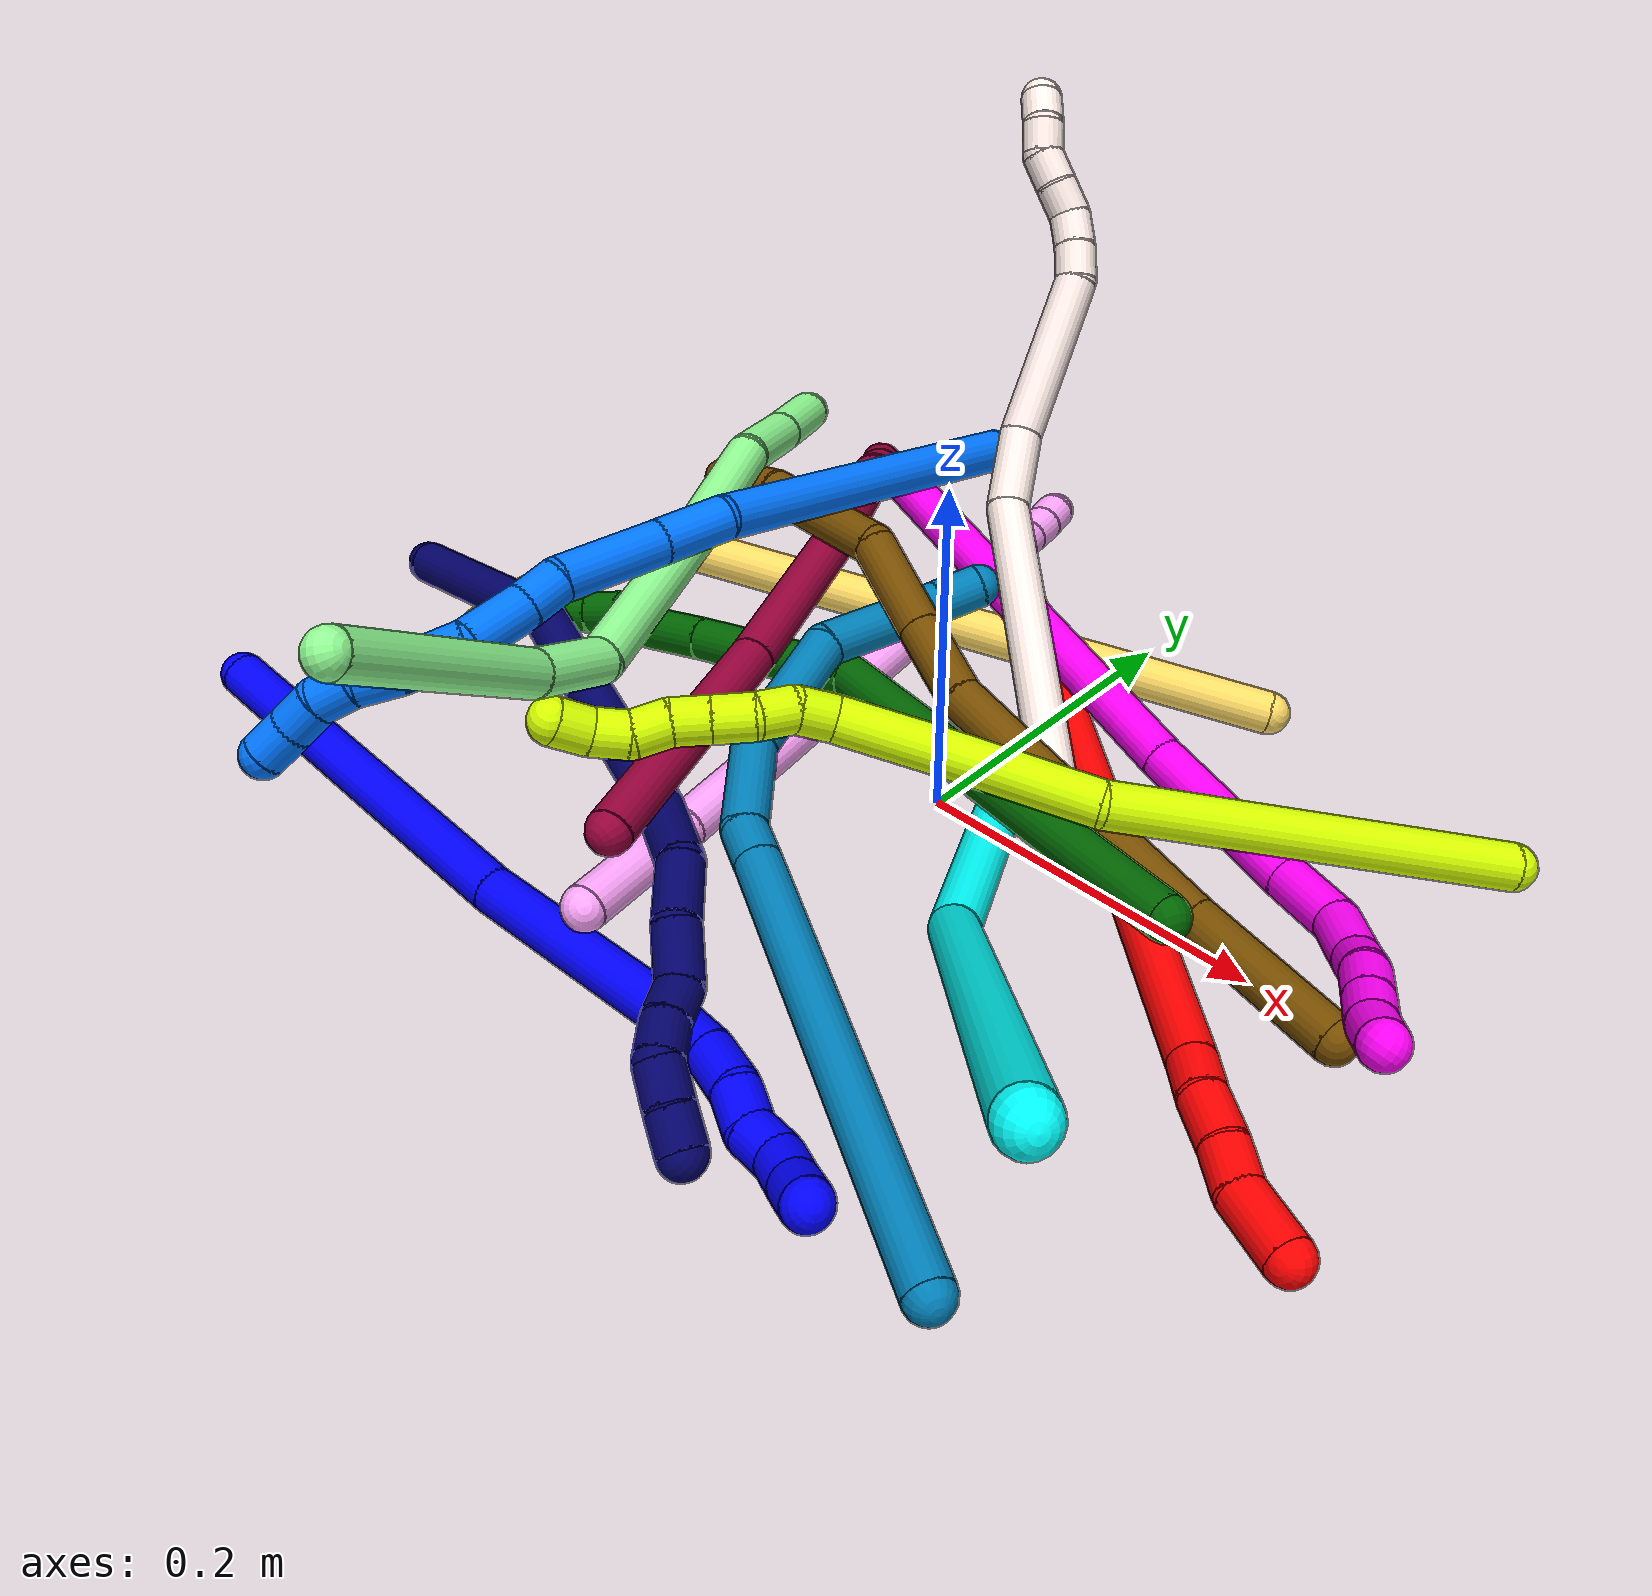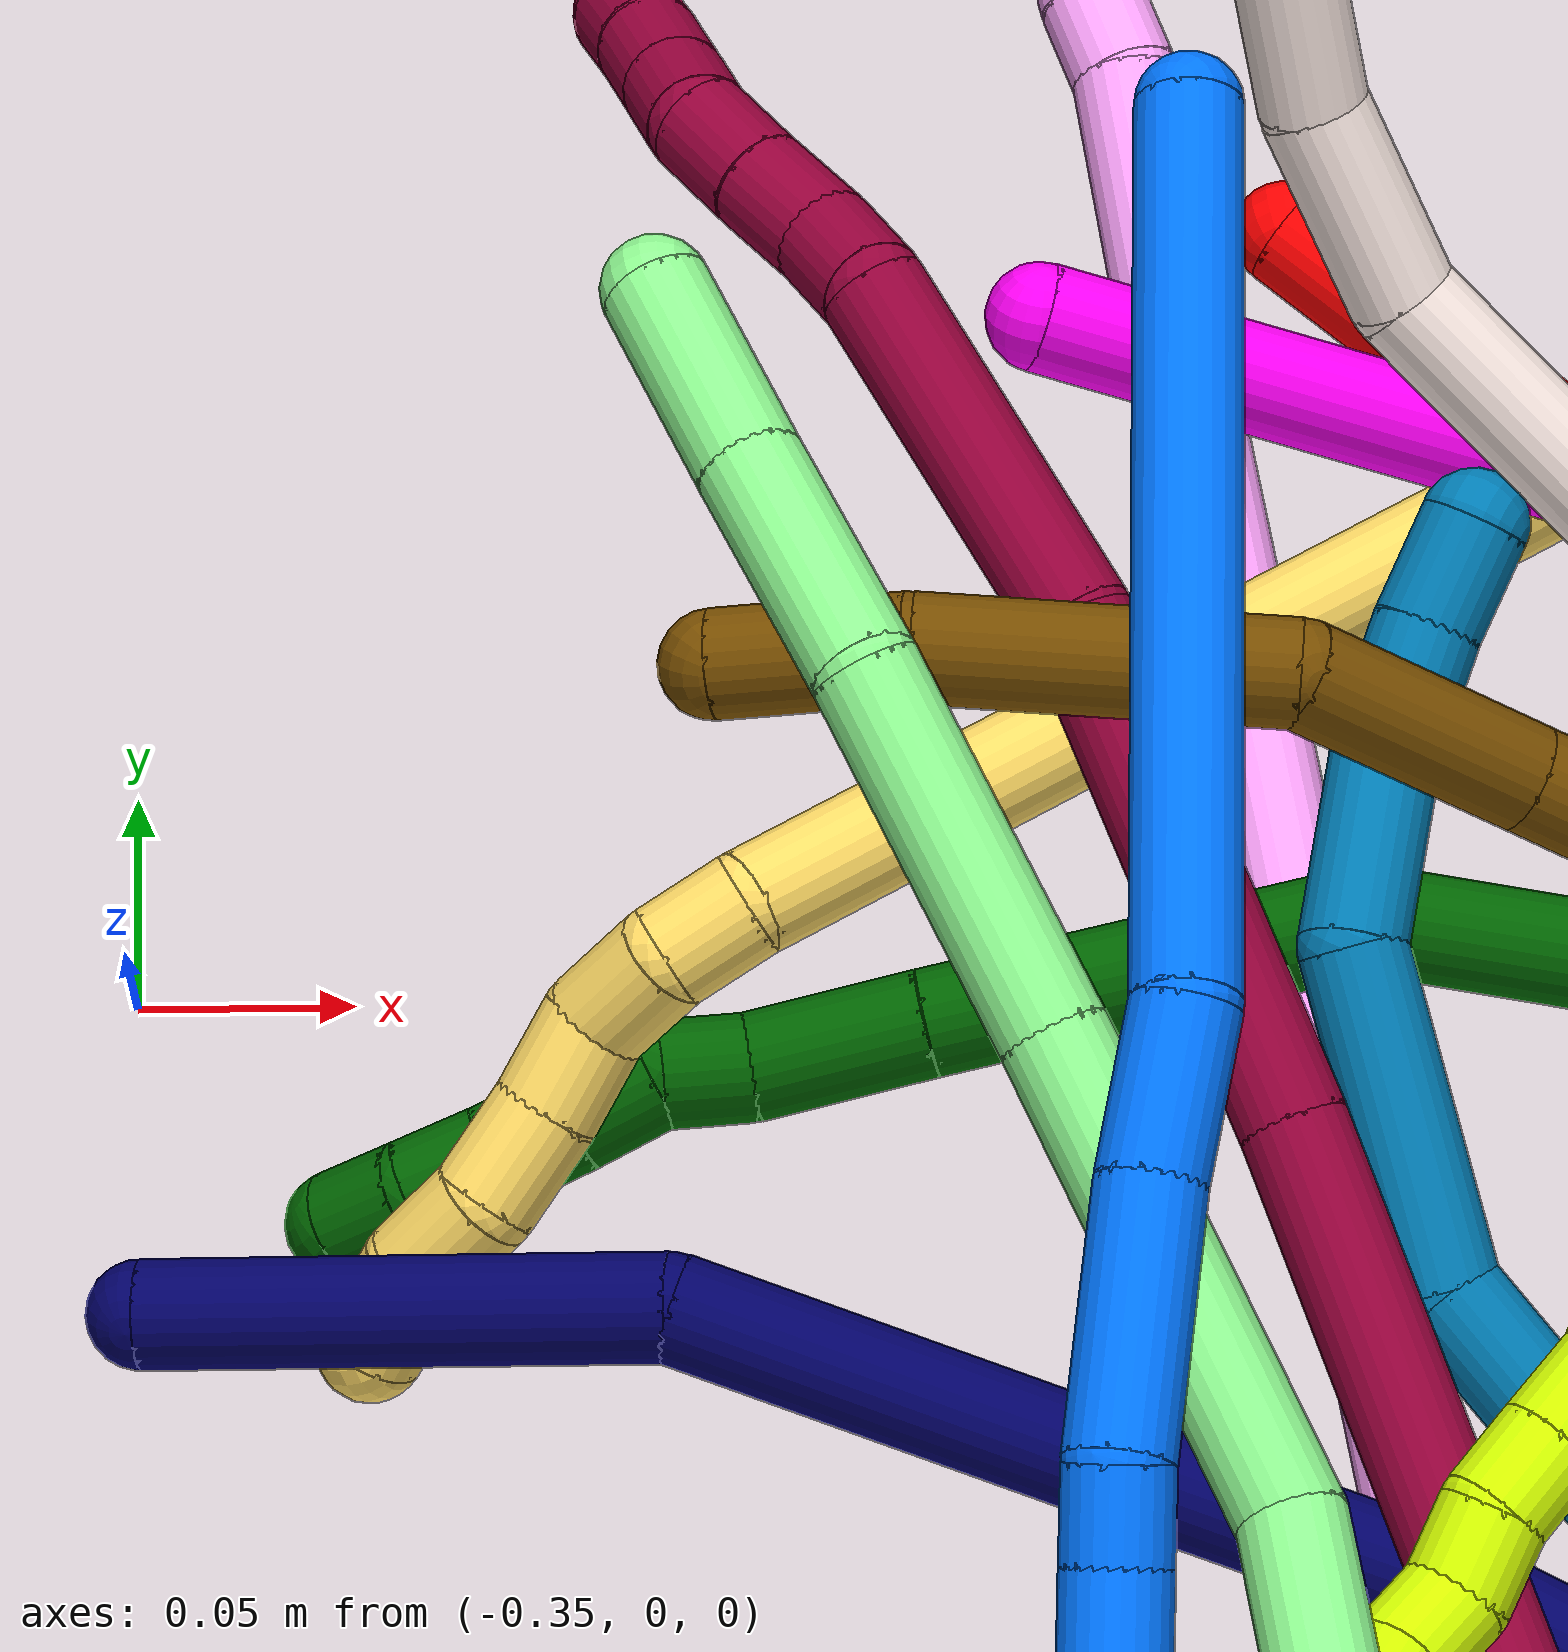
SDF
<sdf version="1.7">
 <world name="default">
  <plugin name="TubeGeneratorPlugin" filename="libtube_generator_plugin.so"/>
  <model name="photoneo_s_sensor">
   <static>1</static>
   <pose>0 0 2 1.57079 1.57079 3.14159</pose>
   <link name="link">
    <inertial><mass>0.1</mass></inertial>
    <sensor name="sensor" type="depth">
     <update_rate>30</update_rate>
     <camera>
      <horizontal_fov>1.22</horizontal_fov>
      <image><width>1920</width><height>1200</height><format>B8G8R8</format></image>
      <clip><near>0.1</near><far>4</far></clip>
      <depth_camera><output>points</output></depth_camera>
     </camera>
     <plugin name="camera_plugin" filename="libgazebo_ros_depth_camera.so">
      <baseline>0.2</baseline>
      <alwaysOn>1</alwaysOn>
      <updateRate>0.0</updateRate>
      <cameraName>camera_ir</cameraName>
      <imageTopicName>/camera/color/image_raw</imageTopicName>
      <cameraInfoTopicName>/camera/color/camera_info</cameraInfoTopicName>
      <depthImageTopicName>/camera/depth/image_raw</depthImageTopicName>
      <depthImageCameraInfoTopicName>/camera/depth/camera_info</depthImageCameraInfoTopicName>
      <pointCloudTopicName>/camera/depth/points</pointCloudTopicName>
      <frameName>fr_optical</frameName>
      <pointCloudCutoff>0.1</pointCloudCutoff>
      <pointCloudCutoffMax>2.0</pointCloudCutoffMax>
      <distortionK1>0</distortionK1>
      <distortionK2>0</distortionK2>
      <distortionK3>0</distortionK3>
      <distortionT1>0</distortionT1>
      <distortionT2>0</distortionT2>
      <CxPrime>0</CxPrime>
      <Cx>0</Cx>
      <Cy>0</Cy>
      <focalLength>0</focalLength>
      <hackBaseline>0</hackBaseline>
     </plugin>
    </sensor>
   </link>
  </model>
  <gravity>0 0 -9.8</gravity>
  <magnetic_field>6e-06 2.3e-05 -4.2e-05</magnetic_field>
  <atmosphere type="adiabatic"/>
  <physics name="default_physics" default="0" type="ode">
   <max_step_size>0.003</max_step_size>
   <real_time_factor>1</real_time_factor>
   <real_time_update_rate>1000</real_time_update_rate>
   <max_contacts>10000</max_contacts>
   <ode>
    <solver>
     <type>quick</type>
     <iters>100</iters>
     <sor>1.3</sor>
     <use_dynamic_moi_rescaling>0</use_dynamic_moi_rescaling>
    </solver>
    <constraints>
     <contact_max_correcting_vel>0</contact_max_correcting_vel>
     <contact_surface_layer>0.001</contact_surface_layer>
     <cfm>0</cfm>
     <erp>0.2</erp>
    </constraints>
   </ode>
  </physics>
  <scene><ambient>0.4 0.4 0.4 1</ambient><background>0.7 0.7 0.7 1</background><shadows>0</shadows></scene>
  <audio><device>default</device></audio>
  <spherical_coordinates>
   <surface_model>EARTH_WGS84</surface_model>
   <latitude_deg>0</latitude_deg>
   <longitude_deg>0</longitude_deg>
   <elevation>0</elevation>
   <heading_deg>0</heading_deg>
  </spherical_coordinates>
  <model name="bin">
   <static>1</static>
   <link name="bottom">
    <collision name="collision-bottom">
     <pose>0 0 -0.01 0 -0 0</pose>
     <geometry><box><size>0.8 0.6 0.02</size></box></geometry>
     <surface>
      <friction><ode><mu>100</mu><mu2>100</mu2></ode></friction>
      <contact><collide_bitmask>65535</collide_bitmask></contact>
     </surface>
    </collision>
   </link>
   <link name="west_wall">
    <collision name="collision-west_wall">
     <pose>-0.41 0 0.1 0 -0 0</pose>
     <geometry><box><size>0.02 0.6 0.2</size></box></geometry>
     <surface>
      <friction><ode><mu>100</mu><mu2>100</mu2></ode></friction>
      <contact><collide_bitmask>65535</collide_bitmask></contact>
     </surface>
    </collision>
   </link>
   <link name="east_wall">
    <collision name="collision-east_wall">
     <pose>0.41 0 0.1 0 -0 0</pose>
     <geometry><box><size>0.02 0.6 0.2</size></box></geometry>
     <surface>
      <friction><ode><mu>100</mu><mu2>100</mu2></ode></friction>
      <contact><collide_bitmask>65535</collide_bitmask></contact>
     </surface>
    </collision>
   </link>
   <link name="south_wall">
    <collision name="collision-south_wall">
     <pose>0 -0.31 0.1 0 -0 0</pose>
     <geometry><box><size>0.8 0.02 0.2</size></box></geometry>
     <surface>
      <friction><ode><mu>100</mu><mu2>100</mu2></ode></friction>
      <contact><collide_bitmask>65535</collide_bitmask></contact>
     </surface>
    </collision>
   </link>
   <link name="north_wall">
    <collision name="collision-north_wall">
     <pose>0 0.31 0.1 0 -0 0</pose>
     <geometry><box><size>0.8 0.02 0.2</size></box></geometry>
     <surface>
      <friction><ode><mu>100</mu><mu2>100</mu2></ode></friction>
      <contact><collide_bitmask>65535</collide_bitmask></contact>
     </surface>
    </collision>
   </link>
  </model>
  <model name="1">
   <static>0</static>
   <link name="1">
    <collision name="collision-cylinder-e_1_1_4">
     <pose>0.091996 0.01532 -0.063463 -2.90473 0.95362 -2.68879</pose>
     <geometry><cylinder><radius>0.0125</radius><length>0.225615</length></cylinder></geometry>
     <surface>
      <friction><ode><mu>1.16</mu><mu2>1.16</mu2><slip1>0</slip1><slip2>0</slip2></ode></friction>
      <contact><ode><kp>1e+06</kp><kd>1</kd><max_vel>0</max_vel><min_depth>0.001</min_depth></ode></contact>
     </surface>
    </collision>
    <visual name="visual-cylinder-e_1_1_4">
     <pose>0.091996 0.01532 -0.063463 -2.90473 0.95362 -2.68879</pose>
     <geometry><cylinder><radius>0.0125</radius><length>0.225615</length></cylinder></geometry>
     <material><ambient>0 0 1 1</ambient></material>
    </visual>
    <collision name="collision-cylinder-e_2_4_5">
     <pose>0.230759 0.035034 -0.166847 -3.03196 0.861218 -2.90382</pose>
     <geometry><cylinder><radius>0.0125</radius><length>0.12329</length></cylinder></geometry>
     <surface>
      <friction><ode><mu>1.16</mu><mu2>1.16</mu2><slip1>0</slip1><slip2>0</slip2></ode></friction>
      <contact><ode><kp>1e+06</kp><kd>1</kd><max_vel>0</max_vel><min_depth>0.001</min_depth></ode></contact>
     </surface>
    </collision>
    <visual name="visual-cylinder-e_2_4_5">
     <pose>0.230759 0.035034 -0.166847 -3.03196 0.861218 -2.90382</pose>
     <geometry><cylinder><radius>0.0125</radius><length>0.12329</length></cylinder></geometry>
     <material><ambient>0 0 1 1</ambient></material>
    </visual>
    <collision name="collision-cylinder-e_3_5_6">
     <pose>0.290927 0.042919 -0.221331 -2.90632 0.730037 -2.54172</pose>
     <geometry><cylinder><radius>0.0125</radius><length>0.040193</length></cylinder></geometry>
     <surface>
      <friction><ode><mu>1.16</mu><mu2>1.16</mu2><slip1>0</slip1><slip2>0</slip2></ode></friction>
      <contact><ode><kp>1e+06</kp><kd>1</kd><max_vel>0</max_vel><min_depth>0.001</min_depth></ode></contact>
     </surface>
    </collision>
    <visual name="visual-cylinder-e_3_5_6">
     <pose>0.290927 0.042919 -0.221331 -2.90632 0.730037 -2.54172</pose>
     <geometry><cylinder><radius>0.0125</radius><length>0.040193</length></cylinder></geometry>
     <material><ambient>0 0 1 1</ambient></material>
    </visual>
    <collision name="collision-cylinder-e_4_6_7">
     <pose>0.311897 0.051017 -0.246252 -2.72309 0.588526 -1.91918</pose>
     <geometry><cylinder><radius>0.0125</radius><length>0.027262</length></cylinder></geometry>
     <surface>
      <friction><ode><mu>1.16</mu><mu2>1.16</mu2><slip1>0</slip1><slip2>0</slip2></ode></friction>
      <contact><ode><kp>1e+06</kp><kd>1</kd><max_vel>0</max_vel><min_depth>0.001</min_depth></ode></contact>
     </surface>
    </collision>
    <visual name="visual-cylinder-e_4_6_7">
     <pose>0.311897 0.051017 -0.246252 -2.72309 0.588526 -1.91918</pose>
     <geometry><cylinder><radius>0.0125</radius><length>0.027262</length></cylinder></geometry>
     <material><ambient>0 0 1 1</ambient></material>
    </visual>
    <collision name="collision-cylinder-e_5_7_8">
     <pose>0.326143 0.061915 -0.26324 -2.3824 0.631228 -1.37181</pose>
     <geometry><cylinder><radius>0.0125</radius><length>0.022638</length></cylinder></geometry>
     <surface>
      <friction><ode><mu>1.16</mu><mu2>1.16</mu2><slip1>0</slip1><slip2>0</slip2></ode></friction>
      <contact><ode><kp>1e+06</kp><kd>1</kd><max_vel>0</max_vel><min_depth>0.001</min_depth></ode></contact>
     </surface>
    </collision>
    <visual name="visual-cylinder-e_5_7_8">
     <pose>0.326143 0.061915 -0.26324 -2.3824 0.631228 -1.37181</pose>
     <geometry><cylinder><radius>0.0125</radius><length>0.022638</length></cylinder></geometry>
     <material><ambient>0 0 1 1</ambient></material>
    </visual>
    <collision name="collision-cylinder-e_6_8_9">
     <pose>0.339679 0.070049 -0.277244 -2.89651 0.733797 -2.52133</pose>
     <geometry><cylinder><radius>0.0125</radius><length>0.020475</length></cylinder></geometry>
     <surface>
      <friction><ode><mu>1.16</mu><mu2>1.16</mu2><slip1>0</slip1><slip2>0</slip2></ode></friction>
      <contact><ode><kp>1e+06</kp><kd>1</kd><max_vel>0</max_vel><min_depth>0.001</min_depth></ode></contact>
     </surface>
    </collision>
    <visual name="visual-cylinder-e_6_8_9">
     <pose>0.339679 0.070049 -0.277244 -2.89651 0.733797 -2.52133</pose>
     <geometry><cylinder><radius>0.0125</radius><length>0.020475</length></cylinder></geometry>
     <material><ambient>0 0 1 1</ambient></material>
    </visual>
    <collision name="collision-cylinder-e_7_9_10">
     <pose>0.350253 0.075564 -0.293392 -2.74534 0.372664 -1.50793</pose>
     <geometry><cylinder><radius>0.0125</radius><length>0.020421</length></cylinder></geometry>
     <surface>
      <friction><ode><mu>1.16</mu><mu2>1.16</mu2><slip1>0</slip1><slip2>0</slip2></ode></friction>
      <contact><ode><kp>1e+06</kp><kd>1</kd><max_vel>0</max_vel><min_depth>0.001</min_depth></ode></contact>
     </surface>
    </collision>
    <visual name="visual-cylinder-e_7_9_10">
     <pose>0.350253 0.075564 -0.293392 -2.74534 0.372664 -1.50793</pose>
     <geometry><cylinder><radius>0.0125</radius><length>0.020421</length></cylinder></geometry>
     <material><ambient>0 0 1 1</ambient></material>
    </visual>
    <collision name="collision-cylinder-e_8_10_2">
     <pose>0.356057 0.082053 -0.311587 -2.85098 0.20913 -1.24431</pose>
     <geometry><cylinder><radius>0.0125</radius><length>0.020106</length></cylinder></geometry>
     <surface>
      <friction><ode><mu>1.16</mu><mu2>1.16</mu2><slip1>0</slip1><slip2>0</slip2></ode></friction>
      <contact><ode><kp>1e+06</kp><kd>1</kd><max_vel>0</max_vel><min_depth>0.001</min_depth></ode></contact>
     </surface>
    </collision>
    <visual name="visual-cylinder-e_8_10_2">
     <pose>0.356057 0.082053 -0.311587 -2.85098 0.20913 -1.24431</pose>
     <geometry><cylinder><radius>0.0125</radius><length>0.020106</length></cylinder></geometry>
     <material><ambient>0 0 1 1</ambient></material>
    </visual>
    <collision name="collision-sphere-2">
     <pose>0.358144 0.08487 -0.321009 0 -0 0</pose>
     <geometry><sphere><radius>0.0125</radius></sphere></geometry>
     <surface>
      <friction><ode><mu>1.16</mu><mu2>1.16</mu2><slip1>0</slip1><slip2>0</slip2></ode></friction>
      <contact><ode><kp>1e+06</kp><kd>1</kd><max_vel>0</max_vel><min_depth>0.001</min_depth></ode></contact>
     </surface>
    </collision>
    <visual name="visual-sphere-2">
     <pose>0.358144 0.08487 -0.321009 0 -0 0</pose>
     <geometry><sphere><radius>0.0125</radius></sphere></geometry>
     <material><ambient>0 0 1 1</ambient></material>
    </visual>
    <collision name="collision-sphere-10">
     <pose>0.35397 0.079235 -0.302165 0 -0 0</pose>
     <geometry><sphere><radius>0.0125</radius></sphere></geometry>
     <surface>
      <friction><ode><mu>1.16</mu><mu2>1.16</mu2><slip1>0</slip1><slip2>0</slip2></ode></friction>
      <contact><ode><kp>1e+06</kp><kd>1</kd><max_vel>0</max_vel><min_depth>0.001</min_depth></ode></contact>
     </surface>
    </collision>
    <visual name="visual-sphere-10">
     <pose>0.35397 0.079235 -0.302165 0 -0 0</pose>
     <geometry><sphere><radius>0.0125</radius></sphere></geometry>
     <material><ambient>0 0 1 1</ambient></material>
    </visual>
    <collision name="collision-sphere-9">
     <pose>0.346535 0.071894 -0.284619 0 -0 0</pose>
     <geometry><sphere><radius>0.0125</radius></sphere></geometry>
     <surface>
      <friction><ode><mu>1.16</mu><mu2>1.16</mu2><slip1>0</slip1><slip2>0</slip2></ode></friction>
      <contact><ode><kp>1e+06</kp><kd>1</kd><max_vel>0</max_vel><min_depth>0.001</min_depth></ode></contact>
     </surface>
    </collision>
    <visual name="visual-sphere-9">
     <pose>0.346535 0.071894 -0.284619 0 -0 0</pose>
     <geometry><sphere><radius>0.0125</radius></sphere></geometry>
     <material><ambient>0 0 1 1</ambient></material>
    </visual>
    <collision name="collision-sphere-4">
     <pose>0.183993 0.030639 -0.126926 0 -0 0</pose>
     <geometry><sphere><radius>0.0125</radius></sphere></geometry>
     <surface>
      <friction><ode><mu>1.16</mu><mu2>1.16</mu2><slip1>0</slip1><slip2>0</slip2></ode></friction>
      <contact><ode><kp>1e+06</kp><kd>1</kd><max_vel>0</max_vel><min_depth>0.001</min_depth></ode></contact>
     </surface>
    </collision>
    <visual name="visual-sphere-4">
     <pose>0.183993 0.030639 -0.126926 0 -0 0</pose>
     <geometry><sphere><radius>0.0125</radius></sphere></geometry>
     <material><ambient>0 0 1 1</ambient></material>
    </visual>
    <collision name="collision-sphere-1">
     <geometry><sphere><radius>0.0125</radius></sphere></geometry>
     <surface>
      <friction><ode><mu>1.16</mu><mu2>1.16</mu2><slip1>0</slip1><slip2>0</slip2></ode></friction>
      <contact><ode><kp>1e+06</kp><kd>1</kd><max_vel>0</max_vel><min_depth>0.001</min_depth></ode></contact>
     </surface>
    </collision>
    <visual name="visual-sphere-1">
     <geometry><sphere><radius>0.0125</radius></sphere></geometry>
     <material><ambient>0 0 1 1</ambient></material>
    </visual>
    <collision name="collision-sphere-8">
     <pose>0.332823 0.068205 -0.269868 0 -0 0</pose>
     <geometry><sphere><radius>0.0125</radius></sphere></geometry>
     <surface>
      <friction><ode><mu>1.16</mu><mu2>1.16</mu2><slip1>0</slip1><slip2>0</slip2></ode></friction>
      <contact><ode><kp>1e+06</kp><kd>1</kd><max_vel>0</max_vel><min_depth>0.001</min_depth></ode></contact>
     </surface>
    </collision>
    <visual name="visual-sphere-8">
     <pose>0.332823 0.068205 -0.269868 0 -0 0</pose>
     <geometry><sphere><radius>0.0125</radius></sphere></geometry>
     <material><ambient>0 0 1 1</ambient></material>
    </visual>
    <collision name="collision-sphere-5">
     <pose>0.277525 0.039428 -0.206769 0 -0 0</pose>
     <geometry><sphere><radius>0.0125</radius></sphere></geometry>
     <surface>
      <friction><ode><mu>1.16</mu><mu2>1.16</mu2><slip1>0</slip1><slip2>0</slip2></ode></friction>
      <contact><ode><kp>1e+06</kp><kd>1</kd><max_vel>0</max_vel><min_depth>0.001</min_depth></ode></contact>
     </surface>
    </collision>
    <visual name="visual-sphere-5">
     <pose>0.277525 0.039428 -0.206769 0 -0 0</pose>
     <geometry><sphere><radius>0.0125</radius></sphere></geometry>
     <material><ambient>0 0 1 1</ambient></material>
    </visual>
    <collision name="collision-sphere-6">
     <pose>0.30433 0.04641 -0.235893 0 -0 0</pose>
     <geometry><sphere><radius>0.0125</radius></sphere></geometry>
     <surface>
      <friction><ode><mu>1.16</mu><mu2>1.16</mu2><slip1>0</slip1><slip2>0</slip2></ode></friction>
      <contact><ode><kp>1e+06</kp><kd>1</kd><max_vel>0</max_vel><min_depth>0.001</min_depth></ode></contact>
     </surface>
    </collision>
    <visual name="visual-sphere-6">
     <pose>0.30433 0.04641 -0.235893 0 -0 0</pose>
     <geometry><sphere><radius>0.0125</radius></sphere></geometry>
     <material><ambient>0 0 1 1</ambient></material>
    </visual>
    <collision name="collision-sphere-7">
     <pose>0.319463 0.055625 -0.256611 0 -0 0</pose>
     <geometry><sphere><radius>0.0125</radius></sphere></geometry>
     <surface>
      <friction><ode><mu>1.16</mu><mu2>1.16</mu2><slip1>0</slip1><slip2>0</slip2></ode></friction>
      <contact><ode><kp>1e+06</kp><kd>1</kd><max_vel>0</max_vel><min_depth>0.001</min_depth></ode></contact>
     </surface>
    </collision>
    <visual name="visual-sphere-7">
     <pose>0.319463 0.055625 -0.256611 0 -0 0</pose>
     <geometry><sphere><radius>0.0125</radius></sphere></geometry>
     <material><ambient>0 0 1 1</ambient></material>
    </visual>
    <inertial>
     <pose>0.196103 0.03384 -0.14878 0 -0 0</pose>
     <mass>0.5</mass>
     <inertia>
      <ixx>-0.000861</ixx>
      <ixy>0</ixy>
      <ixz>0</ixz>
      <iyy>0.00082</iyy>
      <iyz>0</iyz>
      <izz>-0.001091</izz>
     </inertia>
    </inertial>
   </link>
   <pose>-0.336019 -0.221211 0.038435 -2.6198 0.606138 0.42008</pose>
  </model>
  <model name="2">
   <static>0</static>
   <link name="2">
    <collision name="collision-cylinder-e_1_1_4">
     <pose>0.109304 -0.102235 0.127267 0.676757 0.59001 0.213063</pose>
     <geometry><cylinder><radius>0.0125</radius><length>0.39292</length></cylinder></geometry>
     <surface>
      <friction><ode><mu>1.16</mu><mu2>1.16</mu2><slip1>0</slip1><slip2>0</slip2></ode></friction>
      <contact><ode><kp>1e+06</kp><kd>1</kd><max_vel>0</max_vel><min_depth>0.001</min_depth></ode></contact>
     </surface>
    </collision>
    <visual name="visual-cylinder-e_1_1_4">
     <pose>0.109304 -0.102235 0.127267 0.676757 0.59001 0.213063</pose>
     <geometry><cylinder><radius>0.0125</radius><length>0.39292</length></cylinder></geometry>
     <material><ambient>1 0 0 1</ambient></material>
    </visual>
    <collision name="collision-cylinder-e_2_4_5">
     <pose>0.224383 -0.209717 0.262384 0.589149 0.548893 0.170432</pose>
     <geometry><cylinder><radius>0.0125</radius><length>0.022134</length></cylinder></geometry>
     <surface>
      <friction><ode><mu>1.16</mu><mu2>1.16</mu2><slip1>0</slip1><slip2>0</slip2></ode></friction>
      <contact><ode><kp>1e+06</kp><kd>1</kd><max_vel>0</max_vel><min_depth>0.001</min_depth></ode></contact>
     </surface>
    </collision>
    <visual name="visual-cylinder-e_2_4_5">
     <pose>0.224383 -0.209717 0.262384 0.589149 0.548893 0.170432</pose>
     <geometry><cylinder><radius>0.0125</radius><length>0.022134</length></cylinder></geometry>
     <material><ambient>1 0 0 1</ambient></material>
    </visual>
    <collision name="collision-cylinder-e_3_5_6">
     <pose>0.23818 -0.222449 0.277899 0.773605 0.642762 0.269569</pose>
     <geometry><cylinder><radius>0.0125</radius><length>0.026772</length></cylinder></geometry>
     <surface>
      <friction><ode><mu>1.16</mu><mu2>1.16</mu2><slip1>0</slip1><slip2>0</slip2></ode></friction>
      <contact><ode><kp>1e+06</kp><kd>1</kd><max_vel>0</max_vel><min_depth>0.001</min_depth></ode></contact>
     </surface>
    </collision>
    <visual name="visual-cylinder-e_3_5_6">
     <pose>0.23818 -0.222449 0.277899 0.773605 0.642762 0.269569</pose>
     <geometry><cylinder><radius>0.0125</radius><length>0.026772</length></cylinder></geometry>
     <material><ambient>1 0 0 1</ambient></material>
    </visual>
    <collision name="collision-cylinder-e_4_6_7">
     <pose>0.252093 -0.237558 0.291455 0.912857 0.548701 0.274647</pose>
     <geometry><cylinder><radius>0.0125</radius><length>0.022581</length></cylinder></geometry>
     <surface>
      <friction><ode><mu>1.16</mu><mu2>1.16</mu2><slip1>0</slip1><slip2>0</slip2></ode></friction>
      <contact><ode><kp>1e+06</kp><kd>1</kd><max_vel>0</max_vel><min_depth>0.001</min_depth></ode></contact>
     </surface>
    </collision>
    <visual name="visual-cylinder-e_4_6_7">
     <pose>0.252093 -0.237558 0.291455 0.912857 0.548701 0.274647</pose>
     <geometry><cylinder><radius>0.0125</radius><length>0.022581</length></cylinder></geometry>
     <material><ambient>1 0 0 1</ambient></material>
    </visual>
    <collision name="collision-cylinder-e_5_7_2">
     <pose>0.271394 -0.254141 0.304865 0.872675 0.85359 0.417919</pose>
     <geometry><cylinder><radius>0.0125</radius><length>0.035593</length></cylinder></geometry>
     <surface>
      <friction><ode><mu>1.16</mu><mu2>1.16</mu2><slip1>0</slip1><slip2>0</slip2></ode></friction>
      <contact><ode><kp>1e+06</kp><kd>1</kd><max_vel>0</max_vel><min_depth>0.001</min_depth></ode></contact>
     </surface>
    </collision>
    <visual name="visual-cylinder-e_5_7_2">
     <pose>0.271394 -0.254141 0.304865 0.872675 0.85359 0.417919</pose>
     <geometry><cylinder><radius>0.0125</radius><length>0.035593</length></cylinder></geometry>
     <material><ambient>1 0 0 1</ambient></material>
    </visual>
    <collision name="collision-sphere-2">
     <pose>0.284806 -0.263102 0.312383 0 -0 0</pose>
     <geometry><sphere><radius>0.0125</radius></sphere></geometry>
     <surface>
      <friction><ode><mu>1.16</mu><mu2>1.16</mu2><slip1>0</slip1><slip2>0</slip2></ode></friction>
      <contact><ode><kp>1e+06</kp><kd>1</kd><max_vel>0</max_vel><min_depth>0.001</min_depth></ode></contact>
     </surface>
    </collision>
    <visual name="visual-sphere-2">
     <pose>0.284806 -0.263102 0.312383 0 -0 0</pose>
     <geometry><sphere><radius>0.0125</radius></sphere></geometry>
     <material><ambient>1 0 0 1</ambient></material>
    </visual>
    <collision name="collision-sphere-7">
     <pose>0.257982 -0.245181 0.297346 0 -0 0</pose>
     <geometry><sphere><radius>0.0125</radius></sphere></geometry>
     <surface>
      <friction><ode><mu>1.16</mu><mu2>1.16</mu2><slip1>0</slip1><slip2>0</slip2></ode></friction>
      <contact><ode><kp>1e+06</kp><kd>1</kd><max_vel>0</max_vel><min_depth>0.001</min_depth></ode></contact>
     </surface>
    </collision>
    <visual name="visual-sphere-7">
     <pose>0.257982 -0.245181 0.297346 0 -0 0</pose>
     <geometry><sphere><radius>0.0125</radius></sphere></geometry>
     <material><ambient>1 0 0 1</ambient></material>
    </visual>
    <collision name="collision-sphere-6">
     <pose>0.246204 -0.229936 0.285564 0 -0 0</pose>
     <geometry><sphere><radius>0.0125</radius></sphere></geometry>
     <surface>
      <friction><ode><mu>1.16</mu><mu2>1.16</mu2><slip1>0</slip1><slip2>0</slip2></ode></friction>
      <contact><ode><kp>1e+06</kp><kd>1</kd><max_vel>0</max_vel><min_depth>0.001</min_depth></ode></contact>
     </surface>
    </collision>
    <visual name="visual-sphere-6">
     <pose>0.246204 -0.229936 0.285564 0 -0 0</pose>
     <geometry><sphere><radius>0.0125</radius></sphere></geometry>
     <material><ambient>1 0 0 1</ambient></material>
    </visual>
    <collision name="collision-sphere-5">
     <pose>0.230157 -0.214963 0.270234 0 -0 0</pose>
     <geometry><sphere><radius>0.0125</radius></sphere></geometry>
     <surface>
      <friction><ode><mu>1.16</mu><mu2>1.16</mu2><slip1>0</slip1><slip2>0</slip2></ode></friction>
      <contact><ode><kp>1e+06</kp><kd>1</kd><max_vel>0</max_vel><min_depth>0.001</min_depth></ode></contact>
     </surface>
    </collision>
    <visual name="visual-sphere-5">
     <pose>0.230157 -0.214963 0.270234 0 -0 0</pose>
     <geometry><sphere><radius>0.0125</radius></sphere></geometry>
     <material><ambient>1 0 0 1</ambient></material>
    </visual>
    <collision name="collision-sphere-1">
     <geometry><sphere><radius>0.0125</radius></sphere></geometry>
     <surface>
      <friction><ode><mu>1.16</mu><mu2>1.16</mu2><slip1>0</slip1><slip2>0</slip2></ode></friction>
      <contact><ode><kp>1e+06</kp><kd>1</kd><max_vel>0</max_vel><min_depth>0.001</min_depth></ode></contact>
     </surface>
    </collision>
    <visual name="visual-sphere-1">
     <geometry><sphere><radius>0.0125</radius></sphere></geometry>
     <material><ambient>1 0 0 1</ambient></material>
    </visual>
    <collision name="collision-sphere-4">
     <pose>0.218608 -0.204471 0.254535 0 -0 0</pose>
     <geometry><sphere><radius>0.0125</radius></sphere></geometry>
     <surface>
      <friction><ode><mu>1.16</mu><mu2>1.16</mu2><slip1>0</slip1><slip2>0</slip2></ode></friction>
      <contact><ode><kp>1e+06</kp><kd>1</kd><max_vel>0</max_vel><min_depth>0.001</min_depth></ode></contact>
     </surface>
    </collision>
    <visual name="visual-sphere-4">
     <pose>0.218608 -0.204471 0.254535 0 -0 0</pose>
     <geometry><sphere><radius>0.0125</radius></sphere></geometry>
     <material><ambient>1 0 0 1</ambient></material>
    </visual>
    <inertial>
     <pose>0.139286 -0.130355 0.161372 0 -0 0</pose>
     <mass>0.5</mass>
     <inertia>
      <ixx>0.005042</ixx>
      <ixy>0</ixy>
      <ixz>0</ixz>
      <iyy>0.005119</iyy>
      <iyz>0</iyz>
      <izz>-0.000159</izz>
     </inertia>
    </inertial>
   </link>
   <pose>-0.082241 0.179906 0.011491 1.09153 -0.304214 0.246898</pose>
  </model>
  <model name="3">
   <static>0</static>
   <link name="3">
    <collision name="collision-cylinder-e_1_1_4">
     <pose>-0.002472 0.033689 -0.147242 -2.91666 -0.016366 0.144658</pose>
     <geometry><cylinder><radius>0.0125</radius><length>0.302135</length></cylinder></geometry>
     <surface>
      <friction><ode><mu>1.16</mu><mu2>1.16</mu2><slip1>0</slip1><slip2>0</slip2></ode></friction>
      <contact><ode><kp>1e+06</kp><kd>1</kd><max_vel>0</max_vel><min_depth>0.001</min_depth></ode></contact>
     </surface>
    </collision>
    <visual name="visual-cylinder-e_1_1_4">
     <pose>-0.002472 0.033689 -0.147242 -2.91666 -0.016366 0.144658</pose>
     <geometry><cylinder><radius>0.0125</radius><length>0.302135</length></cylinder></geometry>
     <material><ambient>0.003922 1 0.996078 1</ambient></material>
    </visual>
    <collision name="collision-cylinder-e_2_4_5">
     <pose>-0.0301 0.084288 -0.342342 -2.80196 -0.460121 1.87766</pose>
     <geometry><cylinder><radius>0.0125</radius><length>0.113297</length></cylinder></geometry>
     <surface>
      <friction><ode><mu>1.16</mu><mu2>1.16</mu2><slip1>0</slip1><slip2>0</slip2></ode></friction>
      <contact><ode><kp>1e+06</kp><kd>1</kd><max_vel>0</max_vel><min_depth>0.001</min_depth></ode></contact>
     </surface>
    </collision>
    <visual name="visual-cylinder-e_2_4_5">
     <pose>-0.0301 0.084288 -0.342342 -2.80196 -0.460121 1.87766</pose>
     <geometry><cylinder><radius>0.0125</radius><length>0.113297</length></cylinder></geometry>
     <material><ambient>0.003922 1 0.996078 1</ambient></material>
    </visual>
    <collision name="collision-cylinder-e_3_5_6">
     <pose>-0.061038 0.103978 -0.398027 -2.80028 -0.608153 2.13718</pose>
     <geometry><cylinder><radius>0.0125</radius><length>0.020243</length></cylinder></geometry>
     <surface>
      <friction><ode><mu>1.16</mu><mu2>1.16</mu2><slip1>0</slip1><slip2>0</slip2></ode></friction>
      <contact><ode><kp>1e+06</kp><kd>1</kd><max_vel>0</max_vel><min_depth>0.001</min_depth></ode></contact>
     </surface>
    </collision>
    <visual name="visual-cylinder-e_3_5_6">
     <pose>-0.061038 0.103978 -0.398027 -2.80028 -0.608153 2.13718</pose>
     <geometry><cylinder><radius>0.0125</radius><length>0.020243</length></cylinder></geometry>
     <material><ambient>0.003922 1 0.996078 1</ambient></material>
    </visual>
    <collision name="collision-cylinder-e_4_6_7">
     <pose>-0.071733 0.108203 -0.414715 -2.97997 -0.500651 2.52809</pose>
     <geometry><cylinder><radius>0.0125</radius><length>0.020466</length></cylinder></geometry>
     <surface>
      <friction><ode><mu>1.16</mu><mu2>1.16</mu2><slip1>0</slip1><slip2>0</slip2></ode></friction>
      <contact><ode><kp>1e+06</kp><kd>1</kd><max_vel>0</max_vel><min_depth>0.001</min_depth></ode></contact>
     </surface>
    </collision>
    <visual name="visual-cylinder-e_4_6_7">
     <pose>-0.071733 0.108203 -0.414715 -2.97997 -0.500651 2.52809</pose>
     <geometry><cylinder><radius>0.0125</radius><length>0.020466</length></cylinder></geometry>
     <material><ambient>0.003922 1 0.996078 1</ambient></material>
    </visual>
    <collision name="collision-cylinder-e_5_7_8">
     <pose>-0.078556 0.114528 -0.433543 -2.6863 -0.170548 0.706982</pose>
     <geometry><cylinder><radius>0.0125</radius><length>0.022523</length></cylinder></geometry>
     <surface>
      <friction><ode><mu>1.16</mu><mu2>1.16</mu2><slip1>0</slip1><slip2>0</slip2></ode></friction>
      <contact><ode><kp>1e+06</kp><kd>1</kd><max_vel>0</max_vel><min_depth>0.001</min_depth></ode></contact>
     </surface>
    </collision>
    <visual name="visual-cylinder-e_5_7_8">
     <pose>-0.078556 0.114528 -0.433543 -2.6863 -0.170548 0.706982</pose>
     <geometry><cylinder><radius>0.0125</radius><length>0.022523</length></cylinder></geometry>
     <material><ambient>0.003922 1 0.996078 1</ambient></material>
    </visual>
    <collision name="collision-cylinder-e_6_8_2">
     <pose>-0.085907 0.126007 -0.449888 -2.3391 -0.535087 1.14725</pose>
     <geometry><cylinder><radius>0.0125</radius><length>0.021335</length></cylinder></geometry>
     <surface>
      <friction><ode><mu>1.16</mu><mu2>1.16</mu2><slip1>0</slip1><slip2>0</slip2></ode></friction>
      <contact><ode><kp>1e+06</kp><kd>1</kd><max_vel>0</max_vel><min_depth>0.001</min_depth></ode></contact>
     </surface>
    </collision>
    <visual name="visual-cylinder-e_6_8_2">
     <pose>-0.085907 0.126007 -0.449888 -2.3391 -0.535087 1.14725</pose>
     <geometry><cylinder><radius>0.0125</radius><length>0.021335</length></cylinder></geometry>
     <material><ambient>0.003922 1 0.996078 1</ambient></material>
    </visual>
    <collision name="collision-sphere-2">
     <pose>-0.091346 0.132606 -0.456265 0 -0 0</pose>
     <geometry><sphere><radius>0.0125</radius></sphere></geometry>
     <surface>
      <friction><ode><mu>1.16</mu><mu2>1.16</mu2><slip1>0</slip1><slip2>0</slip2></ode></friction>
      <contact><ode><kp>1e+06</kp><kd>1</kd><max_vel>0</max_vel><min_depth>0.001</min_depth></ode></contact>
     </surface>
    </collision>
    <visual name="visual-sphere-2">
     <pose>-0.091346 0.132606 -0.456265 0 -0 0</pose>
     <geometry><sphere><radius>0.0125</radius></sphere></geometry>
     <material><ambient>0.003922 1 0.996078 1</ambient></material>
    </visual>
    <collision name="collision-sphere-4">
     <pose>-0.004945 0.067378 -0.294485 0 -0 0</pose>
     <geometry><sphere><radius>0.0125</radius></sphere></geometry>
     <surface>
      <friction><ode><mu>1.16</mu><mu2>1.16</mu2><slip1>0</slip1><slip2>0</slip2></ode></friction>
      <contact><ode><kp>1e+06</kp><kd>1</kd><max_vel>0</max_vel><min_depth>0.001</min_depth></ode></contact>
     </surface>
    </collision>
    <visual name="visual-sphere-4">
     <pose>-0.004945 0.067378 -0.294485 0 -0 0</pose>
     <geometry><sphere><radius>0.0125</radius></sphere></geometry>
     <material><ambient>0.003922 1 0.996078 1</ambient></material>
    </visual>
    <collision name="collision-sphere-1">
     <geometry><sphere><radius>0.0125</radius></sphere></geometry>
     <surface>
      <friction><ode><mu>1.16</mu><mu2>1.16</mu2><slip1>0</slip1><slip2>0</slip2></ode></friction>
      <contact><ode><kp>1e+06</kp><kd>1</kd><max_vel>0</max_vel><min_depth>0.001</min_depth></ode></contact>
     </surface>
    </collision>
    <visual name="visual-sphere-1">
     <geometry><sphere><radius>0.0125</radius></sphere></geometry>
     <material><ambient>0.003922 1 0.996078 1</ambient></material>
    </visual>
    <collision name="collision-sphere-8">
     <pose>-0.080467 0.119408 -0.443511 0 -0 0</pose>
     <geometry><sphere><radius>0.0125</radius></sphere></geometry>
     <surface>
      <friction><ode><mu>1.16</mu><mu2>1.16</mu2><slip1>0</slip1><slip2>0</slip2></ode></friction>
      <contact><ode><kp>1e+06</kp><kd>1</kd><max_vel>0</max_vel><min_depth>0.001</min_depth></ode></contact>
     </surface>
    </collision>
    <visual name="visual-sphere-8">
     <pose>-0.080467 0.119408 -0.443511 0 -0 0</pose>
     <geometry><sphere><radius>0.0125</radius></sphere></geometry>
     <material><ambient>0.003922 1 0.996078 1</ambient></material>
    </visual>
    <collision name="collision-sphere-5">
     <pose>-0.055255 0.101197 -0.3902 0 -0 0</pose>
     <geometry><sphere><radius>0.0125</radius></sphere></geometry>
     <surface>
      <friction><ode><mu>1.16</mu><mu2>1.16</mu2><slip1>0</slip1><slip2>0</slip2></ode></friction>
      <contact><ode><kp>1e+06</kp><kd>1</kd><max_vel>0</max_vel><min_depth>0.001</min_depth></ode></contact>
     </surface>
    </collision>
    <visual name="visual-sphere-5">
     <pose>-0.055255 0.101197 -0.3902 0 -0 0</pose>
     <geometry><sphere><radius>0.0125</radius></sphere></geometry>
     <material><ambient>0.003922 1 0.996078 1</ambient></material>
    </visual>
    <collision name="collision-sphere-6">
     <pose>-0.066821 0.106758 -0.405855 0 -0 0</pose>
     <geometry><sphere><radius>0.0125</radius></sphere></geometry>
     <surface>
      <friction><ode><mu>1.16</mu><mu2>1.16</mu2><slip1>0</slip1><slip2>0</slip2></ode></friction>
      <contact><ode><kp>1e+06</kp><kd>1</kd><max_vel>0</max_vel><min_depth>0.001</min_depth></ode></contact>
     </surface>
    </collision>
    <visual name="visual-sphere-6">
     <pose>-0.066821 0.106758 -0.405855 0 -0 0</pose>
     <geometry><sphere><radius>0.0125</radius></sphere></geometry>
     <material><ambient>0.003922 1 0.996078 1</ambient></material>
    </visual>
    <collision name="collision-sphere-7">
     <pose>-0.076644 0.109647 -0.423575 0 -0 0</pose>
     <geometry><sphere><radius>0.0125</radius></sphere></geometry>
     <surface>
      <friction><ode><mu>1.16</mu><mu2>1.16</mu2><slip1>0</slip1><slip2>0</slip2></ode></friction>
      <contact><ode><kp>1e+06</kp><kd>1</kd><max_vel>0</max_vel><min_depth>0.001</min_depth></ode></contact>
     </surface>
    </collision>
    <visual name="visual-sphere-7">
     <pose>-0.076644 0.109647 -0.423575 0 -0 0</pose>
     <geometry><sphere><radius>0.0125</radius></sphere></geometry>
     <material><ambient>0.003922 1 0.996078 1</ambient></material>
    </visual>
    <inertial>
     <pose>-0.020926 0.058631 -0.238363 0 -0 0</pose>
     <mass>0.5</mass>
     <inertia>
      <ixx>0.002689</ixx>
      <ixy>0</ixy>
      <ixz>0</ixz>
      <iyy>-0.001718</iyy>
      <iyz>0</iyz>
      <izz>-0.000494</izz>
     </inertia>
    </inertial>
   </link>
   <pose>0.28109 -0.294336 0.21033 -0.784713 0.86983 -1.48014</pose>
  </model>
  <model name="4">
   <static>0</static>
   <link name="4">
    <collision name="collision-cylinder-e_1_1_4">
     <pose>0.005773 0.031715 0.024887 -0.905455 0.14223 -0.069273</pose>
     <geometry><cylinder><radius>0.0125</radius><length>0.081451</length></cylinder></geometry>
     <surface>
      <friction><ode><mu>1.16</mu><mu2>1.16</mu2><slip1>0</slip1><slip2>0</slip2></ode></friction>
      <contact><ode><kp>1e+06</kp><kd>1</kd><max_vel>0</max_vel><min_depth>0.001</min_depth></ode></contact>
     </surface>
    </collision>
    <visual name="visual-cylinder-e_1_1_4">
     <pose>0.005773 0.031715 0.024887 -0.905455 0.14223 -0.069273</pose>
     <geometry><cylinder><radius>0.0125</radius><length>0.081451</length></cylinder></geometry>
     <material><ambient>1 0.65098 0.996078 1</ambient></material>
    </visual>
    <collision name="collision-cylinder-e_2_4_5">
     <pose>0.035799 0.179946 0.131443 -0.959448 0.16883 -0.087988</pose>
     <geometry><cylinder><radius>0.0125</radius><length>0.288679</length></cylinder></geometry>
     <surface>
      <friction><ode><mu>1.16</mu><mu2>1.16</mu2><slip1>0</slip1><slip2>0</slip2></ode></friction>
      <contact><ode><kp>1e+06</kp><kd>1</kd><max_vel>0</max_vel><min_depth>0.001</min_depth></ode></contact>
     </surface>
    </collision>
    <visual name="visual-cylinder-e_2_4_5">
     <pose>0.035799 0.179946 0.131443 -0.959448 0.16883 -0.087988</pose>
     <geometry><cylinder><radius>0.0125</radius><length>0.288679</length></cylinder></geometry>
     <material><ambient>1 0.65098 0.996078 1</ambient></material>
    </visual>
    <collision name="collision-cylinder-e_3_5_6">
     <pose>0.0646 0.322256 0.231074 -0.962507 0.143701 -0.075135</pose>
     <geometry><cylinder><radius>0.0125</radius><length>0.063519</length></cylinder></geometry>
     <surface>
      <friction><ode><mu>1.16</mu><mu2>1.16</mu2><slip1>0</slip1><slip2>0</slip2></ode></friction>
      <contact><ode><kp>1e+06</kp><kd>1</kd><max_vel>0</max_vel><min_depth>0.001</min_depth></ode></contact>
     </surface>
    </collision>
    <visual name="visual-cylinder-e_3_5_6">
     <pose>0.0646 0.322256 0.231074 -0.962507 0.143701 -0.075135</pose>
     <geometry><cylinder><radius>0.0125</radius><length>0.063519</length></cylinder></geometry>
     <material><ambient>1 0.65098 0.996078 1</ambient></material>
    </visual>
    <collision name="collision-cylinder-e_4_6_7">
     <pose>0.071042 0.355019 0.256663 -0.740366 0.181236 -0.070497</pose>
     <geometry><cylinder><radius>0.0125</radius><length>0.021007</length></cylinder></geometry>
     <surface>
      <friction><ode><mu>1.16</mu><mu2>1.16</mu2><slip1>0</slip1><slip2>0</slip2></ode></friction>
      <contact><ode><kp>1e+06</kp><kd>1</kd><max_vel>0</max_vel><min_depth>0.001</min_depth></ode></contact>
     </surface>
    </collision>
    <visual name="visual-cylinder-e_4_6_7">
     <pose>0.071042 0.355019 0.256663 -0.740366 0.181236 -0.070497</pose>
     <geometry><cylinder><radius>0.0125</radius><length>0.021007</length></cylinder></geometry>
     <material><ambient>1 0.65098 0.996078 1</ambient></material>
    </visual>
    <collision name="collision-cylinder-e_5_7_8">
     <pose>0.074898 0.371176 0.272056 -0.869046 0.161754 -0.0752</pose>
     <geometry><cylinder><radius>0.0125</radius><length>0.024379</length></cylinder></geometry>
     <surface>
      <friction><ode><mu>1.16</mu><mu2>1.16</mu2><slip1>0</slip1><slip2>0</slip2></ode></friction>
      <contact><ode><kp>1e+06</kp><kd>1</kd><max_vel>0</max_vel><min_depth>0.001</min_depth></ode></contact>
     </surface>
    </collision>
    <visual name="visual-cylinder-e_5_7_8">
     <pose>0.074898 0.371176 0.272056 -0.869046 0.161754 -0.0752</pose>
     <geometry><cylinder><radius>0.0125</radius><length>0.024379</length></cylinder></geometry>
     <material><ambient>1 0.65098 0.996078 1</ambient></material>
    </visual>
    <collision name="collision-cylinder-e_6_8_2">
     <pose>0.079125 0.38821 0.286395 -0.873581 0.217708 -0.101955</pose>
     <geometry><cylinder><radius>0.0125</radius><length>0.020966</length></cylinder></geometry>
     <surface>
      <friction><ode><mu>1.16</mu><mu2>1.16</mu2><slip1>0</slip1><slip2>0</slip2></ode></friction>
      <contact><ode><kp>1e+06</kp><kd>1</kd><max_vel>0</max_vel><min_depth>0.001</min_depth></ode></contact>
     </surface>
    </collision>
    <visual name="visual-cylinder-e_6_8_2">
     <pose>0.079125 0.38821 0.286395 -0.873581 0.217708 -0.101955</pose>
     <geometry><cylinder><radius>0.0125</radius><length>0.020966</length></cylinder></geometry>
     <material><ambient>1 0.65098 0.996078 1</ambient></material>
    </visual>
    <collision name="collision-sphere-2">
     <pose>0.08139 0.396057 0.292967 0 -0 0</pose>
     <geometry><sphere><radius>0.0125</radius></sphere></geometry>
     <surface>
      <friction><ode><mu>1.16</mu><mu2>1.16</mu2><slip1>0</slip1><slip2>0</slip2></ode></friction>
      <contact><ode><kp>1e+06</kp><kd>1</kd><max_vel>0</max_vel><min_depth>0.001</min_depth></ode></contact>
     </surface>
    </collision>
    <visual name="visual-sphere-2">
     <pose>0.08139 0.396057 0.292967 0 -0 0</pose>
     <geometry><sphere><radius>0.0125</radius></sphere></geometry>
     <material><ambient>1 0.65098 0.996078 1</ambient></material>
    </visual>
    <collision name="collision-sphere-4">
     <pose>0.011546 0.063431 0.049774 0 -0 0</pose>
     <geometry><sphere><radius>0.0125</radius></sphere></geometry>
     <surface>
      <friction><ode><mu>1.16</mu><mu2>1.16</mu2><slip1>0</slip1><slip2>0</slip2></ode></friction>
      <contact><ode><kp>1e+06</kp><kd>1</kd><max_vel>0</max_vel><min_depth>0.001</min_depth></ode></contact>
     </surface>
    </collision>
    <visual name="visual-sphere-4">
     <pose>0.011546 0.063431 0.049774 0 -0 0</pose>
     <geometry><sphere><radius>0.0125</radius></sphere></geometry>
     <material><ambient>1 0.65098 0.996078 1</ambient></material>
    </visual>
    <collision name="collision-sphere-1">
     <geometry><sphere><radius>0.0125</radius></sphere></geometry>
     <surface>
      <friction><ode><mu>1.16</mu><mu2>1.16</mu2><slip1>0</slip1><slip2>0</slip2></ode></friction>
      <contact><ode><kp>1e+06</kp><kd>1</kd><max_vel>0</max_vel><min_depth>0.001</min_depth></ode></contact>
     </surface>
    </collision>
    <visual name="visual-sphere-1">
     <geometry><sphere><radius>0.0125</radius></sphere></geometry>
     <material><ambient>1 0.65098 0.996078 1</ambient></material>
    </visual>
    <collision name="collision-sphere-8">
     <pose>0.076861 0.380363 0.279823 0 -0 0</pose>
     <geometry><sphere><radius>0.0125</radius></sphere></geometry>
     <surface>
      <friction><ode><mu>1.16</mu><mu2>1.16</mu2><slip1>0</slip1><slip2>0</slip2></ode></friction>
      <contact><ode><kp>1e+06</kp><kd>1</kd><max_vel>0</max_vel><min_depth>0.001</min_depth></ode></contact>
     </surface>
    </collision>
    <visual name="visual-sphere-8">
     <pose>0.076861 0.380363 0.279823 0 -0 0</pose>
     <geometry><sphere><radius>0.0125</radius></sphere></geometry>
     <material><ambient>1 0.65098 0.996078 1</ambient></material>
    </visual>
    <collision name="collision-sphere-5">
     <pose>0.060052 0.296462 0.213112 0 -0 0</pose>
     <geometry><sphere><radius>0.0125</radius></sphere></geometry>
     <surface>
      <friction><ode><mu>1.16</mu><mu2>1.16</mu2><slip1>0</slip1><slip2>0</slip2></ode></friction>
      <contact><ode><kp>1e+06</kp><kd>1</kd><max_vel>0</max_vel><min_depth>0.001</min_depth></ode></contact>
     </surface>
    </collision>
    <visual name="visual-sphere-5">
     <pose>0.060052 0.296462 0.213112 0 -0 0</pose>
     <geometry><sphere><radius>0.0125</radius></sphere></geometry>
     <material><ambient>1 0.65098 0.996078 1</ambient></material>
    </visual>
    <collision name="collision-sphere-6">
     <pose>0.069149 0.34805 0.249036 0 -0 0</pose>
     <geometry><sphere><radius>0.0125</radius></sphere></geometry>
     <surface>
      <friction><ode><mu>1.16</mu><mu2>1.16</mu2><slip1>0</slip1><slip2>0</slip2></ode></friction>
      <contact><ode><kp>1e+06</kp><kd>1</kd><max_vel>0</max_vel><min_depth>0.001</min_depth></ode></contact>
     </surface>
    </collision>
    <visual name="visual-sphere-6">
     <pose>0.069149 0.34805 0.249036 0 -0 0</pose>
     <geometry><sphere><radius>0.0125</radius></sphere></geometry>
     <material><ambient>1 0.65098 0.996078 1</ambient></material>
    </visual>
    <collision name="collision-sphere-7">
     <pose>0.072935 0.361988 0.26429 0 -0 0</pose>
     <geometry><sphere><radius>0.0125</radius></sphere></geometry>
     <surface>
      <friction><ode><mu>1.16</mu><mu2>1.16</mu2><slip1>0</slip1><slip2>0</slip2></ode></friction>
      <contact><ode><kp>1e+06</kp><kd>1</kd><max_vel>0</max_vel><min_depth>0.001</min_depth></ode></contact>
     </surface>
    </collision>
    <visual name="visual-sphere-7">
     <pose>0.072935 0.361988 0.26429 0 -0 0</pose>
     <geometry><sphere><radius>0.0125</radius></sphere></geometry>
     <material><ambient>1 0.65098 0.996078 1</ambient></material>
    </visual>
    <inertial>
     <pose>0.03977 0.19929 0.145356 0 -0 0</pose>
     <mass>0.5</mass>
     <inertia>
      <ixx>0.001882</ixx>
      <ixy>0</ixy>
      <ixz>0</ixz>
      <iyy>0.001075</iyy>
      <iyz>0</iyz>
      <izz>-0.002015</izz>
     </inertia>
    </inertial>
   </link>
   <pose>-0.047669 -0.210492 0.034307 2.72586 -0.755792 3.05003</pose>
  </model>
  <model name="5">
   <static>0</static>
   <link name="5">
    <collision name="collision-cylinder-e_1_1_4">
     <pose>-0.151243 -0.011301 -0.0975 3.0262 -0.995142 -2.92971</pose>
     <geometry><cylinder><radius>0.0125</radius><length>0.360602</length></cylinder></geometry>
     <surface>
      <friction><ode><mu>1.16</mu><mu2>1.16</mu2><slip1>0</slip1><slip2>0</slip2></ode></friction>
      <contact><ode><kp>1e+06</kp><kd>1</kd><max_vel>0</max_vel><min_depth>0.001</min_depth></ode></contact>
     </surface>
    </collision>
    <visual name="visual-cylinder-e_1_1_4">
     <pose>-0.151243 -0.011301 -0.0975 3.0262 -0.995142 -2.92971</pose>
     <geometry><cylinder><radius>0.0125</radius><length>0.360602</length></cylinder></geometry>
     <material><ambient>1 0.858824 0.4 1</ambient></material>
    </visual>
    <collision name="collision-cylinder-e_2_4_5">
     <pose>-0.309245 -0.025326 -0.203125 2.818 -0.667838 -2.26205</pose>
     <geometry><cylinder><radius>0.0125</radius><length>0.021827</length></cylinder></geometry>
     <surface>
      <friction><ode><mu>1.16</mu><mu2>1.16</mu2><slip1>0</slip1><slip2>0</slip2></ode></friction>
      <contact><ode><kp>1e+06</kp><kd>1</kd><max_vel>0</max_vel><min_depth>0.001</min_depth></ode></contact>
     </surface>
    </collision>
    <visual name="visual-cylinder-e_2_4_5">
     <pose>-0.309245 -0.025326 -0.203125 2.818 -0.667838 -2.26205</pose>
     <geometry><cylinder><radius>0.0125</radius><length>0.021827</length></cylinder></geometry>
     <material><ambient>1 0.858824 0.4 1</ambient></material>
    </visual>
    <collision name="collision-cylinder-e_3_5_6">
     <pose>-0.318658 -0.033762 -0.221487 2.63272 -0.22271 -0.812101</pose>
     <geometry><cylinder><radius>0.0125</radius><length>0.024041</length></cylinder></geometry>
     <surface>
      <friction><ode><mu>1.16</mu><mu2>1.16</mu2><slip1>0</slip1><slip2>0</slip2></ode></friction>
      <contact><ode><kp>1e+06</kp><kd>1</kd><max_vel>0</max_vel><min_depth>0.001</min_depth></ode></contact>
     </surface>
    </collision>
    <visual name="visual-cylinder-e_3_5_6">
     <pose>-0.318658 -0.033762 -0.221487 2.63272 -0.22271 -0.812101</pose>
     <geometry><cylinder><radius>0.0125</radius><length>0.024041</length></cylinder></geometry>
     <material><ambient>1 0.858824 0.4 1</ambient></material>
    </visual>
    <collision name="collision-cylinder-e_4_6_7">
     <pose>-0.327417 -0.047158 -0.237602 2.22374 -0.562867 -1.05878</pose>
     <geometry><cylinder><radius>0.0125</radius><length>0.022878</length></cylinder></geometry>
     <surface>
      <friction><ode><mu>1.16</mu><mu2>1.16</mu2><slip1>0</slip1><slip2>0</slip2></ode></friction>
      <contact><ode><kp>1e+06</kp><kd>1</kd><max_vel>0</max_vel><min_depth>0.001</min_depth></ode></contact>
     </surface>
    </collision>
    <visual name="visual-cylinder-e_4_6_7">
     <pose>-0.327417 -0.047158 -0.237602 2.22374 -0.562867 -1.05878</pose>
     <geometry><cylinder><radius>0.0125</radius><length>0.022878</length></cylinder></geometry>
     <material><ambient>1 0.858824 0.4 1</ambient></material>
    </visual>
    <collision name="collision-cylinder-e_5_7_8">
     <pose>-0.340691 -0.062167 -0.250282 2.31921 -0.622208 -1.27079</pose>
     <geometry><cylinder><radius>0.0125</radius><length>0.024603</length></cylinder></geometry>
     <surface>
      <friction><ode><mu>1.16</mu><mu2>1.16</mu2><slip1>0</slip1><slip2>0</slip2></ode></friction>
      <contact><ode><kp>1e+06</kp><kd>1</kd><max_vel>0</max_vel><min_depth>0.001</min_depth></ode></contact>
     </surface>
    </collision>
    <visual name="visual-cylinder-e_5_7_8">
     <pose>-0.340691 -0.062167 -0.250282 2.31921 -0.622208 -1.27079</pose>
     <geometry><cylinder><radius>0.0125</radius><length>0.024603</length></cylinder></geometry>
     <material><ambient>1 0.858824 0.4 1</ambient></material>
    </visual>
    <collision name="collision-cylinder-e_6_8_9">
     <pose>-0.351577 -0.075278 -0.266523 2.59169 -0.323825 -1.04971</pose>
     <geometry><cylinder><radius>0.0125</radius><length>0.023357</length></cylinder></geometry>
     <surface>
      <friction><ode><mu>1.16</mu><mu2>1.16</mu2><slip1>0</slip1><slip2>0</slip2></ode></friction>
      <contact><ode><kp>1e+06</kp><kd>1</kd><max_vel>0</max_vel><min_depth>0.001</min_depth></ode></contact>
     </surface>
    </collision>
    <visual name="visual-cylinder-e_6_8_9">
     <pose>-0.351577 -0.075278 -0.266523 2.59169 -0.323825 -1.04971</pose>
     <geometry><cylinder><radius>0.0125</radius><length>0.023357</length></cylinder></geometry>
     <material><ambient>1 0.858824 0.4 1</ambient></material>
    </visual>
    <collision name="collision-cylinder-e_7_9_2">
     <pose>-0.358095 -0.088988 -0.283585 2.33677 -0.249558 -0.573154</pose>
     <geometry><cylinder><radius>0.0125</radius><length>0.022692</length></cylinder></geometry>
     <surface>
      <friction><ode><mu>1.16</mu><mu2>1.16</mu2><slip1>0</slip1><slip2>0</slip2></ode></friction>
      <contact><ode><kp>1e+06</kp><kd>1</kd><max_vel>0</max_vel><min_depth>0.001</min_depth></ode></contact>
     </surface>
    </collision>
    <visual name="visual-cylinder-e_7_9_2">
     <pose>-0.358095 -0.088988 -0.283585 2.33677 -0.249558 -0.573154</pose>
     <geometry><cylinder><radius>0.0125</radius><length>0.022692</length></cylinder></geometry>
     <material><ambient>1 0.858824 0.4 1</ambient></material>
    </visual>
    <collision name="collision-sphere-2">
     <pose>-0.360897 -0.096912 -0.291206 0 -0 0</pose>
     <geometry><sphere><radius>0.0125</radius></sphere></geometry>
     <surface>
      <friction><ode><mu>1.16</mu><mu2>1.16</mu2><slip1>0</slip1><slip2>0</slip2></ode></friction>
      <contact><ode><kp>1e+06</kp><kd>1</kd><max_vel>0</max_vel><min_depth>0.001</min_depth></ode></contact>
     </surface>
    </collision>
    <visual name="visual-sphere-2">
     <pose>-0.360897 -0.096912 -0.291206 0 -0 0</pose>
     <geometry><sphere><radius>0.0125</radius></sphere></geometry>
     <material><ambient>1 0.858824 0.4 1</ambient></material>
    </visual>
    <collision name="collision-sphere-9">
     <pose>-0.355293 -0.081064 -0.275963 0 -0 0</pose>
     <geometry><sphere><radius>0.0125</radius></sphere></geometry>
     <surface>
      <friction><ode><mu>1.16</mu><mu2>1.16</mu2><slip1>0</slip1><slip2>0</slip2></ode></friction>
      <contact><ode><kp>1e+06</kp><kd>1</kd><max_vel>0</max_vel><min_depth>0.001</min_depth></ode></contact>
     </surface>
    </collision>
    <visual name="visual-sphere-9">
     <pose>-0.355293 -0.081064 -0.275963 0 -0 0</pose>
     <geometry><sphere><radius>0.0125</radius></sphere></geometry>
     <material><ambient>1 0.858824 0.4 1</ambient></material>
    </visual>
    <collision name="collision-sphere-4">
     <pose>-0.302486 -0.022601 -0.195001 0 -0 0</pose>
     <geometry><sphere><radius>0.0125</radius></sphere></geometry>
     <surface>
      <friction><ode><mu>1.16</mu><mu2>1.16</mu2><slip1>0</slip1><slip2>0</slip2></ode></friction>
      <contact><ode><kp>1e+06</kp><kd>1</kd><max_vel>0</max_vel><min_depth>0.001</min_depth></ode></contact>
     </surface>
    </collision>
    <visual name="visual-sphere-4">
     <pose>-0.302486 -0.022601 -0.195001 0 -0 0</pose>
     <geometry><sphere><radius>0.0125</radius></sphere></geometry>
     <material><ambient>1 0.858824 0.4 1</ambient></material>
    </visual>
    <collision name="collision-sphere-1">
     <geometry><sphere><radius>0.0125</radius></sphere></geometry>
     <surface>
      <friction><ode><mu>1.16</mu><mu2>1.16</mu2><slip1>0</slip1><slip2>0</slip2></ode></friction>
      <contact><ode><kp>1e+06</kp><kd>1</kd><max_vel>0</max_vel><min_depth>0.001</min_depth></ode></contact>
     </surface>
    </collision>
    <visual name="visual-sphere-1">
     <geometry><sphere><radius>0.0125</radius></sphere></geometry>
     <material><ambient>1 0.858824 0.4 1</ambient></material>
    </visual>
    <collision name="collision-sphere-8">
     <pose>-0.34786 -0.069492 -0.257084 0 -0 0</pose>
     <geometry><sphere><radius>0.0125</radius></sphere></geometry>
     <surface>
      <friction><ode><mu>1.16</mu><mu2>1.16</mu2><slip1>0</slip1><slip2>0</slip2></ode></friction>
      <contact><ode><kp>1e+06</kp><kd>1</kd><max_vel>0</max_vel><min_depth>0.001</min_depth></ode></contact>
     </surface>
    </collision>
    <visual name="visual-sphere-8">
     <pose>-0.34786 -0.069492 -0.257084 0 -0 0</pose>
     <geometry><sphere><radius>0.0125</radius></sphere></geometry>
     <material><ambient>1 0.858824 0.4 1</ambient></material>
    </visual>
    <collision name="collision-sphere-5">
     <pose>-0.316003 -0.028051 -0.211249 0 -0 0</pose>
     <geometry><sphere><radius>0.0125</radius></sphere></geometry>
     <surface>
      <friction><ode><mu>1.16</mu><mu2>1.16</mu2><slip1>0</slip1><slip2>0</slip2></ode></friction>
      <contact><ode><kp>1e+06</kp><kd>1</kd><max_vel>0</max_vel><min_depth>0.001</min_depth></ode></contact>
     </surface>
    </collision>
    <visual name="visual-sphere-5">
     <pose>-0.316003 -0.028051 -0.211249 0 -0 0</pose>
     <geometry><sphere><radius>0.0125</radius></sphere></geometry>
     <material><ambient>1 0.858824 0.4 1</ambient></material>
    </visual>
    <collision name="collision-sphere-6">
     <pose>-0.321313 -0.039474 -0.231725 0 -0 0</pose>
     <geometry><sphere><radius>0.0125</radius></sphere></geometry>
     <surface>
      <friction><ode><mu>1.16</mu><mu2>1.16</mu2><slip1>0</slip1><slip2>0</slip2></ode></friction>
      <contact><ode><kp>1e+06</kp><kd>1</kd><max_vel>0</max_vel><min_depth>0.001</min_depth></ode></contact>
     </surface>
    </collision>
    <visual name="visual-sphere-6">
     <pose>-0.321313 -0.039474 -0.231725 0 -0 0</pose>
     <geometry><sphere><radius>0.0125</radius></sphere></geometry>
     <material><ambient>1 0.858824 0.4 1</ambient></material>
    </visual>
    <collision name="collision-sphere-7">
     <pose>-0.333521 -0.054842 -0.24348 0 -0 0</pose>
     <geometry><sphere><radius>0.0125</radius></sphere></geometry>
     <surface>
      <friction><ode><mu>1.16</mu><mu2>1.16</mu2><slip1>0</slip1><slip2>0</slip2></ode></friction>
      <contact><ode><kp>1e+06</kp><kd>1</kd><max_vel>0</max_vel><min_depth>0.001</min_depth></ode></contact>
     </surface>
    </collision>
    <visual name="visual-sphere-7">
     <pose>-0.333521 -0.054842 -0.24348 0 -0 0</pose>
     <geometry><sphere><radius>0.0125</radius></sphere></geometry>
     <material><ambient>1 0.858824 0.4 1</ambient></material>
    </visual>
    <inertial>
     <pose>-0.202319 -0.023651 -0.138342 0 -0 0</pose>
     <mass>0.5</mass>
     <inertia>
      <ixx>-0.002568</ixx>
      <ixy>0</ixy>
      <ixz>0</ixz>
      <iyy>0.003423</iyy>
      <iyz>0</iyz>
      <izz>0.003524</izz>
     </inertia>
    </inertial>
   </link>
   <pose>0.096724 0.17907 0.014795 0.717834 0.679595 0.843999</pose>
  </model>
  <model name="6">
   <static>0</static>
   <link name="6">
    <collision name="collision-cylinder-e_1_1_4">
     <pose>-0.063825 -0.021526 0.1074 0.197812 -0.527591 -0.053589</pose>
     <geometry><cylinder><radius>0.0125</radius><length>0.253548</length></cylinder></geometry>
     <surface>
      <friction><ode><mu>1.16</mu><mu2>1.16</mu2><slip1>0</slip1><slip2>0</slip2></ode></friction>
      <contact><ode><kp>1e+06</kp><kd>1</kd><max_vel>0</max_vel><min_depth>0.001</min_depth></ode></contact>
     </surface>
    </collision>
    <visual name="visual-cylinder-e_1_1_4">
     <pose>-0.063825 -0.021526 0.1074 0.197812 -0.527591 -0.053589</pose>
     <geometry><cylinder><radius>0.0125</radius><length>0.253548</length></cylinder></geometry>
     <material><ambient>0 0.392157 0.003922 1</ambient></material>
    </visual>
    <collision name="collision-cylinder-e_2_4_5">
     <pose>-0.155758 -0.06929 0.248363 0.663483 -0.583242 -0.206074</pose>
     <geometry><cylinder><radius>0.0125</radius><length>0.102078</length></cylinder></geometry>
     <surface>
      <friction><ode><mu>1.16</mu><mu2>1.16</mu2><slip1>0</slip1><slip2>0</slip2></ode></friction>
      <contact><ode><kp>1e+06</kp><kd>1</kd><max_vel>0</max_vel><min_depth>0.001</min_depth></ode></contact>
     </surface>
    </collision>
    <visual name="visual-cylinder-e_2_4_5">
     <pose>-0.155758 -0.06929 0.248363 0.663483 -0.583242 -0.206074</pose>
     <geometry><cylinder><radius>0.0125</radius><length>0.102078</length></cylinder></geometry>
     <material><ambient>0 0.392157 0.003922 1</ambient></material>
    </visual>
    <collision name="collision-cylinder-e_3_5_6">
     <pose>-0.195695 -0.106097 0.295074 0.677164 -0.611453 -0.221379</pose>
     <geometry><cylinder><radius>0.0125</radius><length>0.041207</length></cylinder></geometry>
     <surface>
      <friction><ode><mu>1.16</mu><mu2>1.16</mu2><slip1>0</slip1><slip2>0</slip2></ode></friction>
      <contact><ode><kp>1e+06</kp><kd>1</kd><max_vel>0</max_vel><min_depth>0.001</min_depth></ode></contact>
     </surface>
    </collision>
    <visual name="visual-cylinder-e_3_5_6">
     <pose>-0.195695 -0.106097 0.295074 0.677164 -0.611453 -0.221379</pose>
     <geometry><cylinder><radius>0.0125</radius><length>0.041207</length></cylinder></geometry>
     <material><ambient>0 0.392157 0.003922 1</ambient></material>
    </visual>
    <collision name="collision-cylinder-e_4_6_7">
     <pose>-0.211446 -0.121605 0.316814 0.521537 -0.377018 -0.101726</pose>
     <geometry><cylinder><radius>0.0125</radius><length>0.021314</length></cylinder></geometry>
     <surface>
      <friction><ode><mu>1.16</mu><mu2>1.16</mu2><slip1>0</slip1><slip2>0</slip2></ode></friction>
      <contact><ode><kp>1e+06</kp><kd>1</kd><max_vel>0</max_vel><min_depth>0.001</min_depth></ode></contact>
     </surface>
    </collision>
    <visual name="visual-cylinder-e_4_6_7">
     <pose>-0.211446 -0.121605 0.316814 0.521537 -0.377018 -0.101726</pose>
     <geometry><cylinder><radius>0.0125</radius><length>0.021314</length></cylinder></geometry>
     <material><ambient>0 0.392157 0.003922 1</ambient></material>
    </visual>
    <collision name="collision-cylinder-e_5_7_8">
     <pose>-0.221599 -0.133616 0.330237 0.971547 -0.62871 -0.340011</pose>
     <geometry><cylinder><radius>0.0125</radius><length>0.021185</length></cylinder></geometry>
     <surface>
      <friction><ode><mu>1.16</mu><mu2>1.16</mu2><slip1>0</slip1><slip2>0</slip2></ode></friction>
      <contact><ode><kp>1e+06</kp><kd>1</kd><max_vel>0</max_vel><min_depth>0.001</min_depth></ode></contact>
     </surface>
    </collision>
    <visual name="visual-cylinder-e_5_7_8">
     <pose>-0.221599 -0.133616 0.330237 0.971547 -0.62871 -0.340011</pose>
     <geometry><cylinder><radius>0.0125</radius><length>0.021185</length></cylinder></geometry>
     <material><ambient>0 0.392157 0.003922 1</ambient></material>
    </visual>
    <collision name="collision-cylinder-e_6_8_9">
     <pose>-0.233588 -0.147519 0.340153 0.930857 -0.594745 -0.305428</pose>
     <geometry><cylinder><radius>0.0125</radius><length>0.020558</length></cylinder></geometry>
     <surface>
      <friction><ode><mu>1.16</mu><mu2>1.16</mu2><slip1>0</slip1><slip2>0</slip2></ode></friction>
      <contact><ode><kp>1e+06</kp><kd>1</kd><max_vel>0</max_vel><min_depth>0.001</min_depth></ode></contact>
     </surface>
    </collision>
    <visual name="visual-cylinder-e_6_8_9">
     <pose>-0.233588 -0.147519 0.340153 0.930857 -0.594745 -0.305428</pose>
     <geometry><cylinder><radius>0.0125</radius><length>0.020558</length></cylinder></geometry>
     <material><ambient>0 0.392157 0.003922 1</ambient></material>
    </visual>
    <collision name="collision-cylinder-e_7_9_10">
     <pose>-0.245439 -0.16047 0.350322 0.877662 -0.65335 -0.315406</pose>
     <geometry><cylinder><radius>0.0125</radius><length>0.020042</length></cylinder></geometry>
     <surface>
      <friction><ode><mu>1.16</mu><mu2>1.16</mu2><slip1>0</slip1><slip2>0</slip2></ode></friction>
      <contact><ode><kp>1e+06</kp><kd>1</kd><max_vel>0</max_vel><min_depth>0.001</min_depth></ode></contact>
     </surface>
    </collision>
    <visual name="visual-cylinder-e_7_9_10">
     <pose>-0.245439 -0.16047 0.350322 0.877662 -0.65335 -0.315406</pose>
     <geometry><cylinder><radius>0.0125</radius><length>0.020042</length></cylinder></geometry>
     <material><ambient>0 0.392157 0.003922 1</ambient></material>
    </visual>
    <collision name="collision-cylinder-e_8_10_2">
     <pose>-0.259836 -0.170953 0.358963 0.886723 -0.975301 -0.493478</pose>
     <geometry><cylinder><radius>0.0125</radius><length>0.020067</length></cylinder></geometry>
     <surface>
      <friction><ode><mu>1.16</mu><mu2>1.16</mu2><slip1>0</slip1><slip2>0</slip2></ode></friction>
      <contact><ode><kp>1e+06</kp><kd>1</kd><max_vel>0</max_vel><min_depth>0.001</min_depth></ode></contact>
     </surface>
    </collision>
    <visual name="visual-cylinder-e_8_10_2">
     <pose>-0.259836 -0.170953 0.358963 0.886723 -0.975301 -0.493478</pose>
     <geometry><cylinder><radius>0.0125</radius><length>0.020067</length></cylinder></geometry>
     <material><ambient>0 0.392157 0.003922 1</ambient></material>
    </visual>
    <collision name="collision-sphere-2">
     <pose>-0.268143 -0.175314 0.362519 0 -0 0</pose>
     <geometry><sphere><radius>0.0125</radius></sphere></geometry>
     <surface>
      <friction><ode><mu>1.16</mu><mu2>1.16</mu2><slip1>0</slip1><slip2>0</slip2></ode></friction>
      <contact><ode><kp>1e+06</kp><kd>1</kd><max_vel>0</max_vel><min_depth>0.001</min_depth></ode></contact>
     </surface>
    </collision>
    <visual name="visual-sphere-2">
     <pose>-0.268143 -0.175314 0.362519 0 -0 0</pose>
     <geometry><sphere><radius>0.0125</radius></sphere></geometry>
     <material><ambient>0 0.392157 0.003922 1</ambient></material>
    </visual>
    <collision name="collision-sphere-10">
     <pose>-0.25153 -0.166591 0.355406 0 -0 0</pose>
     <geometry><sphere><radius>0.0125</radius></sphere></geometry>
     <surface>
      <friction><ode><mu>1.16</mu><mu2>1.16</mu2><slip1>0</slip1><slip2>0</slip2></ode></friction>
      <contact><ode><kp>1e+06</kp><kd>1</kd><max_vel>0</max_vel><min_depth>0.001</min_depth></ode></contact>
     </surface>
    </collision>
    <visual name="visual-sphere-10">
     <pose>-0.25153 -0.166591 0.355406 0 -0 0</pose>
     <geometry><sphere><radius>0.0125</radius></sphere></geometry>
     <material><ambient>0 0.392157 0.003922 1</ambient></material>
    </visual>
    <collision name="collision-sphere-9">
     <pose>-0.239347 -0.154349 0.345238 0 -0 0</pose>
     <geometry><sphere><radius>0.0125</radius></sphere></geometry>
     <surface>
      <friction><ode><mu>1.16</mu><mu2>1.16</mu2><slip1>0</slip1><slip2>0</slip2></ode></friction>
      <contact><ode><kp>1e+06</kp><kd>1</kd><max_vel>0</max_vel><min_depth>0.001</min_depth></ode></contact>
     </surface>
    </collision>
    <visual name="visual-sphere-9">
     <pose>-0.239347 -0.154349 0.345238 0 -0 0</pose>
     <geometry><sphere><radius>0.0125</radius></sphere></geometry>
     <material><ambient>0 0.392157 0.003922 1</ambient></material>
    </visual>
    <collision name="collision-sphere-4">
     <pose>-0.127649 -0.043053 0.214799 0 -0 0</pose>
     <geometry><sphere><radius>0.0125</radius></sphere></geometry>
     <surface>
      <friction><ode><mu>1.16</mu><mu2>1.16</mu2><slip1>0</slip1><slip2>0</slip2></ode></friction>
      <contact><ode><kp>1e+06</kp><kd>1</kd><max_vel>0</max_vel><min_depth>0.001</min_depth></ode></contact>
     </surface>
    </collision>
    <visual name="visual-sphere-4">
     <pose>-0.127649 -0.043053 0.214799 0 -0 0</pose>
     <geometry><sphere><radius>0.0125</radius></sphere></geometry>
     <material><ambient>0 0.392157 0.003922 1</ambient></material>
    </visual>
    <collision name="collision-sphere-1">
     <geometry><sphere><radius>0.0125</radius></sphere></geometry>
     <surface>
      <friction><ode><mu>1.16</mu><mu2>1.16</mu2><slip1>0</slip1><slip2>0</slip2></ode></friction>
      <contact><ode><kp>1e+06</kp><kd>1</kd><max_vel>0</max_vel><min_depth>0.001</min_depth></ode></contact>
     </surface>
    </collision>
    <visual name="visual-sphere-1">
     <geometry><sphere><radius>0.0125</radius></sphere></geometry>
     <material><ambient>0 0.392157 0.003922 1</ambient></material>
    </visual>
    <collision name="collision-sphere-8">
     <pose>-0.227829 -0.14069 0.335069 0 -0 0</pose>
     <geometry><sphere><radius>0.0125</radius></sphere></geometry>
     <surface>
      <friction><ode><mu>1.16</mu><mu2>1.16</mu2><slip1>0</slip1><slip2>0</slip2></ode></friction>
      <contact><ode><kp>1e+06</kp><kd>1</kd><max_vel>0</max_vel><min_depth>0.001</min_depth></ode></contact>
     </surface>
    </collision>
    <visual name="visual-sphere-8">
     <pose>-0.227829 -0.14069 0.335069 0 -0 0</pose>
     <geometry><sphere><radius>0.0125</radius></sphere></geometry>
     <material><ambient>0 0.392157 0.003922 1</ambient></material>
    </visual>
    <collision name="collision-sphere-5">
     <pose>-0.183867 -0.095526 0.281926 0 -0 0</pose>
     <geometry><sphere><radius>0.0125</radius></sphere></geometry>
     <surface>
      <friction><ode><mu>1.16</mu><mu2>1.16</mu2><slip1>0</slip1><slip2>0</slip2></ode></friction>
      <contact><ode><kp>1e+06</kp><kd>1</kd><max_vel>0</max_vel><min_depth>0.001</min_depth></ode></contact>
     </surface>
    </collision>
    <visual name="visual-sphere-5">
     <pose>-0.183867 -0.095526 0.281926 0 -0 0</pose>
     <geometry><sphere><radius>0.0125</radius></sphere></geometry>
     <material><ambient>0 0.392157 0.003922 1</ambient></material>
    </visual>
    <collision name="collision-sphere-6">
     <pose>-0.207523 -0.116668 0.308223 0 -0 0</pose>
     <geometry><sphere><radius>0.0125</radius></sphere></geometry>
     <surface>
      <friction><ode><mu>1.16</mu><mu2>1.16</mu2><slip1>0</slip1><slip2>0</slip2></ode></friction>
      <contact><ode><kp>1e+06</kp><kd>1</kd><max_vel>0</max_vel><min_depth>0.001</min_depth></ode></contact>
     </surface>
    </collision>
    <visual name="visual-sphere-6">
     <pose>-0.207523 -0.116668 0.308223 0 -0 0</pose>
     <geometry><sphere><radius>0.0125</radius></sphere></geometry>
     <material><ambient>0 0.392157 0.003922 1</ambient></material>
    </visual>
    <collision name="collision-sphere-7">
     <pose>-0.21537 -0.126541 0.325405 0 -0 0</pose>
     <geometry><sphere><radius>0.0125</radius></sphere></geometry>
     <surface>
      <friction><ode><mu>1.16</mu><mu2>1.16</mu2><slip1>0</slip1><slip2>0</slip2></ode></friction>
      <contact><ode><kp>1e+06</kp><kd>1</kd><max_vel>0</max_vel><min_depth>0.001</min_depth></ode></contact>
     </surface>
    </collision>
    <visual name="visual-sphere-7">
     <pose>-0.21537 -0.126541 0.325405 0 -0 0</pose>
     <geometry><sphere><radius>0.0125</radius></sphere></geometry>
     <material><ambient>0 0.392157 0.003922 1</ambient></material>
    </visual>
    <inertial>
     <pose>-0.128566 -0.06401 0.199417 0 -0 0</pose>
     <mass>0.5</mass>
     <inertia>
      <ixx>0.001165</ixx>
      <ixy>0</ixy>
      <ixz>0</ixz>
      <iyy>0.001341</iyy>
      <iyz>0</iyz>
      <izz>0.001065</izz>
     </inertia>
    </inertial>
   </link>
   <pose>0.17743 -0.046808 0.060529 -0.309227 -1.08105 -0.103306</pose>
  </model>
  <model name="7">
   <static>0</static>
   <link name="7">
    <collision name="collision-cylinder-e_1_1_4">
     <pose>0.057534 -0.013989 -0.005983 1.97494 1.31228 1.72436</pose>
     <geometry><cylinder><radius>0.0125</radius><length>0.119024</length></cylinder></geometry>
     <surface>
      <friction><ode><mu>1.16</mu><mu2>1.16</mu2><slip1>0</slip1><slip2>0</slip2></ode></friction>
      <contact><ode><kp>1e+06</kp><kd>1</kd><max_vel>0</max_vel><min_depth>0.001</min_depth></ode></contact>
     </surface>
    </collision>
    <visual name="visual-cylinder-e_1_1_4">
     <pose>0.057534 -0.013989 -0.005983 1.97494 1.31228 1.72436</pose>
     <geometry><cylinder><radius>0.0125</radius><length>0.119024</length></cylinder></geometry>
     <material><ambient>0.003922 0 0.403922 1</ambient></material>
    </visual>
    <collision name="collision-cylinder-e_2_4_5">
     <pose>0.188951 -0.079775 -0.017713 1.68131 0.95646 1.04977</pose>
     <geometry><cylinder><radius>0.0125</radius><length>0.180829</length></cylinder></geometry>
     <surface>
      <friction><ode><mu>1.16</mu><mu2>1.16</mu2><slip1>0</slip1><slip2>0</slip2></ode></friction>
      <contact><ode><kp>1e+06</kp><kd>1</kd><max_vel>0</max_vel><min_depth>0.001</min_depth></ode></contact>
     </surface>
    </collision>
    <visual name="visual-cylinder-e_2_4_5">
     <pose>0.188951 -0.079775 -0.017713 1.68131 0.95646 1.04977</pose>
     <geometry><cylinder><radius>0.0125</radius><length>0.180829</length></cylinder></geometry>
     <material><ambient>0.003922 0 0.403922 1</ambient></material>
    </visual>
    <collision name="collision-cylinder-e_3_5_6">
     <pose>0.282017 -0.146573 -0.020149 1.35347 0.895615 0.736511</pose>
     <geometry><cylinder><radius>0.0125</radius><length>0.049151</length></cylinder></geometry>
     <surface>
      <friction><ode><mu>1.16</mu><mu2>1.16</mu2><slip1>0</slip1><slip2>0</slip2></ode></friction>
      <contact><ode><kp>1e+06</kp><kd>1</kd><max_vel>0</max_vel><min_depth>0.001</min_depth></ode></contact>
     </surface>
    </collision>
    <visual name="visual-cylinder-e_3_5_6">
     <pose>0.282017 -0.146573 -0.020149 1.35347 0.895615 0.736511</pose>
     <geometry><cylinder><radius>0.0125</radius><length>0.049151</length></cylinder></geometry>
     <material><ambient>0.003922 0 0.403922 1</ambient></material>
    </visual>
    <collision name="collision-cylinder-e_4_6_7">
     <pose>0.309695 -0.177235 -0.015613 1.49276 0.495644 0.459747</pose>
     <geometry><cylinder><radius>0.0125</radius><length>0.03572</length></cylinder></geometry>
     <surface>
      <friction><ode><mu>1.16</mu><mu2>1.16</mu2><slip1>0</slip1><slip2>0</slip2></ode></friction>
      <contact><ode><kp>1e+06</kp><kd>1</kd><max_vel>0</max_vel><min_depth>0.001</min_depth></ode></contact>
     </surface>
    </collision>
    <visual name="visual-cylinder-e_4_6_7">
     <pose>0.309695 -0.177235 -0.015613 1.49276 0.495644 0.459747</pose>
     <geometry><cylinder><radius>0.0125</radius><length>0.03572</length></cylinder></geometry>
     <material><ambient>0.003922 0 0.403922 1</ambient></material>
    </visual>
    <collision name="collision-cylinder-e_5_7_8">
     <pose>0.324754 -0.206689 -0.017163 1.76939 0.436635 0.529191</pose>
     <geometry><cylinder><radius>0.0125</radius><length>0.031049</length></cylinder></geometry>
     <surface>
      <friction><ode><mu>1.16</mu><mu2>1.16</mu2><slip1>0</slip1><slip2>0</slip2></ode></friction>
      <contact><ode><kp>1e+06</kp><kd>1</kd><max_vel>0</max_vel><min_depth>0.001</min_depth></ode></contact>
     </surface>
    </collision>
    <visual name="visual-cylinder-e_5_7_8">
     <pose>0.324754 -0.206689 -0.017163 1.76939 0.436635 0.529191</pose>
     <geometry><cylinder><radius>0.0125</radius><length>0.031049</length></cylinder></geometry>
     <material><ambient>0.003922 0 0.403922 1</ambient></material>
    </visual>
    <collision name="collision-cylinder-e_6_8_9">
     <pose>0.334744 -0.229594 -0.01653 1.21289 0.338498 0.235962</pose>
     <geometry><cylinder><radius>0.0125</radius><length>0.02063</length></cylinder></geometry>
     <surface>
      <friction><ode><mu>1.16</mu><mu2>1.16</mu2><slip1>0</slip1><slip2>0</slip2></ode></friction>
      <contact><ode><kp>1e+06</kp><kd>1</kd><max_vel>0</max_vel><min_depth>0.001</min_depth></ode></contact>
     </surface>
    </collision>
    <visual name="visual-cylinder-e_6_8_9">
     <pose>0.334744 -0.229594 -0.01653 1.21289 0.338498 0.235962</pose>
     <geometry><cylinder><radius>0.0125</radius><length>0.02063</length></cylinder></geometry>
     <material><ambient>0.003922 0 0.403922 1</ambient></material>
    </visual>
    <collision name="collision-cylinder-e_7_9_10">
     <pose>0.343332 -0.248293 -0.010967 1.34966 0.483761 0.389798</pose>
     <geometry><cylinder><radius>0.0125</radius><length>0.022199</length></cylinder></geometry>
     <surface>
      <friction><ode><mu>1.16</mu><mu2>1.16</mu2><slip1>0</slip1><slip2>0</slip2></ode></friction>
      <contact><ode><kp>1e+06</kp><kd>1</kd><max_vel>0</max_vel><min_depth>0.001</min_depth></ode></contact>
     </surface>
    </collision>
    <visual name="visual-cylinder-e_7_9_10">
     <pose>0.343332 -0.248293 -0.010967 1.34966 0.483761 0.389798</pose>
     <geometry><cylinder><radius>0.0125</radius><length>0.022199</length></cylinder></geometry>
     <material><ambient>0.003922 0 0.403922 1</ambient></material>
    </visual>
    <collision name="collision-cylinder-e_8_10_11">
     <pose>0.354021 -0.266308 -0.012151 1.94801 0.547454 0.783744</pose>
     <geometry><cylinder><radius>0.0125</radius><length>0.021235</length></cylinder></geometry>
     <surface>
      <friction><ode><mu>1.16</mu><mu2>1.16</mu2><slip1>0</slip1><slip2>0</slip2></ode></friction>
      <contact><ode><kp>1e+06</kp><kd>1</kd><max_vel>0</max_vel><min_depth>0.001</min_depth></ode></contact>
     </surface>
    </collision>
    <visual name="visual-cylinder-e_8_10_11">
     <pose>0.354021 -0.266308 -0.012151 1.94801 0.547454 0.783744</pose>
     <geometry><cylinder><radius>0.0125</radius><length>0.021235</length></cylinder></geometry>
     <material><ambient>0.003922 0 0.403922 1</ambient></material>
    </visual>
    <collision name="collision-cylinder-e_9_11_2">
     <pose>0.364339 -0.282568 -0.019657 2.05982 0.495261 0.796821</pose>
     <geometry><cylinder><radius>0.0125</radius><length>0.020165</length></cylinder></geometry>
     <surface>
      <friction><ode><mu>1.16</mu><mu2>1.16</mu2><slip1>0</slip1><slip2>0</slip2></ode></friction>
      <contact><ode><kp>1e+06</kp><kd>1</kd><max_vel>0</max_vel><min_depth>0.001</min_depth></ode></contact>
     </surface>
    </collision>
    <visual name="visual-cylinder-e_9_11_2">
     <pose>0.364339 -0.282568 -0.019657 2.05982 0.495261 0.796821</pose>
     <geometry><cylinder><radius>0.0125</radius><length>0.020165</length></cylinder></geometry>
     <material><ambient>0.003922 0 0.403922 1</ambient></material>
    </visual>
    <collision name="collision-sphere-2">
     <pose>0.369131 -0.290399 -0.023824 0 -0 0</pose>
     <geometry><sphere><radius>0.0125</radius></sphere></geometry>
     <surface>
      <friction><ode><mu>1.16</mu><mu2>1.16</mu2><slip1>0</slip1><slip2>0</slip2></ode></friction>
      <contact><ode><kp>1e+06</kp><kd>1</kd><max_vel>0</max_vel><min_depth>0.001</min_depth></ode></contact>
     </surface>
    </collision>
    <visual name="visual-sphere-2">
     <pose>0.369131 -0.290399 -0.023824 0 -0 0</pose>
     <geometry><sphere><radius>0.0125</radius></sphere></geometry>
     <material><ambient>0.003922 0 0.403922 1</ambient></material>
    </visual>
    <collision name="collision-sphere-11">
     <pose>0.359548 -0.274737 -0.01549 0 -0 0</pose>
     <geometry><sphere><radius>0.0125</radius></sphere></geometry>
     <surface>
      <friction><ode><mu>1.16</mu><mu2>1.16</mu2><slip1>0</slip1><slip2>0</slip2></ode></friction>
      <contact><ode><kp>1e+06</kp><kd>1</kd><max_vel>0</max_vel><min_depth>0.001</min_depth></ode></contact>
     </surface>
    </collision>
    <visual name="visual-sphere-11">
     <pose>0.359548 -0.274737 -0.01549 0 -0 0</pose>
     <geometry><sphere><radius>0.0125</radius></sphere></geometry>
     <material><ambient>0.003922 0 0.403922 1</ambient></material>
    </visual>
    <collision name="collision-sphere-10">
     <pose>0.348495 -0.25788 -0.008811 0 -0 0</pose>
     <geometry><sphere><radius>0.0125</radius></sphere></geometry>
     <surface>
      <friction><ode><mu>1.16</mu><mu2>1.16</mu2><slip1>0</slip1><slip2>0</slip2></ode></friction>
      <contact><ode><kp>1e+06</kp><kd>1</kd><max_vel>0</max_vel><min_depth>0.001</min_depth></ode></contact>
     </surface>
    </collision>
    <visual name="visual-sphere-10">
     <pose>0.348495 -0.25788 -0.008811 0 -0 0</pose>
     <geometry><sphere><radius>0.0125</radius></sphere></geometry>
     <material><ambient>0.003922 0 0.403922 1</ambient></material>
    </visual>
    <collision name="collision-sphere-9">
     <pose>0.33817 -0.238707 -0.013122 0 -0 0</pose>
     <geometry><sphere><radius>0.0125</radius></sphere></geometry>
     <surface>
      <friction><ode><mu>1.16</mu><mu2>1.16</mu2><slip1>0</slip1><slip2>0</slip2></ode></friction>
      <contact><ode><kp>1e+06</kp><kd>1</kd><max_vel>0</max_vel><min_depth>0.001</min_depth></ode></contact>
     </surface>
    </collision>
    <visual name="visual-sphere-9">
     <pose>0.33817 -0.238707 -0.013122 0 -0 0</pose>
     <geometry><sphere><radius>0.0125</radius></sphere></geometry>
     <material><ambient>0.003922 0 0.403922 1</ambient></material>
    </visual>
    <collision name="collision-sphere-4">
     <pose>0.115068 -0.027977 -0.011965 0 -0 0</pose>
     <geometry><sphere><radius>0.0125</radius></sphere></geometry>
     <surface>
      <friction><ode><mu>1.16</mu><mu2>1.16</mu2><slip1>0</slip1><slip2>0</slip2></ode></friction>
      <contact><ode><kp>1e+06</kp><kd>1</kd><max_vel>0</max_vel><min_depth>0.001</min_depth></ode></contact>
     </surface>
    </collision>
    <visual name="visual-sphere-4">
     <pose>0.115068 -0.027977 -0.011965 0 -0 0</pose>
     <geometry><sphere><radius>0.0125</radius></sphere></geometry>
     <material><ambient>0.003922 0 0.403922 1</ambient></material>
    </visual>
    <collision name="collision-sphere-1">
     <geometry><sphere><radius>0.0125</radius></sphere></geometry>
     <surface>
      <friction><ode><mu>1.16</mu><mu2>1.16</mu2><slip1>0</slip1><slip2>0</slip2></ode></friction>
      <contact><ode><kp>1e+06</kp><kd>1</kd><max_vel>0</max_vel><min_depth>0.001</min_depth></ode></contact>
     </surface>
    </collision>
    <visual name="visual-sphere-1">
     <geometry><sphere><radius>0.0125</radius></sphere></geometry>
     <material><ambient>0.003922 0 0.403922 1</ambient></material>
    </visual>
    <collision name="collision-sphere-8">
     <pose>0.331319 -0.22048 -0.019939 0 -0 0</pose>
     <geometry><sphere><radius>0.0125</radius></sphere></geometry>
     <surface>
      <friction><ode><mu>1.16</mu><mu2>1.16</mu2><slip1>0</slip1><slip2>0</slip2></ode></friction>
      <contact><ode><kp>1e+06</kp><kd>1</kd><max_vel>0</max_vel><min_depth>0.001</min_depth></ode></contact>
     </surface>
    </collision>
    <visual name="visual-sphere-8">
     <pose>0.331319 -0.22048 -0.019939 0 -0 0</pose>
     <geometry><sphere><radius>0.0125</radius></sphere></geometry>
     <material><ambient>0.003922 0 0.403922 1</ambient></material>
    </visual>
    <collision name="collision-sphere-5">
     <pose>0.262834 -0.131574 -0.023461 0 -0 0</pose>
     <geometry><sphere><radius>0.0125</radius></sphere></geometry>
     <surface>
      <friction><ode><mu>1.16</mu><mu2>1.16</mu2><slip1>0</slip1><slip2>0</slip2></ode></friction>
      <contact><ode><kp>1e+06</kp><kd>1</kd><max_vel>0</max_vel><min_depth>0.001</min_depth></ode></contact>
     </surface>
    </collision>
    <visual name="visual-sphere-5">
     <pose>0.262834 -0.131574 -0.023461 0 -0 0</pose>
     <geometry><sphere><radius>0.0125</radius></sphere></geometry>
     <material><ambient>0.003922 0 0.403922 1</ambient></material>
    </visual>
    <collision name="collision-sphere-6">
     <pose>0.301201 -0.161572 -0.016837 0 -0 0</pose>
     <geometry><sphere><radius>0.0125</radius></sphere></geometry>
     <surface>
      <friction><ode><mu>1.16</mu><mu2>1.16</mu2><slip1>0</slip1><slip2>0</slip2></ode></friction>
      <contact><ode><kp>1e+06</kp><kd>1</kd><max_vel>0</max_vel><min_depth>0.001</min_depth></ode></contact>
     </surface>
    </collision>
    <visual name="visual-sphere-6">
     <pose>0.301201 -0.161572 -0.016837 0 -0 0</pose>
     <geometry><sphere><radius>0.0125</radius></sphere></geometry>
     <material><ambient>0.003922 0 0.403922 1</ambient></material>
    </visual>
    <collision name="collision-sphere-7">
     <pose>0.318189 -0.192898 -0.014388 0 -0 0</pose>
     <geometry><sphere><radius>0.0125</radius></sphere></geometry>
     <surface>
      <friction><ode><mu>1.16</mu><mu2>1.16</mu2><slip1>0</slip1><slip2>0</slip2></ode></friction>
      <contact><ode><kp>1e+06</kp><kd>1</kd><max_vel>0</max_vel><min_depth>0.001</min_depth></ode></contact>
     </surface>
    </collision>
    <visual name="visual-sphere-7">
     <pose>0.318189 -0.192898 -0.014388 0 -0 0</pose>
     <geometry><sphere><radius>0.0125</radius></sphere></geometry>
     <material><ambient>0.003922 0 0.403922 1</ambient></material>
    </visual>
    <inertial>
     <pose>0.210828 -0.115289 -0.01447 0 -0 0</pose>
     <mass>0.5</mass>
     <inertia>
      <ixx>0.000482</ixx>
      <ixy>0</ixy>
      <ixz>0</ixz>
      <iyy>0.000747</iyy>
      <iyz>0</iyz>
      <izz>-0.000226</izz>
     </inertia>
    </inertial>
   </link>
   <pose>-0.346633 -0.082161 0.045863 0.557555 -0.358289 0.112781</pose>
  </model>
  <model name="8">
   <static>0</static>
   <link name="8">
    <collision name="collision-cylinder-e_1_1_4">
     <pose>0.001357 0.020428 -0.073545 -2.87065 0.017776 -0.130233</pose>
     <geometry><cylinder><radius>0.0125</radius><length>0.152683</length></cylinder></geometry>
     <surface>
      <friction><ode><mu>1.16</mu><mu2>1.16</mu2><slip1>0</slip1><slip2>0</slip2></ode></friction>
      <contact><ode><kp>1e+06</kp><kd>1</kd><max_vel>0</max_vel><min_depth>0.001</min_depth></ode></contact>
     </surface>
    </collision>
    <visual name="visual-cylinder-e_1_1_4">
     <pose>0.001357 0.020428 -0.073545 -2.87065 0.017776 -0.130233</pose>
     <geometry><cylinder><radius>0.0125</radius><length>0.152683</length></cylinder></geometry>
     <material><ambient>0.584314 0 0.227451 1</ambient></material>
    </visual>
    <collision name="collision-cylinder-e_2_4_5">
     <pose>0.005971 0.059291 -0.206101 -2.83881 0.052634 -0.341723</pose>
     <geometry><cylinder><radius>0.0125</radius><length>0.123818</length></cylinder></geometry>
     <surface>
      <friction><ode><mu>1.16</mu><mu2>1.16</mu2><slip1>0</slip1><slip2>0</slip2></ode></friction>
      <contact><ode><kp>1e+06</kp><kd>1</kd><max_vel>0</max_vel><min_depth>0.001</min_depth></ode></contact>
     </surface>
    </collision>
    <visual name="visual-cylinder-e_2_4_5">
     <pose>0.005971 0.059291 -0.206101 -2.83881 0.052634 -0.341723</pose>
     <geometry><cylinder><radius>0.0125</radius><length>0.123818</length></cylinder></geometry>
     <material><ambient>0.584314 0 0.227451 1</ambient></material>
    </visual>
    <collision name="collision-cylinder-e_3_5_6">
     <pose>0.007095 0.09782 -0.306148 -2.68624 -0.046643 0.200677</pose>
     <geometry><cylinder><radius>0.0125</radius><length>0.091483</length></cylinder></geometry>
     <surface>
      <friction><ode><mu>1.16</mu><mu2>1.16</mu2><slip1>0</slip1><slip2>0</slip2></ode></friction>
      <contact><ode><kp>1e+06</kp><kd>1</kd><max_vel>0</max_vel><min_depth>0.001</min_depth></ode></contact>
     </surface>
    </collision>
    <visual name="visual-cylinder-e_3_5_6">
     <pose>0.007095 0.09782 -0.306148 -2.68624 -0.046643 0.200677</pose>
     <geometry><cylinder><radius>0.0125</radius><length>0.091483</length></cylinder></geometry>
     <material><ambient>0.584314 0 0.227451 1</ambient></material>
    </visual>
    <collision name="collision-cylinder-e_4_6_7">
     <pose>-0.000565 0.123545 -0.355547 -2.54895 -0.501512 1.39612</pose>
     <geometry><cylinder><radius>0.0125</radius><length>0.022996</length></cylinder></geometry>
     <surface>
      <friction><ode><mu>1.16</mu><mu2>1.16</mu2><slip1>0</slip1><slip2>0</slip2></ode></friction>
      <contact><ode><kp>1e+06</kp><kd>1</kd><max_vel>0</max_vel><min_depth>0.001</min_depth></ode></contact>
     </surface>
    </collision>
    <visual name="visual-cylinder-e_4_6_7">
     <pose>-0.000565 0.123545 -0.355547 -2.54895 -0.501512 1.39612</pose>
     <geometry><cylinder><radius>0.0125</radius><length>0.022996</length></cylinder></geometry>
     <material><ambient>0.584314 0 0.227451 1</ambient></material>
    </visual>
    <collision name="collision-cylinder-e_5_7_8">
     <pose>-0.009076 0.136518 -0.372481 -2.43337 -0.258461 0.676054</pose>
     <geometry><cylinder><radius>0.0125</radius><length>0.023346</length></cylinder></geometry>
     <surface>
      <friction><ode><mu>1.16</mu><mu2>1.16</mu2><slip1>0</slip1><slip2>0</slip2></ode></friction>
      <contact><ode><kp>1e+06</kp><kd>1</kd><max_vel>0</max_vel><min_depth>0.001</min_depth></ode></contact>
     </surface>
    </collision>
    <visual name="visual-cylinder-e_5_7_8">
     <pose>-0.009076 0.136518 -0.372481 -2.43337 -0.258461 0.676054</pose>
     <geometry><cylinder><radius>0.0125</radius><length>0.023346</length></cylinder></geometry>
     <material><ambient>0.584314 0 0.227451 1</ambient></material>
    </visual>
    <collision name="collision-cylinder-e_6_8_9">
     <pose>-0.015319 0.150639 -0.389651 -2.47388 -0.289258 0.795128</pose>
     <geometry><cylinder><radius>0.0125</radius><length>0.022849</length></cylinder></geometry>
     <surface>
      <friction><ode><mu>1.16</mu><mu2>1.16</mu2><slip1>0</slip1><slip2>0</slip2></ode></friction>
      <contact><ode><kp>1e+06</kp><kd>1</kd><max_vel>0</max_vel><min_depth>0.001</min_depth></ode></contact>
     </surface>
    </collision>
    <visual name="visual-cylinder-e_6_8_9">
     <pose>-0.015319 0.150639 -0.389651 -2.47388 -0.289258 0.795128</pose>
     <geometry><cylinder><radius>0.0125</radius><length>0.022849</length></cylinder></geometry>
     <material><ambient>0.584314 0 0.227451 1</ambient></material>
    </visual>
    <collision name="collision-cylinder-e_7_9_10">
     <pose>-0.025129 0.16077 -0.405218 -2.69333 -0.702895 2.02914</pose>
     <geometry><cylinder><radius>0.0125</radius><length>0.020269</length></cylinder></geometry>
     <surface>
      <friction><ode><mu>1.16</mu><mu2>1.16</mu2><slip1>0</slip1><slip2>0</slip2></ode></friction>
      <contact><ode><kp>1e+06</kp><kd>1</kd><max_vel>0</max_vel><min_depth>0.001</min_depth></ode></contact>
     </surface>
    </collision>
    <visual name="visual-cylinder-e_7_9_10">
     <pose>-0.025129 0.16077 -0.405218 -2.69333 -0.702895 2.02914</pose>
     <geometry><cylinder><radius>0.0125</radius><length>0.020269</length></cylinder></geometry>
     <material><ambient>0.584314 0 0.227451 1</ambient></material>
    </visual>
    <collision name="collision-cylinder-e_8_10_11">
     <pose>-0.038395 0.167691 -0.419494 -2.68717 -0.690183 1.99849</pose>
     <geometry><cylinder><radius>0.0125</radius><length>0.021095</length></cylinder></geometry>
     <surface>
      <friction><ode><mu>1.16</mu><mu2>1.16</mu2><slip1>0</slip1><slip2>0</slip2></ode></friction>
      <contact><ode><kp>1e+06</kp><kd>1</kd><max_vel>0</max_vel><min_depth>0.001</min_depth></ode></contact>
     </surface>
    </collision>
    <visual name="visual-cylinder-e_8_10_11">
     <pose>-0.038395 0.167691 -0.419494 -2.68717 -0.690183 1.99849</pose>
     <geometry><cylinder><radius>0.0125</radius><length>0.021095</length></cylinder></geometry>
     <material><ambient>0.584314 0 0.227451 1</ambient></material>
    </visual>
    <collision name="collision-cylinder-e_9_11_2">
     <pose>-0.052795 0.17485 -0.433376 -2.64189 -0.798245 2.05336</pose>
     <geometry><cylinder><radius>0.0125</radius><length>0.021461</length></cylinder></geometry>
     <surface>
      <friction><ode><mu>1.16</mu><mu2>1.16</mu2><slip1>0</slip1><slip2>0</slip2></ode></friction>
      <contact><ode><kp>1e+06</kp><kd>1</kd><max_vel>0</max_vel><min_depth>0.001</min_depth></ode></contact>
     </surface>
    </collision>
    <visual name="visual-cylinder-e_9_11_2">
     <pose>-0.052795 0.17485 -0.433376 -2.64189 -0.798245 2.05336</pose>
     <geometry><cylinder><radius>0.0125</radius><length>0.021461</length></cylinder></geometry>
     <material><ambient>0.584314 0 0.227451 1</ambient></material>
    </visual>
    <collision name="collision-sphere-2">
     <pose>-0.060479 0.178439 -0.439949 0 -0 0</pose>
     <geometry><sphere><radius>0.0125</radius></sphere></geometry>
     <surface>
      <friction><ode><mu>1.16</mu><mu2>1.16</mu2><slip1>0</slip1><slip2>0</slip2></ode></friction>
      <contact><ode><kp>1e+06</kp><kd>1</kd><max_vel>0</max_vel><min_depth>0.001</min_depth></ode></contact>
     </surface>
    </collision>
    <visual name="visual-sphere-2">
     <pose>-0.060479 0.178439 -0.439949 0 -0 0</pose>
     <geometry><sphere><radius>0.0125</radius></sphere></geometry>
     <material><ambient>0.584314 0 0.227451 1</ambient></material>
    </visual>
    <collision name="collision-sphere-11">
     <pose>-0.045111 0.171261 -0.426802 0 -0 0</pose>
     <geometry><sphere><radius>0.0125</radius></sphere></geometry>
     <surface>
      <friction><ode><mu>1.16</mu><mu2>1.16</mu2><slip1>0</slip1><slip2>0</slip2></ode></friction>
      <contact><ode><kp>1e+06</kp><kd>1</kd><max_vel>0</max_vel><min_depth>0.001</min_depth></ode></contact>
     </surface>
    </collision>
    <visual name="visual-sphere-11">
     <pose>-0.045111 0.171261 -0.426802 0 -0 0</pose>
     <geometry><sphere><radius>0.0125</radius></sphere></geometry>
     <material><ambient>0.584314 0 0.227451 1</ambient></material>
    </visual>
    <collision name="collision-sphere-10">
     <pose>-0.03168 0.164121 -0.412186 0 -0 0</pose>
     <geometry><sphere><radius>0.0125</radius></sphere></geometry>
     <surface>
      <friction><ode><mu>1.16</mu><mu2>1.16</mu2><slip1>0</slip1><slip2>0</slip2></ode></friction>
      <contact><ode><kp>1e+06</kp><kd>1</kd><max_vel>0</max_vel><min_depth>0.001</min_depth></ode></contact>
     </surface>
    </collision>
    <visual name="visual-sphere-10">
     <pose>-0.03168 0.164121 -0.412186 0 -0 0</pose>
     <geometry><sphere><radius>0.0125</radius></sphere></geometry>
     <material><ambient>0.584314 0 0.227451 1</ambient></material>
    </visual>
    <collision name="collision-sphere-9">
     <pose>-0.018578 0.157419 -0.398249 0 -0 0</pose>
     <geometry><sphere><radius>0.0125</radius></sphere></geometry>
     <surface>
      <friction><ode><mu>1.16</mu><mu2>1.16</mu2><slip1>0</slip1><slip2>0</slip2></ode></friction>
      <contact><ode><kp>1e+06</kp><kd>1</kd><max_vel>0</max_vel><min_depth>0.001</min_depth></ode></contact>
     </surface>
    </collision>
    <visual name="visual-sphere-9">
     <pose>-0.018578 0.157419 -0.398249 0 -0 0</pose>
     <geometry><sphere><radius>0.0125</radius></sphere></geometry>
     <material><ambient>0.584314 0 0.227451 1</ambient></material>
    </visual>
    <collision name="collision-sphere-4">
     <pose>0.002714 0.040857 -0.14709 0 -0 0</pose>
     <geometry><sphere><radius>0.0125</radius></sphere></geometry>
     <surface>
      <friction><ode><mu>1.16</mu><mu2>1.16</mu2><slip1>0</slip1><slip2>0</slip2></ode></friction>
      <contact><ode><kp>1e+06</kp><kd>1</kd><max_vel>0</max_vel><min_depth>0.001</min_depth></ode></contact>
     </surface>
    </collision>
    <visual name="visual-sphere-4">
     <pose>0.002714 0.040857 -0.14709 0 -0 0</pose>
     <geometry><sphere><radius>0.0125</radius></sphere></geometry>
     <material><ambient>0.584314 0 0.227451 1</ambient></material>
    </visual>
    <collision name="collision-sphere-1">
     <geometry><sphere><radius>0.0125</radius></sphere></geometry>
     <surface>
      <friction><ode><mu>1.16</mu><mu2>1.16</mu2><slip1>0</slip1><slip2>0</slip2></ode></friction>
      <contact><ode><kp>1e+06</kp><kd>1</kd><max_vel>0</max_vel><min_depth>0.001</min_depth></ode></contact>
     </surface>
    </collision>
    <visual name="visual-sphere-1">
     <geometry><sphere><radius>0.0125</radius></sphere></geometry>
     <material><ambient>0.584314 0 0.227451 1</ambient></material>
    </visual>
    <collision name="collision-sphere-8">
     <pose>-0.01206 0.143858 -0.381052 0 -0 0</pose>
     <geometry><sphere><radius>0.0125</radius></sphere></geometry>
     <surface>
      <friction><ode><mu>1.16</mu><mu2>1.16</mu2><slip1>0</slip1><slip2>0</slip2></ode></friction>
      <contact><ode><kp>1e+06</kp><kd>1</kd><max_vel>0</max_vel><min_depth>0.001</min_depth></ode></contact>
     </surface>
    </collision>
    <visual name="visual-sphere-8">
     <pose>-0.01206 0.143858 -0.381052 0 -0 0</pose>
     <geometry><sphere><radius>0.0125</radius></sphere></geometry>
     <material><ambient>0.584314 0 0.227451 1</ambient></material>
    </visual>
    <collision name="collision-sphere-5">
     <pose>0.009228 0.077725 -0.265112 0 -0 0</pose>
     <geometry><sphere><radius>0.0125</radius></sphere></geometry>
     <surface>
      <friction><ode><mu>1.16</mu><mu2>1.16</mu2><slip1>0</slip1><slip2>0</slip2></ode></friction>
      <contact><ode><kp>1e+06</kp><kd>1</kd><max_vel>0</max_vel><min_depth>0.001</min_depth></ode></contact>
     </surface>
    </collision>
    <visual name="visual-sphere-5">
     <pose>0.009228 0.077725 -0.265112 0 -0 0</pose>
     <geometry><sphere><radius>0.0125</radius></sphere></geometry>
     <material><ambient>0.584314 0 0.227451 1</ambient></material>
    </visual>
    <collision name="collision-sphere-6">
     <pose>0.004962 0.117914 -0.347184 0 -0 0</pose>
     <geometry><sphere><radius>0.0125</radius></sphere></geometry>
     <surface>
      <friction><ode><mu>1.16</mu><mu2>1.16</mu2><slip1>0</slip1><slip2>0</slip2></ode></friction>
      <contact><ode><kp>1e+06</kp><kd>1</kd><max_vel>0</max_vel><min_depth>0.001</min_depth></ode></contact>
     </surface>
    </collision>
    <visual name="visual-sphere-6">
     <pose>0.004962 0.117914 -0.347184 0 -0 0</pose>
     <geometry><sphere><radius>0.0125</radius></sphere></geometry>
     <material><ambient>0.584314 0 0.227451 1</ambient></material>
    </visual>
    <collision name="collision-sphere-7">
     <pose>-0.006093 0.129177 -0.36391 0 -0 0</pose>
     <geometry><sphere><radius>0.0125</radius></sphere></geometry>
     <surface>
      <friction><ode><mu>1.16</mu><mu2>1.16</mu2><slip1>0</slip1><slip2>0</slip2></ode></friction>
      <contact><ode><kp>1e+06</kp><kd>1</kd><max_vel>0</max_vel><min_depth>0.001</min_depth></ode></contact>
     </surface>
    </collision>
    <visual name="visual-sphere-7">
     <pose>-0.006093 0.129177 -0.36391 0 -0 0</pose>
     <geometry><sphere><radius>0.0125</radius></sphere></geometry>
     <material><ambient>0.584314 0 0.227451 1</ambient></material>
    </visual>
    <inertial>
     <pose>-0.002863 0.078856 -0.233788 0 -0 0</pose>
     <mass>0.5</mass>
     <inertia>
      <ixx>0.000443</ixx>
      <ixy>0</ixy>
      <ixz>0</ixz>
      <iyy>-0.000551</iyy>
      <iyz>0</iyz>
      <izz>-0.000204</izz>
     </inertia>
    </inertial>
   </link>
   <pose>-0.041645 -0.195985 0.077557 -1.87696 -1.40206 -2.77739</pose>
  </model>
  <model name="9">
   <static>0</static>
   <link name="9">
    <collision name="collision-cylinder-e_1_1_4">
     <pose>-0.033566 0.003322 -0.115312 -3.11279 -0.283152 2.94018</pose>
     <geometry><cylinder><radius>0.0125</radius><length>0.240287</length></cylinder></geometry>
     <surface>
      <friction><ode><mu>1.16</mu><mu2>1.16</mu2><slip1>0</slip1><slip2>0</slip2></ode></friction>
      <contact><ode><kp>1e+06</kp><kd>1</kd><max_vel>0</max_vel><min_depth>0.001</min_depth></ode></contact>
     </surface>
    </collision>
    <visual name="visual-cylinder-e_1_1_4">
     <pose>-0.033566 0.003322 -0.115312 -3.11279 -0.283152 2.94018</pose>
     <geometry><cylinder><radius>0.0125</radius><length>0.240287</length></cylinder></geometry>
     <material><ambient>0 0.490196 0.709804 1</ambient></material>
    </visual>
    <collision name="collision-cylinder-e_2_4_5">
     <pose>-0.070344 0.00679 -0.241631 -3.12839 -0.283845 3.04926</pose>
     <geometry><cylinder><radius>0.0125</radius><length>0.022936</length></cylinder></geometry>
     <surface>
      <friction><ode><mu>1.16</mu><mu2>1.16</mu2><slip1>0</slip1><slip2>0</slip2></ode></friction>
      <contact><ode><kp>1e+06</kp><kd>1</kd><max_vel>0</max_vel><min_depth>0.001</min_depth></ode></contact>
     </surface>
    </collision>
    <visual name="visual-cylinder-e_2_4_5">
     <pose>-0.070344 0.00679 -0.241631 -3.12839 -0.283845 3.04926</pose>
     <geometry><cylinder><radius>0.0125</radius><length>0.022936</length></cylinder></geometry>
     <material><ambient>0 0.490196 0.709804 1</ambient></material>
    </visual>
    <collision name="collision-cylinder-e_3_5_6">
     <pose>-0.082264 0.018071 -0.276823 -2.71007 -0.316118 1.25754</pose>
     <geometry><cylinder><radius>0.0125</radius><length>0.056024</length></cylinder></geometry>
     <surface>
      <friction><ode><mu>1.16</mu><mu2>1.16</mu2><slip1>0</slip1><slip2>0</slip2></ode></friction>
      <contact><ode><kp>1e+06</kp><kd>1</kd><max_vel>0</max_vel><min_depth>0.001</min_depth></ode></contact>
     </surface>
    </collision>
    <visual name="visual-cylinder-e_3_5_6">
     <pose>-0.082264 0.018071 -0.276823 -2.71007 -0.316118 1.25754</pose>
     <geometry><cylinder><radius>0.0125</radius><length>0.056024</length></cylinder></geometry>
     <material><ambient>0 0.490196 0.709804 1</ambient></material>
    </visual>
    <collision name="collision-cylinder-e_4_6_7">
     <pose>-0.101715 0.058505 -0.325151 -2.26006 -0.275755 0.572168</pose>
     <geometry><cylinder><radius>0.0125</radius><length>0.078913</length></cylinder></geometry>
     <surface>
      <friction><ode><mu>1.16</mu><mu2>1.16</mu2><slip1>0</slip1><slip2>0</slip2></ode></friction>
      <contact><ode><kp>1e+06</kp><kd>1</kd><max_vel>0</max_vel><min_depth>0.001</min_depth></ode></contact>
     </surface>
    </collision>
    <visual name="visual-cylinder-e_4_6_7">
     <pose>-0.101715 0.058505 -0.325151 -2.26006 -0.275755 0.572168</pose>
     <geometry><cylinder><radius>0.0125</radius><length>0.078913</length></cylinder></geometry>
     <material><ambient>0 0.490196 0.709804 1</ambient></material>
    </visual>
    <collision name="collision-cylinder-e_5_7_8">
     <pose>-0.111162 0.111604 -0.356236 -1.85451 0.052229 -0.069621</pose>
     <geometry><cylinder><radius>0.0125</radius><length>0.04965</length></cylinder></geometry>
     <surface>
      <friction><ode><mu>1.16</mu><mu2>1.16</mu2><slip1>0</slip1><slip2>0</slip2></ode></friction>
      <contact><ode><kp>1e+06</kp><kd>1</kd><max_vel>0</max_vel><min_depth>0.001</min_depth></ode></contact>
     </surface>
    </collision>
    <visual name="visual-cylinder-e_5_7_8">
     <pose>-0.111162 0.111604 -0.356236 -1.85451 0.052229 -0.069621</pose>
     <geometry><cylinder><radius>0.0125</radius><length>0.04965</length></cylinder></geometry>
     <material><ambient>0 0.490196 0.709804 1</ambient></material>
    </visual>
    <collision name="collision-cylinder-e_6_8_9">
     <pose>-0.111226 0.148462 -0.364364 -1.66155 -0.1034 0.113217</pose>
     <geometry><cylinder><radius>0.0125</radius><length>0.026363</length></cylinder></geometry>
     <surface>
      <friction><ode><mu>1.16</mu><mu2>1.16</mu2><slip1>0</slip1><slip2>0</slip2></ode></friction>
      <contact><ode><kp>1e+06</kp><kd>1</kd><max_vel>0</max_vel><min_depth>0.001</min_depth></ode></contact>
     </surface>
    </collision>
    <visual name="visual-cylinder-e_6_8_9">
     <pose>-0.111226 0.148462 -0.364364 -1.66155 -0.1034 0.113217</pose>
     <geometry><cylinder><radius>0.0125</radius><length>0.026363</length></cylinder></geometry>
     <material><ambient>0 0.490196 0.709804 1</ambient></material>
    </visual>
    <collision name="collision-cylinder-e_7_9_2">
     <pose>-0.114534 0.174284 -0.365425 -1.5609 -0.15132 0.149836</pose>
     <geometry><cylinder><radius>0.0125</radius><length>0.025827</length></cylinder></geometry>
     <surface>
      <friction><ode><mu>1.16</mu><mu2>1.16</mu2><slip1>0</slip1><slip2>0</slip2></ode></friction>
      <contact><ode><kp>1e+06</kp><kd>1</kd><max_vel>0</max_vel><min_depth>0.001</min_depth></ode></contact>
     </surface>
    </collision>
    <visual name="visual-cylinder-e_7_9_2">
     <pose>-0.114534 0.174284 -0.365425 -1.5609 -0.15132 0.149836</pose>
     <geometry><cylinder><radius>0.0125</radius><length>0.025827</length></cylinder></geometry>
     <material><ambient>0 0.490196 0.709804 1</ambient></material>
    </visual>
    <collision name="collision-sphere-2">
     <pose>-0.11648 0.187049 -0.365299 0 -0 0</pose>
     <geometry><sphere><radius>0.0125</radius></sphere></geometry>
     <surface>
      <friction><ode><mu>1.16</mu><mu2>1.16</mu2><slip1>0</slip1><slip2>0</slip2></ode></friction>
      <contact><ode><kp>1e+06</kp><kd>1</kd><max_vel>0</max_vel><min_depth>0.001</min_depth></ode></contact>
     </surface>
    </collision>
    <visual name="visual-sphere-2">
     <pose>-0.11648 0.187049 -0.365299 0 -0 0</pose>
     <geometry><sphere><radius>0.0125</radius></sphere></geometry>
     <material><ambient>0 0.490196 0.709804 1</ambient></material>
    </visual>
    <collision name="collision-sphere-9">
     <pose>-0.112587 0.161519 -0.365552 0 -0 0</pose>
     <geometry><sphere><radius>0.0125</radius></sphere></geometry>
     <surface>
      <friction><ode><mu>1.16</mu><mu2>1.16</mu2><slip1>0</slip1><slip2>0</slip2></ode></friction>
      <contact><ode><kp>1e+06</kp><kd>1</kd><max_vel>0</max_vel><min_depth>0.001</min_depth></ode></contact>
     </surface>
    </collision>
    <visual name="visual-sphere-9">
     <pose>-0.112587 0.161519 -0.365552 0 -0 0</pose>
     <geometry><sphere><radius>0.0125</radius></sphere></geometry>
     <material><ambient>0 0.490196 0.709804 1</ambient></material>
    </visual>
    <collision name="collision-sphere-4">
     <pose>-0.067132 0.006645 -0.230623 0 -0 0</pose>
     <geometry><sphere><radius>0.0125</radius></sphere></geometry>
     <surface>
      <friction><ode><mu>1.16</mu><mu2>1.16</mu2><slip1>0</slip1><slip2>0</slip2></ode></friction>
      <contact><ode><kp>1e+06</kp><kd>1</kd><max_vel>0</max_vel><min_depth>0.001</min_depth></ode></contact>
     </surface>
    </collision>
    <visual name="visual-sphere-4">
     <pose>-0.067132 0.006645 -0.230623 0 -0 0</pose>
     <geometry><sphere><radius>0.0125</radius></sphere></geometry>
     <material><ambient>0 0.490196 0.709804 1</ambient></material>
    </visual>
    <collision name="collision-sphere-1">
     <geometry><sphere><radius>0.0125</radius></sphere></geometry>
     <surface>
      <friction><ode><mu>1.16</mu><mu2>1.16</mu2><slip1>0</slip1><slip2>0</slip2></ode></friction>
      <contact><ode><kp>1e+06</kp><kd>1</kd><max_vel>0</max_vel><min_depth>0.001</min_depth></ode></contact>
     </surface>
    </collision>
    <visual name="visual-sphere-1">
     <geometry><sphere><radius>0.0125</radius></sphere></geometry>
     <material><ambient>0 0.490196 0.709804 1</ambient></material>
    </visual>
    <collision name="collision-sphere-8">
     <pose>-0.109866 0.135405 -0.363175 0 -0 0</pose>
     <geometry><sphere><radius>0.0125</radius></sphere></geometry>
     <surface>
      <friction><ode><mu>1.16</mu><mu2>1.16</mu2><slip1>0</slip1><slip2>0</slip2></ode></friction>
      <contact><ode><kp>1e+06</kp><kd>1</kd><max_vel>0</max_vel><min_depth>0.001</min_depth></ode></contact>
     </surface>
    </collision>
    <visual name="visual-sphere-8">
     <pose>-0.109866 0.135405 -0.363175 0 -0 0</pose>
     <geometry><sphere><radius>0.0125</radius></sphere></geometry>
     <material><ambient>0 0.490196 0.709804 1</ambient></material>
    </visual>
    <collision name="collision-sphere-5">
     <pose>-0.073555 0.006935 -0.252639 0 -0 0</pose>
     <geometry><sphere><radius>0.0125</radius></sphere></geometry>
     <surface>
      <friction><ode><mu>1.16</mu><mu2>1.16</mu2><slip1>0</slip1><slip2>0</slip2></ode></friction>
      <contact><ode><kp>1e+06</kp><kd>1</kd><max_vel>0</max_vel><min_depth>0.001</min_depth></ode></contact>
     </surface>
    </collision>
    <visual name="visual-sphere-5">
     <pose>-0.073555 0.006935 -0.252639 0 -0 0</pose>
     <geometry><sphere><radius>0.0125</radius></sphere></geometry>
     <material><ambient>0 0.490196 0.709804 1</ambient></material>
    </visual>
    <collision name="collision-sphere-6">
     <pose>-0.090972 0.029206 -0.301006 0 -0 0</pose>
     <geometry><sphere><radius>0.0125</radius></sphere></geometry>
     <surface>
      <friction><ode><mu>1.16</mu><mu2>1.16</mu2><slip1>0</slip1><slip2>0</slip2></ode></friction>
      <contact><ode><kp>1e+06</kp><kd>1</kd><max_vel>0</max_vel><min_depth>0.001</min_depth></ode></contact>
     </surface>
    </collision>
    <visual name="visual-sphere-6">
     <pose>-0.090972 0.029206 -0.301006 0 -0 0</pose>
     <geometry><sphere><radius>0.0125</radius></sphere></geometry>
     <material><ambient>0 0.490196 0.709804 1</ambient></material>
    </visual>
    <collision name="collision-sphere-7">
     <pose>-0.112458 0.087804 -0.349296 0 -0 0</pose>
     <geometry><sphere><radius>0.0125</radius></sphere></geometry>
     <surface>
      <friction><ode><mu>1.16</mu><mu2>1.16</mu2><slip1>0</slip1><slip2>0</slip2></ode></friction>
      <contact><ode><kp>1e+06</kp><kd>1</kd><max_vel>0</max_vel><min_depth>0.001</min_depth></ode></contact>
     </surface>
    </collision>
    <visual name="visual-sphere-7">
     <pose>-0.112458 0.087804 -0.349296 0 -0 0</pose>
     <geometry><sphere><radius>0.0125</radius></sphere></geometry>
     <material><ambient>0 0.490196 0.709804 1</ambient></material>
    </visual>
    <inertial>
     <pose>-0.067448 0.041079 -0.222296 0 -0 0</pose>
     <mass>0.5</mass>
     <inertia>
      <ixx>-0.000788</ixx>
      <ixy>0</ixy>
      <ixz>0</ixz>
      <iyy>0.001397</iyy>
      <iyz>0</iyz>
      <izz>0.000227</izz>
     </inertia>
    </inertial>
   </link>
   <pose>0.208337 -0.248602 0.011776 0.354558 1.4097 -0.118179</pose>
  </model>
  <model name="10">
   <static>0</static>
   <link name="10">
    <collision name="collision-cylinder-e_1_1_4">
     <pose>0.11326 -0.043319 0.024483 1.05638 1.15685 0.727988</pose>
     <geometry><cylinder><radius>0.0125</radius><length>0.247417</length></cylinder></geometry>
     <surface>
      <friction><ode><mu>1.16</mu><mu2>1.16</mu2><slip1>0</slip1><slip2>0</slip2></ode></friction>
      <contact><ode><kp>1e+06</kp><kd>1</kd><max_vel>0</max_vel><min_depth>0.001</min_depth></ode></contact>
     </surface>
    </collision>
    <visual name="visual-cylinder-e_1_1_4">
     <pose>0.11326 -0.043319 0.024483 1.05638 1.15685 0.727988</pose>
     <geometry><cylinder><radius>0.0125</radius><length>0.247417</length></cylinder></geometry>
     <material><ambient>1 0 0.964706 1</ambient></material>
    </visual>
    <collision name="collision-cylinder-e_2_4_5">
     <pose>0.271781 -0.1017 0.055953 1.13642 1.21917 0.838762</pose>
     <geometry><cylinder><radius>0.0125</radius><length>0.09642</length></cylinder></geometry>
     <surface>
      <friction><ode><mu>1.16</mu><mu2>1.16</mu2><slip1>0</slip1><slip2>0</slip2></ode></friction>
      <contact><ode><kp>1e+06</kp><kd>1</kd><max_vel>0</max_vel><min_depth>0.001</min_depth></ode></contact>
     </surface>
    </collision>
    <visual name="visual-cylinder-e_2_4_5">
     <pose>0.271781 -0.1017 0.055953 1.13642 1.21917 0.838762</pose>
     <geometry><cylinder><radius>0.0125</radius><length>0.09642</length></cylinder></geometry>
     <material><ambient>1 0 0.964706 1</ambient></material>
    </visual>
    <collision name="collision-cylinder-e_3_5_6">
     <pose>0.336541 -0.118221 0.064468 0.762315 1.46295 0.690597</pose>
     <geometry><cylinder><radius>0.0125</radius><length>0.039228</length></cylinder></geometry>
     <surface>
      <friction><ode><mu>1.16</mu><mu2>1.16</mu2><slip1>0</slip1><slip2>0</slip2></ode></friction>
      <contact><ode><kp>1e+06</kp><kd>1</kd><max_vel>0</max_vel><min_depth>0.001</min_depth></ode></contact>
     </surface>
    </collision>
    <visual name="visual-cylinder-e_3_5_6">
     <pose>0.336541 -0.118221 0.064468 0.762315 1.46295 0.690597</pose>
     <geometry><cylinder><radius>0.0125</radius><length>0.039228</length></cylinder></geometry>
     <material><ambient>1 0 0.964706 1</ambient></material>
    </visual>
    <collision name="collision-cylinder-e_4_6_7">
     <pose>0.37129 -0.114815 0.070146 -0.864253 1.17376 -0.595216</pose>
     <geometry><cylinder><radius>0.0125</radius><length>0.03307</length></cylinder></geometry>
     <surface>
      <friction><ode><mu>1.16</mu><mu2>1.16</mu2><slip1>0</slip1><slip2>0</slip2></ode></friction>
      <contact><ode><kp>1e+06</kp><kd>1</kd><max_vel>0</max_vel><min_depth>0.001</min_depth></ode></contact>
     </surface>
    </collision>
    <visual name="visual-cylinder-e_4_6_7">
     <pose>0.37129 -0.114815 0.070146 -0.864253 1.17376 -0.595216</pose>
     <geometry><cylinder><radius>0.0125</radius><length>0.03307</length></cylinder></geometry>
     <material><ambient>1 0 0.964706 1</ambient></material>
    </visual>
    <collision name="collision-cylinder-e_5_7_8">
     <pose>0.395173 -0.10411 0.075281 -1.40401 0.969437 -0.838005</pose>
     <geometry><cylinder><radius>0.0125</radius><length>0.020942</length></cylinder></geometry>
     <surface>
      <friction><ode><mu>1.16</mu><mu2>1.16</mu2><slip1>0</slip1><slip2>0</slip2></ode></friction>
      <contact><ode><kp>1e+06</kp><kd>1</kd><max_vel>0</max_vel><min_depth>0.001</min_depth></ode></contact>
     </surface>
    </collision>
    <visual name="visual-cylinder-e_5_7_8">
     <pose>0.395173 -0.10411 0.075281 -1.40401 0.969437 -0.838005</pose>
     <geometry><cylinder><radius>0.0125</radius><length>0.020942</length></cylinder></geometry>
     <material><ambient>1 0 0.964706 1</ambient></material>
    </visual>
    <collision name="collision-cylinder-e_6_8_9">
     <pose>0.41274 -0.092931 0.080168 -0.939365 0.933542 -0.5008</pose>
     <geometry><cylinder><radius>0.0125</radius><length>0.022228</length></cylinder></geometry>
     <surface>
      <friction><ode><mu>1.16</mu><mu2>1.16</mu2><slip1>0</slip1><slip2>0</slip2></ode></friction>
      <contact><ode><kp>1e+06</kp><kd>1</kd><max_vel>0</max_vel><min_depth>0.001</min_depth></ode></contact>
     </surface>
    </collision>
    <visual name="visual-cylinder-e_6_8_9">
     <pose>0.41274 -0.092931 0.080168 -0.939365 0.933542 -0.5008</pose>
     <geometry><cylinder><radius>0.0125</radius><length>0.022228</length></cylinder></geometry>
     <material><ambient>1 0 0.964706 1</ambient></material>
    </visual>
    <collision name="collision-cylinder-e_7_9_10">
     <pose>0.429751 -0.082724 0.087614 -0.941708 0.930284 -0.500244</pose>
     <geometry><cylinder><radius>0.0125</radius><length>0.020151</length></cylinder></geometry>
     <surface>
      <friction><ode><mu>1.16</mu><mu2>1.16</mu2><slip1>0</slip1><slip2>0</slip2></ode></friction>
      <contact><ode><kp>1e+06</kp><kd>1</kd><max_vel>0</max_vel><min_depth>0.001</min_depth></ode></contact>
     </surface>
    </collision>
    <visual name="visual-cylinder-e_7_9_10">
     <pose>0.429751 -0.082724 0.087614 -0.941708 0.930284 -0.500244</pose>
     <geometry><cylinder><radius>0.0125</radius><length>0.020151</length></cylinder></geometry>
     <material><ambient>1 0 0.964706 1</ambient></material>
    </visual>
    <collision name="collision-cylinder-e_8_10_2">
     <pose>0.446696 -0.072885 0.092633 -1.28205 1.04163 -0.808847</pose>
     <geometry><cylinder><radius>0.0125</radius><length>0.020544</length></cylinder></geometry>
     <surface>
      <friction><ode><mu>1.16</mu><mu2>1.16</mu2><slip1>0</slip1><slip2>0</slip2></ode></friction>
      <contact><ode><kp>1e+06</kp><kd>1</kd><max_vel>0</max_vel><min_depth>0.001</min_depth></ode></contact>
     </surface>
    </collision>
    <visual name="visual-cylinder-e_8_10_2">
     <pose>0.446696 -0.072885 0.092633 -1.28205 1.04163 -0.808847</pose>
     <geometry><cylinder><radius>0.0125</radius><length>0.020544</length></cylinder></geometry>
     <material><ambient>1 0 0.964706 1</ambient></material>
    </visual>
    <collision name="collision-sphere-2">
     <pose>0.455563 -0.067914 0.09411 0 -0 0</pose>
     <geometry><sphere><radius>0.0125</radius></sphere></geometry>
     <surface>
      <friction><ode><mu>1.16</mu><mu2>1.16</mu2><slip1>0</slip1><slip2>0</slip2></ode></friction>
      <contact><ode><kp>1e+06</kp><kd>1</kd><max_vel>0</max_vel><min_depth>0.001</min_depth></ode></contact>
     </surface>
    </collision>
    <visual name="visual-sphere-2">
     <pose>0.455563 -0.067914 0.09411 0 -0 0</pose>
     <geometry><sphere><radius>0.0125</radius></sphere></geometry>
     <material><ambient>1 0 0.964706 1</ambient></material>
    </visual>
    <collision name="collision-sphere-10">
     <pose>0.437829 -0.077856 0.091157 0 -0 0</pose>
     <geometry><sphere><radius>0.0125</radius></sphere></geometry>
     <surface>
      <friction><ode><mu>1.16</mu><mu2>1.16</mu2><slip1>0</slip1><slip2>0</slip2></ode></friction>
      <contact><ode><kp>1e+06</kp><kd>1</kd><max_vel>0</max_vel><min_depth>0.001</min_depth></ode></contact>
     </surface>
    </collision>
    <visual name="visual-sphere-10">
     <pose>0.437829 -0.077856 0.091157 0 -0 0</pose>
     <geometry><sphere><radius>0.0125</radius></sphere></geometry>
     <material><ambient>1 0 0.964706 1</ambient></material>
    </visual>
    <collision name="collision-sphere-9">
     <pose>0.421672 -0.087593 0.084071 0 -0 0</pose>
     <geometry><sphere><radius>0.0125</radius></sphere></geometry>
     <surface>
      <friction><ode><mu>1.16</mu><mu2>1.16</mu2><slip1>0</slip1><slip2>0</slip2></ode></friction>
      <contact><ode><kp>1e+06</kp><kd>1</kd><max_vel>0</max_vel><min_depth>0.001</min_depth></ode></contact>
     </surface>
    </collision>
    <visual name="visual-sphere-9">
     <pose>0.421672 -0.087593 0.084071 0 -0 0</pose>
     <geometry><sphere><radius>0.0125</radius></sphere></geometry>
     <material><ambient>1 0 0.964706 1</ambient></material>
    </visual>
    <collision name="collision-sphere-4">
     <pose>0.226521 -0.086637 0.048966 0 -0 0</pose>
     <geometry><sphere><radius>0.0125</radius></sphere></geometry>
     <surface>
      <friction><ode><mu>1.16</mu><mu2>1.16</mu2><slip1>0</slip1><slip2>0</slip2></ode></friction>
      <contact><ode><kp>1e+06</kp><kd>1</kd><max_vel>0</max_vel><min_depth>0.001</min_depth></ode></contact>
     </surface>
    </collision>
    <visual name="visual-sphere-4">
     <pose>0.226521 -0.086637 0.048966 0 -0 0</pose>
     <geometry><sphere><radius>0.0125</radius></sphere></geometry>
     <material><ambient>1 0 0.964706 1</ambient></material>
    </visual>
    <collision name="collision-sphere-1">
     <geometry><sphere><radius>0.0125</radius></sphere></geometry>
     <surface>
      <friction><ode><mu>1.16</mu><mu2>1.16</mu2><slip1>0</slip1><slip2>0</slip2></ode></friction>
      <contact><ode><kp>1e+06</kp><kd>1</kd><max_vel>0</max_vel><min_depth>0.001</min_depth></ode></contact>
     </surface>
    </collision>
    <visual name="visual-sphere-1">
     <geometry><sphere><radius>0.0125</radius></sphere></geometry>
     <material><ambient>1 0 0.964706 1</ambient></material>
    </visual>
    <collision name="collision-sphere-8">
     <pose>0.403807 -0.098268 0.076264 0 -0 0</pose>
     <geometry><sphere><radius>0.0125</radius></sphere></geometry>
     <surface>
      <friction><ode><mu>1.16</mu><mu2>1.16</mu2><slip1>0</slip1><slip2>0</slip2></ode></friction>
      <contact><ode><kp>1e+06</kp><kd>1</kd><max_vel>0</max_vel><min_depth>0.001</min_depth></ode></contact>
     </surface>
    </collision>
    <visual name="visual-sphere-8">
     <pose>0.403807 -0.098268 0.076264 0 -0 0</pose>
     <geometry><sphere><radius>0.0125</radius></sphere></geometry>
     <material><ambient>1 0 0.964706 1</ambient></material>
    </visual>
    <collision name="collision-sphere-5">
     <pose>0.317041 -0.116763 0.062941 0 -0 0</pose>
     <geometry><sphere><radius>0.0125</radius></sphere></geometry>
     <surface>
      <friction><ode><mu>1.16</mu><mu2>1.16</mu2><slip1>0</slip1><slip2>0</slip2></ode></friction>
      <contact><ode><kp>1e+06</kp><kd>1</kd><max_vel>0</max_vel><min_depth>0.001</min_depth></ode></contact>
     </surface>
    </collision>
    <visual name="visual-sphere-5">
     <pose>0.317041 -0.116763 0.062941 0 -0 0</pose>
     <geometry><sphere><radius>0.0125</radius></sphere></geometry>
     <material><ambient>1 0 0.964706 1</ambient></material>
    </visual>
    <collision name="collision-sphere-6">
     <pose>0.356041 -0.119679 0.065995 0 -0 0</pose>
     <geometry><sphere><radius>0.0125</radius></sphere></geometry>
     <surface>
      <friction><ode><mu>1.16</mu><mu2>1.16</mu2><slip1>0</slip1><slip2>0</slip2></ode></friction>
      <contact><ode><kp>1e+06</kp><kd>1</kd><max_vel>0</max_vel><min_depth>0.001</min_depth></ode></contact>
     </surface>
    </collision>
    <visual name="visual-sphere-6">
     <pose>0.356041 -0.119679 0.065995 0 -0 0</pose>
     <geometry><sphere><radius>0.0125</radius></sphere></geometry>
     <material><ambient>1 0 0.964706 1</ambient></material>
    </visual>
    <collision name="collision-sphere-7">
     <pose>0.386539 -0.109952 0.074297 0 -0 0</pose>
     <geometry><sphere><radius>0.0125</radius></sphere></geometry>
     <surface>
      <friction><ode><mu>1.16</mu><mu2>1.16</mu2><slip1>0</slip1><slip2>0</slip2></ode></friction>
      <contact><ode><kp>1e+06</kp><kd>1</kd><max_vel>0</max_vel><min_depth>0.001</min_depth></ode></contact>
     </surface>
    </collision>
    <visual name="visual-sphere-7">
     <pose>0.386539 -0.109952 0.074297 0 -0 0</pose>
     <geometry><sphere><radius>0.0125</radius></sphere></geometry>
     <material><ambient>1 0 0.964706 1</ambient></material>
    </visual>
    <inertial>
     <pose>0.22999 -0.072737 0.046656 0 -0 0</pose>
     <mass>0.5</mass>
     <inertia>
      <ixx>0.000798</ixx>
      <ixy>0</ixy>
      <ixz>0</ixz>
      <iyy>0.001582</iyy>
      <iyz>0</iyz>
      <izz>-0.000781</izz>
     </inertia>
    </inertial>
   </link>
   <pose>-0.142992 0.132831 0.091674 2.38727 -0.177297 -0.359427</pose>
  </model>
  <model name="11">
   <static>0</static>
   <link name="11">
    <collision name="collision-cylinder-e_1_1_4">
     <pose>-0.001848 0.008343 0.112461 -0.074051 -0.016384 0.000607</pose>
     <geometry><cylinder><radius>0.0125</radius><length>0.22557</length></cylinder></geometry>
     <surface>
      <friction><ode><mu>1.16</mu><mu2>1.16</mu2><slip1>0</slip1><slip2>0</slip2></ode></friction>
      <contact><ode><kp>1e+06</kp><kd>1</kd><max_vel>0</max_vel><min_depth>0.001</min_depth></ode></contact>
     </surface>
    </collision>
    <visual name="visual-cylinder-e_1_1_4">
     <pose>-0.001848 0.008343 0.112461 -0.074051 -0.016384 0.000607</pose>
     <geometry><cylinder><radius>0.0125</radius><length>0.22557</length></cylinder></geometry>
     <material><ambient>1 0.933333 0.909804 1</ambient></material>
    </visual>
    <collision name="collision-cylinder-e_2_4_5">
     <pose>-0.007943 0.025814 0.247265 -0.387839 -0.174175 0.034289</pose>
     <geometry><cylinder><radius>0.0125</radius><length>0.049015</length></cylinder></geometry>
     <surface>
      <friction><ode><mu>1.16</mu><mu2>1.16</mu2><slip1>0</slip1><slip2>0</slip2></ode></friction>
      <contact><ode><kp>1e+06</kp><kd>1</kd><max_vel>0</max_vel><min_depth>0.001</min_depth></ode></contact>
     </surface>
    </collision>
    <visual name="visual-cylinder-e_2_4_5">
     <pose>-0.007943 0.025814 0.247265 -0.387839 -0.174175 0.034289</pose>
     <geometry><cylinder><radius>0.0125</radius><length>0.049015</length></cylinder></geometry>
     <material><ambient>1 0.933333 0.909804 1</ambient></material>
    </visual>
    <collision name="collision-cylinder-e_3_5_6">
     <pose>-0.023353 0.064978 0.309025 -0.651138 -0.221576 0.075072</pose>
     <geometry><cylinder><radius>0.0125</radius><length>0.101595</length></cylinder></geometry>
     <surface>
      <friction><ode><mu>1.16</mu><mu2>1.16</mu2><slip1>0</slip1><slip2>0</slip2></ode></friction>
      <contact><ode><kp>1e+06</kp><kd>1</kd><max_vel>0</max_vel><min_depth>0.001</min_depth></ode></contact>
     </surface>
    </collision>
    <visual name="visual-cylinder-e_3_5_6">
     <pose>-0.023353 0.064978 0.309025 -0.651138 -0.221576 0.075072</pose>
     <geometry><cylinder><radius>0.0125</radius><length>0.101595</length></cylinder></geometry>
     <material><ambient>1 0.933333 0.909804 1</ambient></material>
    </visual>
    <collision name="collision-cylinder-e_4_6_7">
     <pose>-0.033818 0.099792 0.358454 -0.445286 0.062943 -0.014255</pose>
     <geometry><cylinder><radius>0.0125</radius><length>0.022233</length></cylinder></geometry>
     <surface>
      <friction><ode><mu>1.16</mu><mu2>1.16</mu2><slip1>0</slip1><slip2>0</slip2></ode></friction>
      <contact><ode><kp>1e+06</kp><kd>1</kd><max_vel>0</max_vel><min_depth>0.001</min_depth></ode></contact>
     </surface>
    </collision>
    <visual name="visual-cylinder-e_4_6_7">
     <pose>-0.033818 0.099792 0.358454 -0.445286 0.062943 -0.014255</pose>
     <geometry><cylinder><radius>0.0125</radius><length>0.022233</length></cylinder></geometry>
     <material><ambient>1 0.933333 0.909804 1</ambient></material>
    </visual>
    <collision name="collision-cylinder-e_5_7_8">
     <pose>-0.031373 0.108463 0.378081 -0.384773 0.166702 -0.032545</pose>
     <geometry><cylinder><radius>0.0125</radius><length>0.021037</length></cylinder></geometry>
     <surface>
      <friction><ode><mu>1.16</mu><mu2>1.16</mu2><slip1>0</slip1><slip2>0</slip2></ode></friction>
      <contact><ode><kp>1e+06</kp><kd>1</kd><max_vel>0</max_vel><min_depth>0.001</min_depth></ode></contact>
     </surface>
    </collision>
    <visual name="visual-cylinder-e_5_7_8">
     <pose>-0.031373 0.108463 0.378081 -0.384773 0.166702 -0.032545</pose>
     <geometry><cylinder><radius>0.0125</radius><length>0.021037</length></cylinder></geometry>
     <material><ambient>1 0.933333 0.909804 1</ambient></material>
    </visual>
    <collision name="collision-cylinder-e_6_8_9">
     <pose>-0.024023 0.116579 0.395192 -0.512881 0.577416 -0.155444</pose>
     <geometry><cylinder><radius>0.0125</radius><length>0.020536</length></cylinder></geometry>
     <surface>
      <friction><ode><mu>1.16</mu><mu2>1.16</mu2><slip1>0</slip1><slip2>0</slip2></ode></friction>
      <contact><ode><kp>1e+06</kp><kd>1</kd><max_vel>0</max_vel><min_depth>0.001</min_depth></ode></contact>
     </surface>
    </collision>
    <visual name="visual-cylinder-e_6_8_9">
     <pose>-0.024023 0.116579 0.395192 -0.512881 0.577416 -0.155444</pose>
     <geometry><cylinder><radius>0.0125</radius><length>0.020536</length></cylinder></geometry>
     <material><ambient>1 0.933333 0.909804 1</ambient></material>
    </visual>
    <collision name="collision-cylinder-e_7_9_10">
     <pose>-0.013751 0.12415 0.410879 -0.388261 0.485277 -0.097249</pose>
     <geometry><cylinder><radius>0.0125</radius><length>0.020009</length></cylinder></geometry>
     <surface>
      <friction><ode><mu>1.16</mu><mu2>1.16</mu2><slip1>0</slip1><slip2>0</slip2></ode></friction>
      <contact><ode><kp>1e+06</kp><kd>1</kd><max_vel>0</max_vel><min_depth>0.001</min_depth></ode></contact>
     </surface>
    </collision>
    <visual name="visual-cylinder-e_7_9_10">
     <pose>-0.013751 0.12415 0.410879 -0.388261 0.485277 -0.097249</pose>
     <geometry><cylinder><radius>0.0125</radius><length>0.020009</length></cylinder></geometry>
     <material><ambient>1 0.933333 0.909804 1</ambient></material>
    </visual>
    <collision name="collision-cylinder-e_8_10_11">
     <pose>-0.008237 0.132613 0.427625 -0.538637 0.084865 -0.023438</pose>
     <geometry><cylinder><radius>0.0125</radius><length>0.020005</length></cylinder></geometry>
     <surface>
      <friction><ode><mu>1.16</mu><mu2>1.16</mu2><slip1>0</slip1><slip2>0</slip2></ode></friction>
      <contact><ode><kp>1e+06</kp><kd>1</kd><max_vel>0</max_vel><min_depth>0.001</min_depth></ode></contact>
     </surface>
    </collision>
    <visual name="visual-cylinder-e_8_10_11">
     <pose>-0.008237 0.132613 0.427625 -0.538637 0.084865 -0.023438</pose>
     <geometry><cylinder><radius>0.0125</radius><length>0.020005</length></cylinder></geometry>
     <material><ambient>1 0.933333 0.909804 1</ambient></material>
    </visual>
    <collision name="collision-cylinder-e_9_11_2">
     <pose>-0.007645 0.14002 0.445911 -0.231591 -0.025607 0.002979</pose>
     <geometry><cylinder><radius>0.0125</radius><length>0.02</length></cylinder></geometry>
     <surface>
      <friction><ode><mu>1.16</mu><mu2>1.16</mu2><slip1>0</slip1><slip2>0</slip2></ode></friction>
      <contact><ode><kp>1e+06</kp><kd>1</kd><max_vel>0</max_vel><min_depth>0.001</min_depth></ode></contact>
     </surface>
    </collision>
    <visual name="visual-cylinder-e_9_11_2">
     <pose>-0.007645 0.14002 0.445911 -0.231591 -0.025607 0.002979</pose>
     <geometry><cylinder><radius>0.0125</radius><length>0.02</length></cylinder></geometry>
     <material><ambient>1 0.933333 0.909804 1</ambient></material>
    </visual>
    <collision name="collision-sphere-2">
     <pose>-0.007901 0.142315 0.455641 0 -0 0</pose>
     <geometry><sphere><radius>0.0125</radius></sphere></geometry>
     <surface>
      <friction><ode><mu>1.16</mu><mu2>1.16</mu2><slip1>0</slip1><slip2>0</slip2></ode></friction>
      <contact><ode><kp>1e+06</kp><kd>1</kd><max_vel>0</max_vel><min_depth>0.001</min_depth></ode></contact>
     </surface>
    </collision>
    <visual name="visual-sphere-2">
     <pose>-0.007901 0.142315 0.455641 0 -0 0</pose>
     <geometry><sphere><radius>0.0125</radius></sphere></geometry>
     <material><ambient>1 0.933333 0.909804 1</ambient></material>
    </visual>
    <collision name="collision-sphere-11">
     <pose>-0.007389 0.137726 0.436181 0 -0 0</pose>
     <geometry><sphere><radius>0.0125</radius></sphere></geometry>
     <surface>
      <friction><ode><mu>1.16</mu><mu2>1.16</mu2><slip1>0</slip1><slip2>0</slip2></ode></friction>
      <contact><ode><kp>1e+06</kp><kd>1</kd><max_vel>0</max_vel><min_depth>0.001</min_depth></ode></contact>
     </surface>
    </collision>
    <visual name="visual-sphere-11">
     <pose>-0.007389 0.137726 0.436181 0 -0 0</pose>
     <geometry><sphere><radius>0.0125</radius></sphere></geometry>
     <material><ambient>1 0.933333 0.909804 1</ambient></material>
    </visual>
    <collision name="collision-sphere-10">
     <pose>-0.009084 0.127501 0.41907 0 -0 0</pose>
     <geometry><sphere><radius>0.0125</radius></sphere></geometry>
     <surface>
      <friction><ode><mu>1.16</mu><mu2>1.16</mu2><slip1>0</slip1><slip2>0</slip2></ode></friction>
      <contact><ode><kp>1e+06</kp><kd>1</kd><max_vel>0</max_vel><min_depth>0.001</min_depth></ode></contact>
     </surface>
    </collision>
    <visual name="visual-sphere-10">
     <pose>-0.009084 0.127501 0.41907 0 -0 0</pose>
     <geometry><sphere><radius>0.0125</radius></sphere></geometry>
     <material><ambient>1 0.933333 0.909804 1</ambient></material>
    </visual>
    <collision name="collision-sphere-9">
     <pose>-0.018418 0.1208 0.402689 0 -0 0</pose>
     <geometry><sphere><radius>0.0125</radius></sphere></geometry>
     <surface>
      <friction><ode><mu>1.16</mu><mu2>1.16</mu2><slip1>0</slip1><slip2>0</slip2></ode></friction>
      <contact><ode><kp>1e+06</kp><kd>1</kd><max_vel>0</max_vel><min_depth>0.001</min_depth></ode></contact>
     </surface>
    </collision>
    <visual name="visual-sphere-9">
     <pose>-0.018418 0.1208 0.402689 0 -0 0</pose>
     <geometry><sphere><radius>0.0125</radius></sphere></geometry>
     <material><ambient>1 0.933333 0.909804 1</ambient></material>
    </visual>
    <collision name="collision-sphere-4">
     <pose>-0.003696 0.016686 0.224921 0 -0 0</pose>
     <geometry><sphere><radius>0.0125</radius></sphere></geometry>
     <surface>
      <friction><ode><mu>1.16</mu><mu2>1.16</mu2><slip1>0</slip1><slip2>0</slip2></ode></friction>
      <contact><ode><kp>1e+06</kp><kd>1</kd><max_vel>0</max_vel><min_depth>0.001</min_depth></ode></contact>
     </surface>
    </collision>
    <visual name="visual-sphere-4">
     <pose>-0.003696 0.016686 0.224921 0 -0 0</pose>
     <geometry><sphere><radius>0.0125</radius></sphere></geometry>
     <material><ambient>1 0.933333 0.909804 1</ambient></material>
    </visual>
    <collision name="collision-sphere-1">
     <geometry><sphere><radius>0.0125</radius></sphere></geometry>
     <surface>
      <friction><ode><mu>1.16</mu><mu2>1.16</mu2><slip1>0</slip1><slip2>0</slip2></ode></friction>
      <contact><ode><kp>1e+06</kp><kd>1</kd><max_vel>0</max_vel><min_depth>0.001</min_depth></ode></contact>
     </surface>
    </collision>
    <visual name="visual-sphere-1">
     <geometry><sphere><radius>0.0125</radius></sphere></geometry>
     <material><ambient>1 0.933333 0.909804 1</ambient></material>
    </visual>
    <collision name="collision-sphere-8">
     <pose>-0.029628 0.112357 0.387696 0 -0 0</pose>
     <geometry><sphere><radius>0.0125</radius></sphere></geometry>
     <surface>
      <friction><ode><mu>1.16</mu><mu2>1.16</mu2><slip1>0</slip1><slip2>0</slip2></ode></friction>
      <contact><ode><kp>1e+06</kp><kd>1</kd><max_vel>0</max_vel><min_depth>0.001</min_depth></ode></contact>
     </surface>
    </collision>
    <visual name="visual-sphere-8">
     <pose>-0.029628 0.112357 0.387696 0 -0 0</pose>
     <geometry><sphere><radius>0.0125</radius></sphere></geometry>
     <material><ambient>1 0.933333 0.909804 1</ambient></material>
    </visual>
    <collision name="collision-sphere-5">
     <pose>-0.01219 0.034942 0.269609 0 -0 0</pose>
     <geometry><sphere><radius>0.0125</radius></sphere></geometry>
     <surface>
      <friction><ode><mu>1.16</mu><mu2>1.16</mu2><slip1>0</slip1><slip2>0</slip2></ode></friction>
      <contact><ode><kp>1e+06</kp><kd>1</kd><max_vel>0</max_vel><min_depth>0.001</min_depth></ode></contact>
     </surface>
    </collision>
    <visual name="visual-sphere-5">
     <pose>-0.01219 0.034942 0.269609 0 -0 0</pose>
     <geometry><sphere><radius>0.0125</radius></sphere></geometry>
     <material><ambient>1 0.933333 0.909804 1</ambient></material>
    </visual>
    <collision name="collision-sphere-6">
     <pose>-0.034517 0.095013 0.348442 0 -0 0</pose>
     <geometry><sphere><radius>0.0125</radius></sphere></geometry>
     <surface>
      <friction><ode><mu>1.16</mu><mu2>1.16</mu2><slip1>0</slip1><slip2>0</slip2></ode></friction>
      <contact><ode><kp>1e+06</kp><kd>1</kd><max_vel>0</max_vel><min_depth>0.001</min_depth></ode></contact>
     </surface>
    </collision>
    <visual name="visual-sphere-6">
     <pose>-0.034517 0.095013 0.348442 0 -0 0</pose>
     <geometry><sphere><radius>0.0125</radius></sphere></geometry>
     <material><ambient>1 0.933333 0.909804 1</ambient></material>
    </visual>
    <collision name="collision-sphere-7">
     <pose>-0.033118 0.10457 0.368467 0 -0 0</pose>
     <geometry><sphere><radius>0.0125</radius></sphere></geometry>
     <surface>
      <friction><ode><mu>1.16</mu><mu2>1.16</mu2><slip1>0</slip1><slip2>0</slip2></ode></friction>
      <contact><ode><kp>1e+06</kp><kd>1</kd><max_vel>0</max_vel><min_depth>0.001</min_depth></ode></contact>
     </surface>
    </collision>
    <visual name="visual-sphere-7">
     <pose>-0.033118 0.10457 0.368467 0 -0 0</pose>
     <geometry><sphere><radius>0.0125</radius></sphere></geometry>
     <material><ambient>1 0.933333 0.909804 1</ambient></material>
    </visual>
    <inertial>
     <pose>-0.011353 0.049161 0.237232 0 -0 0</pose>
     <mass>0.5</mass>
     <inertia>
      <ixx>0.001081</ixx>
      <ixy>0</ixy>
      <ixz>0</ixz>
      <iyy>0.001074</iyy>
      <iyz>0</iyz>
      <izz>-6.2e-05</izz>
     </inertia>
    </inertial>
   </link>
   <pose>0.093274 -0.008686 0.024153 1.22771 -0.363778 -2.12601</pose>
  </model>
  <model name="12">
   <static>0</static>
   <link name="12">
    <collision name="collision-cylinder-e_1_1_4">
     <pose>-0.040241 0.007439 0.015844 -0.438984 -1.16052 0.290426</pose>
     <geometry><cylinder><radius>0.0125</radius><length>0.087766</length></cylinder></geometry>
     <surface>
      <friction><ode><mu>1.16</mu><mu2>1.16</mu2><slip1>0</slip1><slip2>0</slip2></ode></friction>
      <contact><ode><kp>1e+06</kp><kd>1</kd><max_vel>0</max_vel><min_depth>0.001</min_depth></ode></contact>
     </surface>
    </collision>
    <visual name="visual-cylinder-e_1_1_4">
     <pose>-0.040241 0.007439 0.015844 -0.438984 -1.16052 0.290426</pose>
     <geometry><cylinder><radius>0.0125</radius><length>0.087766</length></cylinder></geometry>
     <material><ambient>0.466667 0.301961 0 1</ambient></material>
    </visual>
    <collision name="collision-cylinder-e_2_4_5">
     <pose>-0.163661 0.028057 0.053214 -0.549343 -1.27618 0.412015</pose>
     <geometry><cylinder><radius>0.0125</radius><length>0.173849</length></cylinder></geometry>
     <surface>
      <friction><ode><mu>1.16</mu><mu2>1.16</mu2><slip1>0</slip1><slip2>0</slip2></ode></friction>
      <contact><ode><kp>1e+06</kp><kd>1</kd><max_vel>0</max_vel><min_depth>0.001</min_depth></ode></contact>
     </surface>
    </collision>
    <visual name="visual-cylinder-e_2_4_5">
     <pose>-0.163661 0.028057 0.053214 -0.549343 -1.27618 0.412015</pose>
     <geometry><cylinder><radius>0.0125</radius><length>0.173849</length></cylinder></geometry>
     <material><ambient>0.466667 0.301961 0 1</ambient></material>
    </visual>
    <collision name="collision-cylinder-e_3_5_6">
     <pose>-0.270396 0.038697 0.081058 0.38217 -1.28943 -0.288876</pose>
     <geometry><cylinder><radius>0.0125</radius><length>0.04904</length></cylinder></geometry>
     <surface>
      <friction><ode><mu>1.16</mu><mu2>1.16</mu2><slip1>0</slip1><slip2>0</slip2></ode></friction>
      <contact><ode><kp>1e+06</kp><kd>1</kd><max_vel>0</max_vel><min_depth>0.001</min_depth></ode></contact>
     </surface>
    </collision>
    <visual name="visual-cylinder-e_3_5_6">
     <pose>-0.270396 0.038697 0.081058 0.38217 -1.28943 -0.288876</pose>
     <geometry><cylinder><radius>0.0125</radius><length>0.04904</length></cylinder></geometry>
     <material><ambient>0.466667 0.301961 0 1</ambient></material>
    </visual>
    <collision name="collision-cylinder-e_4_6_7">
     <pose>-0.323216 0.032922 0.091251 0.695625 -1.39997 -0.592739</pose>
     <geometry><cylinder><radius>0.0125</radius><length>0.059393</length></cylinder></geometry>
     <surface>
      <friction><ode><mu>1.16</mu><mu2>1.16</mu2><slip1>0</slip1><slip2>0</slip2></ode></friction>
      <contact><ode><kp>1e+06</kp><kd>1</kd><max_vel>0</max_vel><min_depth>0.001</min_depth></ode></contact>
     </surface>
    </collision>
    <visual name="visual-cylinder-e_4_6_7">
     <pose>-0.323216 0.032922 0.091251 0.695625 -1.39997 -0.592739</pose>
     <geometry><cylinder><radius>0.0125</radius><length>0.059393</length></cylinder></geometry>
     <material><ambient>0.466667 0.301961 0 1</ambient></material>
    </visual>
    <collision name="collision-cylinder-e_5_7_8">
     <pose>-0.389351 0.041685 0.113372 -0.581669 -1.03608 0.337951</pose>
     <geometry><cylinder><radius>0.0125</radius><length>0.085704</length></cylinder></geometry>
     <surface>
      <friction><ode><mu>1.16</mu><mu2>1.16</mu2><slip1>0</slip1><slip2>0</slip2></ode></friction>
      <contact><ode><kp>1e+06</kp><kd>1</kd><max_vel>0</max_vel><min_depth>0.001</min_depth></ode></contact>
     </surface>
    </collision>
    <visual name="visual-cylinder-e_5_7_8">
     <pose>-0.389351 0.041685 0.113372 -0.581669 -1.03608 0.337951</pose>
     <geometry><cylinder><radius>0.0125</radius><length>0.085704</length></cylinder></geometry>
     <material><ambient>0.466667 0.301961 0 1</ambient></material>
    </visual>
    <collision name="collision-cylinder-e_6_8_2">
     <pose>-0.442749 0.063223 0.142813 -0.705775 -0.843577 0.32757</pose>
     <geometry><cylinder><radius>0.0125</radius><length>0.044249</length></cylinder></geometry>
     <surface>
      <friction><ode><mu>1.16</mu><mu2>1.16</mu2><slip1>0</slip1><slip2>0</slip2></ode></friction>
      <contact><ode><kp>1e+06</kp><kd>1</kd><max_vel>0</max_vel><min_depth>0.001</min_depth></ode></contact>
     </surface>
    </collision>
    <visual name="visual-cylinder-e_6_8_2">
     <pose>-0.442749 0.063223 0.142813 -0.705775 -0.843577 0.32757</pose>
     <geometry><cylinder><radius>0.0125</radius><length>0.044249</length></cylinder></geometry>
     <material><ambient>0.466667 0.301961 0 1</ambient></material>
    </visual>
    <collision name="collision-sphere-2">
     <pose>-0.459276 0.072763 0.154007 0 -0 0</pose>
     <geometry><sphere><radius>0.0125</radius></sphere></geometry>
     <surface>
      <friction><ode><mu>1.16</mu><mu2>1.16</mu2><slip1>0</slip1><slip2>0</slip2></ode></friction>
      <contact><ode><kp>1e+06</kp><kd>1</kd><max_vel>0</max_vel><min_depth>0.001</min_depth></ode></contact>
     </surface>
    </collision>
    <visual name="visual-sphere-2">
     <pose>-0.459276 0.072763 0.154007 0 -0 0</pose>
     <geometry><sphere><radius>0.0125</radius></sphere></geometry>
     <material><ambient>0.466667 0.301961 0 1</ambient></material>
    </visual>
    <collision name="collision-sphere-4">
     <pose>-0.080482 0.014878 0.031687 0 -0 0</pose>
     <geometry><sphere><radius>0.0125</radius></sphere></geometry>
     <surface>
      <friction><ode><mu>1.16</mu><mu2>1.16</mu2><slip1>0</slip1><slip2>0</slip2></ode></friction>
      <contact><ode><kp>1e+06</kp><kd>1</kd><max_vel>0</max_vel><min_depth>0.001</min_depth></ode></contact>
     </surface>
    </collision>
    <visual name="visual-sphere-4">
     <pose>-0.080482 0.014878 0.031687 0 -0 0</pose>
     <geometry><sphere><radius>0.0125</radius></sphere></geometry>
     <material><ambient>0.466667 0.301961 0 1</ambient></material>
    </visual>
    <collision name="collision-sphere-1">
     <geometry><sphere><radius>0.0125</radius></sphere></geometry>
     <surface>
      <friction><ode><mu>1.16</mu><mu2>1.16</mu2><slip1>0</slip1><slip2>0</slip2></ode></friction>
      <contact><ode><kp>1e+06</kp><kd>1</kd><max_vel>0</max_vel><min_depth>0.001</min_depth></ode></contact>
     </surface>
    </collision>
    <visual name="visual-sphere-1">
     <geometry><sphere><radius>0.0125</radius></sphere></geometry>
     <material><ambient>0.466667 0.301961 0 1</ambient></material>
    </visual>
    <collision name="collision-sphere-8">
     <pose>-0.426221 0.053683 0.131618 0 -0 0</pose>
     <geometry><sphere><radius>0.0125</radius></sphere></geometry>
     <surface>
      <friction><ode><mu>1.16</mu><mu2>1.16</mu2><slip1>0</slip1><slip2>0</slip2></ode></friction>
      <contact><ode><kp>1e+06</kp><kd>1</kd><max_vel>0</max_vel><min_depth>0.001</min_depth></ode></contact>
     </surface>
    </collision>
    <visual name="visual-sphere-8">
     <pose>-0.426221 0.053683 0.131618 0 -0 0</pose>
     <geometry><sphere><radius>0.0125</radius></sphere></geometry>
     <material><ambient>0.466667 0.301961 0 1</ambient></material>
    </visual>
    <collision name="collision-sphere-5">
     <pose>-0.24684 0.041236 0.074741 0 -0 0</pose>
     <geometry><sphere><radius>0.0125</radius></sphere></geometry>
     <surface>
      <friction><ode><mu>1.16</mu><mu2>1.16</mu2><slip1>0</slip1><slip2>0</slip2></ode></friction>
      <contact><ode><kp>1e+06</kp><kd>1</kd><max_vel>0</max_vel><min_depth>0.001</min_depth></ode></contact>
     </surface>
    </collision>
    <visual name="visual-sphere-5">
     <pose>-0.24684 0.041236 0.074741 0 -0 0</pose>
     <geometry><sphere><radius>0.0125</radius></sphere></geometry>
     <material><ambient>0.466667 0.301961 0 1</ambient></material>
    </visual>
    <collision name="collision-sphere-6">
     <pose>-0.293951 0.036158 0.087375 0 -0 0</pose>
     <geometry><sphere><radius>0.0125</radius></sphere></geometry>
     <surface>
      <friction><ode><mu>1.16</mu><mu2>1.16</mu2><slip1>0</slip1><slip2>0</slip2></ode></friction>
      <contact><ode><kp>1e+06</kp><kd>1</kd><max_vel>0</max_vel><min_depth>0.001</min_depth></ode></contact>
     </surface>
    </collision>
    <visual name="visual-sphere-6">
     <pose>-0.293951 0.036158 0.087375 0 -0 0</pose>
     <geometry><sphere><radius>0.0125</radius></sphere></geometry>
     <material><ambient>0.466667 0.301961 0 1</ambient></material>
    </visual>
    <collision name="collision-sphere-7">
     <pose>-0.35248 0.029687 0.095126 0 -0 0</pose>
     <geometry><sphere><radius>0.0125</radius></sphere></geometry>
     <surface>
      <friction><ode><mu>1.16</mu><mu2>1.16</mu2><slip1>0</slip1><slip2>0</slip2></ode></friction>
      <contact><ode><kp>1e+06</kp><kd>1</kd><max_vel>0</max_vel><min_depth>0.001</min_depth></ode></contact>
     </surface>
    </collision>
    <visual name="visual-sphere-7">
     <pose>-0.35248 0.029687 0.095126 0 -0 0</pose>
     <geometry><sphere><radius>0.0125</radius></sphere></geometry>
     <material><ambient>0.466667 0.301961 0 1</ambient></material>
    </visual>
    <inertial>
     <pose>-0.234802 0.031507 0.072144 0 -0 0</pose>
     <mass>0.5</mass>
     <inertia>
      <ixx>0.000211</ixx>
      <ixy>0</ixy>
      <ixz>0</ixz>
      <iyy>0.00066</iyy>
      <iyz>0</iyz>
      <izz>0.000484</izz>
     </inertia>
    </inertial>
   </link>
   <pose>0.260407 -0.028034 0.026325 -2.6832 0.508143 -0.15609</pose>
  </model>
  <model name="13">
   <static>0</static>
   <link name="13">
    <collision name="collision-cylinder-e_1_1_4">
     <pose>0.013186 0.066111 -0.004319 -1.63603 0.196465 -0.209624</pose>
     <geometry><cylinder><radius>0.0125</radius><length>0.135102</length></cylinder></geometry>
     <surface>
      <friction><ode><mu>1.16</mu><mu2>1.16</mu2><slip1>0</slip1><slip2>0</slip2></ode></friction>
      <contact><ode><kp>1e+06</kp><kd>1</kd><max_vel>0</max_vel><min_depth>0.001</min_depth></ode></contact>
     </surface>
    </collision>
    <visual name="visual-cylinder-e_1_1_4">
     <pose>0.013186 0.066111 -0.004319 -1.63603 0.196465 -0.209624</pose>
     <geometry><cylinder><radius>0.0125</radius><length>0.135102</length></cylinder></geometry>
     <material><ambient>0.564706 0.984314 0.572549 1</ambient></material>
    </visual>
    <collision name="collision-cylinder-e_2_4_5">
     <pose>0.026751 0.156733 -0.007569 -1.52721 0.015438 -0.014779</pose>
     <geometry><cylinder><radius>0.0125</radius><length>0.049076</length></cylinder></geometry>
     <surface>
      <friction><ode><mu>1.16</mu><mu2>1.16</mu2><slip1>0</slip1><slip2>0</slip2></ode></friction>
      <contact><ode><kp>1e+06</kp><kd>1</kd><max_vel>0</max_vel><min_depth>0.001</min_depth></ode></contact>
     </surface>
    </collision>
    <visual name="visual-cylinder-e_2_4_5">
     <pose>0.026751 0.156733 -0.007569 -1.52721 0.015438 -0.014779</pose>
     <geometry><cylinder><radius>0.0125</radius><length>0.049076</length></cylinder></geometry>
     <material><ambient>0.564706 0.984314 0.572549 1</ambient></material>
    </visual>
    <collision name="collision-cylinder-e_3_5_6">
     <pose>0.000152 0.233001 -0.008119 -1.60207 -0.480296 0.494952</pose>
     <geometry><cylinder><radius>0.0125</radius><length>0.116775</length></cylinder></geometry>
     <surface>
      <friction><ode><mu>1.16</mu><mu2>1.16</mu2><slip1>0</slip1><slip2>0</slip2></ode></friction>
      <contact><ode><kp>1e+06</kp><kd>1</kd><max_vel>0</max_vel><min_depth>0.001</min_depth></ode></contact>
     </surface>
    </collision>
    <visual name="visual-cylinder-e_3_5_6">
     <pose>0.000152 0.233001 -0.008119 -1.60207 -0.480296 0.494952</pose>
     <geometry><cylinder><radius>0.0125</radius><length>0.116775</length></cylinder></geometry>
     <material><ambient>0.564706 0.984314 0.572549 1</ambient></material>
    </visual>
    <collision name="collision-cylinder-e_4_6_7">
     <pose>-0.049311 0.323814 -0.011298 -1.61072 -0.522036 0.542295</pose>
     <geometry><cylinder><radius>0.0125</radius><length>0.090188</length></cylinder></geometry>
     <surface>
      <friction><ode><mu>1.16</mu><mu2>1.16</mu2><slip1>0</slip1><slip2>0</slip2></ode></friction>
      <contact><ode><kp>1e+06</kp><kd>1</kd><max_vel>0</max_vel><min_depth>0.001</min_depth></ode></contact>
     </surface>
    </collision>
    <visual name="visual-cylinder-e_4_6_7">
     <pose>-0.049311 0.323814 -0.011298 -1.61072 -0.522036 0.542295</pose>
     <geometry><cylinder><radius>0.0125</radius><length>0.090188</length></cylinder></geometry>
     <material><ambient>0.564706 0.984314 0.572549 1</ambient></material>
    </visual>
    <collision name="collision-cylinder-e_5_7_8">
     <pose>-0.078546 0.391025 -0.017423 -1.73155 -0.232338 0.272583</pose>
     <geometry><cylinder><radius>0.0125</radius><length>0.058619</length></cylinder></geometry>
     <surface>
      <friction><ode><mu>1.16</mu><mu2>1.16</mu2><slip1>0</slip1><slip2>0</slip2></ode></friction>
      <contact><ode><kp>1e+06</kp><kd>1</kd><max_vel>0</max_vel><min_depth>0.001</min_depth></ode></contact>
     </surface>
    </collision>
    <visual name="visual-cylinder-e_5_7_8">
     <pose>-0.078546 0.391025 -0.017423 -1.73155 -0.232338 0.272583</pose>
     <geometry><cylinder><radius>0.0125</radius><length>0.058619</length></cylinder></geometry>
     <material><ambient>0.564706 0.984314 0.572549 1</ambient></material>
    </visual>
    <collision name="collision-cylinder-e_6_8_2">
     <pose>-0.092046 0.44316 -0.025201 -1.70396 -0.272114 0.310411</pose>
     <geometry><cylinder><radius>0.0125</radius><length>0.050239</length></cylinder></geometry>
     <surface>
      <friction><ode><mu>1.16</mu><mu2>1.16</mu2><slip1>0</slip1><slip2>0</slip2></ode></friction>
      <contact><ode><kp>1e+06</kp><kd>1</kd><max_vel>0</max_vel><min_depth>0.001</min_depth></ode></contact>
     </surface>
    </collision>
    <visual name="visual-cylinder-e_6_8_2">
     <pose>-0.092046 0.44316 -0.025201 -1.70396 -0.272114 0.310411</pose>
     <geometry><cylinder><radius>0.0125</radius><length>0.050239</length></cylinder></geometry>
     <material><ambient>0.564706 0.984314 0.572549 1</ambient></material>
    </visual>
    <collision name="collision-sphere-2">
     <pose>-0.098797 0.467141 -0.028413 0 -0 0</pose>
     <geometry><sphere><radius>0.0125</radius></sphere></geometry>
     <surface>
      <friction><ode><mu>1.16</mu><mu2>1.16</mu2><slip1>0</slip1><slip2>0</slip2></ode></friction>
      <contact><ode><kp>1e+06</kp><kd>1</kd><max_vel>0</max_vel><min_depth>0.001</min_depth></ode></contact>
     </surface>
    </collision>
    <visual name="visual-sphere-2">
     <pose>-0.098797 0.467141 -0.028413 0 -0 0</pose>
     <geometry><sphere><radius>0.0125</radius></sphere></geometry>
     <material><ambient>0.564706 0.984314 0.572549 1</ambient></material>
    </visual>
    <collision name="collision-sphere-4">
     <pose>0.026372 0.132221 -0.008638 0 -0 0</pose>
     <geometry><sphere><radius>0.0125</radius></sphere></geometry>
     <surface>
      <friction><ode><mu>1.16</mu><mu2>1.16</mu2><slip1>0</slip1><slip2>0</slip2></ode></friction>
      <contact><ode><kp>1e+06</kp><kd>1</kd><max_vel>0</max_vel><min_depth>0.001</min_depth></ode></contact>
     </surface>
    </collision>
    <visual name="visual-sphere-4">
     <pose>0.026372 0.132221 -0.008638 0 -0 0</pose>
     <geometry><sphere><radius>0.0125</radius></sphere></geometry>
     <material><ambient>0.564706 0.984314 0.572549 1</ambient></material>
    </visual>
    <collision name="collision-sphere-1">
     <geometry><sphere><radius>0.0125</radius></sphere></geometry>
     <surface>
      <friction><ode><mu>1.16</mu><mu2>1.16</mu2><slip1>0</slip1><slip2>0</slip2></ode></friction>
      <contact><ode><kp>1e+06</kp><kd>1</kd><max_vel>0</max_vel><min_depth>0.001</min_depth></ode></contact>
     </surface>
    </collision>
    <visual name="visual-sphere-1">
     <geometry><sphere><radius>0.0125</radius></sphere></geometry>
     <material><ambient>0.564706 0.984314 0.572549 1</ambient></material>
    </visual>
    <collision name="collision-sphere-8">
     <pose>-0.085294 0.419179 -0.021989 0 -0 0</pose>
     <geometry><sphere><radius>0.0125</radius></sphere></geometry>
     <surface>
      <friction><ode><mu>1.16</mu><mu2>1.16</mu2><slip1>0</slip1><slip2>0</slip2></ode></friction>
      <contact><ode><kp>1e+06</kp><kd>1</kd><max_vel>0</max_vel><min_depth>0.001</min_depth></ode></contact>
     </surface>
    </collision>
    <visual name="visual-sphere-8">
     <pose>-0.085294 0.419179 -0.021989 0 -0 0</pose>
     <geometry><sphere><radius>0.0125</radius></sphere></geometry>
     <material><ambient>0.564706 0.984314 0.572549 1</ambient></material>
    </visual>
    <collision name="collision-sphere-5">
     <pose>0.02713 0.181245 -0.006499 0 -0 0</pose>
     <geometry><sphere><radius>0.0125</radius></sphere></geometry>
     <surface>
      <friction><ode><mu>1.16</mu><mu2>1.16</mu2><slip1>0</slip1><slip2>0</slip2></ode></friction>
      <contact><ode><kp>1e+06</kp><kd>1</kd><max_vel>0</max_vel><min_depth>0.001</min_depth></ode></contact>
     </surface>
    </collision>
    <visual name="visual-sphere-5">
     <pose>0.02713 0.181245 -0.006499 0 -0 0</pose>
     <geometry><sphere><radius>0.0125</radius></sphere></geometry>
     <material><ambient>0.564706 0.984314 0.572549 1</ambient></material>
    </visual>
    <collision name="collision-sphere-6">
     <pose>-0.026825 0.284757 -0.009738 0 -0 0</pose>
     <geometry><sphere><radius>0.0125</radius></sphere></geometry>
     <surface>
      <friction><ode><mu>1.16</mu><mu2>1.16</mu2><slip1>0</slip1><slip2>0</slip2></ode></friction>
      <contact><ode><kp>1e+06</kp><kd>1</kd><max_vel>0</max_vel><min_depth>0.001</min_depth></ode></contact>
     </surface>
    </collision>
    <visual name="visual-sphere-6">
     <pose>-0.026825 0.284757 -0.009738 0 -0 0</pose>
     <geometry><sphere><radius>0.0125</radius></sphere></geometry>
     <material><ambient>0.564706 0.984314 0.572549 1</ambient></material>
    </visual>
    <collision name="collision-sphere-7">
     <pose>-0.071797 0.362871 -0.012858 0 -0 0</pose>
     <geometry><sphere><radius>0.0125</radius></sphere></geometry>
     <surface>
      <friction><ode><mu>1.16</mu><mu2>1.16</mu2><slip1>0</slip1><slip2>0</slip2></ode></friction>
      <contact><ode><kp>1e+06</kp><kd>1</kd><max_vel>0</max_vel><min_depth>0.001</min_depth></ode></contact>
     </surface>
    </collision>
    <visual name="visual-sphere-7">
     <pose>-0.071797 0.362871 -0.012858 0 -0 0</pose>
     <geometry><sphere><radius>0.0125</radius></sphere></geometry>
     <material><ambient>0.564706 0.984314 0.572549 1</ambient></material>
    </visual>
    <inertial>
     <pose>-0.021127 0.236444 -0.010419 0 -0 0</pose>
     <mass>0.5</mass>
     <inertia>
      <ixx>0.000443</ixx>
      <ixy>0</ixy>
      <ixz>0</ixz>
      <iyy>0.000123</iyy>
      <iyz>0</iyz>
      <izz>-0.000366</izz>
     </inertia>
    </inertial>
   </link>
   <pose>-0.076603 -0.30565 0.220499 -0.712479 0.94934 -0.434329</pose>
  </model>
  <model name="14">
   <static>0</static>
   <link name="14">
    <collision name="collision-cylinder-e_1_1_4">
     <pose>-0.043082 -0.099647 -0.025053 1.8171 -0.397028 -0.504986</pose>
     <geometry><cylinder><radius>0.0125</radius><length>0.222828</length></cylinder></geometry>
     <surface>
      <friction><ode><mu>1.16</mu><mu2>1.16</mu2><slip1>0</slip1><slip2>0</slip2></ode></friction>
      <contact><ode><kp>1e+06</kp><kd>1</kd><max_vel>0</max_vel><min_depth>0.001</min_depth></ode></contact>
     </surface>
    </collision>
    <visual name="visual-cylinder-e_1_1_4">
     <pose>-0.043082 -0.099647 -0.025053 1.8171 -0.397028 -0.504986</pose>
     <geometry><cylinder><radius>0.0125</radius><length>0.222828</length></cylinder></geometry>
     <material><ambient>0 0.462745 1 1</ambient></material>
    </visual>
    <collision name="collision-cylinder-e_2_4_5">
     <pose>-0.088908 -0.218903 -0.052044 1.66935 -0.138427 -0.152736</pose>
     <geometry><cylinder><radius>0.0125</radius><length>0.03979</length></cylinder></geometry>
     <surface>
      <friction><ode><mu>1.16</mu><mu2>1.16</mu2><slip1>0</slip1><slip2>0</slip2></ode></friction>
      <contact><ode><kp>1e+06</kp><kd>1</kd><max_vel>0</max_vel><min_depth>0.001</min_depth></ode></contact>
     </surface>
    </collision>
    <visual name="visual-cylinder-e_2_4_5">
     <pose>-0.088908 -0.218903 -0.052044 1.66935 -0.138427 -0.152736</pose>
     <geometry><cylinder><radius>0.0125</radius><length>0.03979</length></cylinder></geometry>
     <material><ambient>0 0.462745 1 1</ambient></material>
    </visual>
    <collision name="collision-cylinder-e_3_5_6">
     <pose>-0.098766 -0.268032 -0.05761 1.69307 -0.234723 -0.264996</pose>
     <geometry><cylinder><radius>0.0125</radius><length>0.061162</length></cylinder></geometry>
     <surface>
      <friction><ode><mu>1.16</mu><mu2>1.16</mu2><slip1>0</slip1><slip2>0</slip2></ode></friction>
      <contact><ode><kp>1e+06</kp><kd>1</kd><max_vel>0</max_vel><min_depth>0.001</min_depth></ode></contact>
     </surface>
    </collision>
    <visual name="visual-cylinder-e_3_5_6">
     <pose>-0.098766 -0.268032 -0.05761 1.69307 -0.234723 -0.264996</pose>
     <geometry><cylinder><radius>0.0125</radius><length>0.061162</length></cylinder></geometry>
     <material><ambient>0 0.462745 1 1</ambient></material>
    </visual>
    <collision name="collision-cylinder-e_4_6_7">
     <pose>-0.108049 -0.308356 -0.059382 1.40067 -0.195483 -0.164918</pose>
     <geometry><cylinder><radius>0.0125</radius><length>0.022349</length></cylinder></geometry>
     <surface>
      <friction><ode><mu>1.16</mu><mu2>1.16</mu2><slip1>0</slip1><slip2>0</slip2></ode></friction>
      <contact><ode><kp>1e+06</kp><kd>1</kd><max_vel>0</max_vel><min_depth>0.001</min_depth></ode></contact>
     </surface>
    </collision>
    <visual name="visual-cylinder-e_4_6_7">
     <pose>-0.108049 -0.308356 -0.059382 1.40067 -0.195483 -0.164918</pose>
     <geometry><cylinder><radius>0.0125</radius><length>0.022349</length></cylinder></geometry>
     <material><ambient>0 0.462745 1 1</ambient></material>
    </visual>
    <collision name="collision-cylinder-e_5_7_8">
     <pose>-0.114428 -0.336377 -0.056051 1.48535 -0.23888 -0.219457</pose>
     <geometry><cylinder><radius>0.0125</radius><length>0.035571</length></cylinder></geometry>
     <surface>
      <friction><ode><mu>1.16</mu><mu2>1.16</mu2><slip1>0</slip1><slip2>0</slip2></ode></friction>
      <contact><ode><kp>1e+06</kp><kd>1</kd><max_vel>0</max_vel><min_depth>0.001</min_depth></ode></contact>
     </surface>
    </collision>
    <visual name="visual-cylinder-e_5_7_8">
     <pose>-0.114428 -0.336377 -0.056051 1.48535 -0.23888 -0.219457</pose>
     <geometry><cylinder><radius>0.0125</radius><length>0.035571</length></cylinder></geometry>
     <material><ambient>0 0.462745 1 1</ambient></material>
    </visual>
    <collision name="collision-cylinder-e_6_8_9">
     <pose>-0.114981 -0.370314 -0.05478 1.58296 0.21519 0.217802</pose>
     <geometry><cylinder><radius>0.0125</radius><length>0.034232</length></cylinder></geometry>
     <surface>
      <friction><ode><mu>1.16</mu><mu2>1.16</mu2><slip1>0</slip1><slip2>0</slip2></ode></friction>
      <contact><ode><kp>1e+06</kp><kd>1</kd><max_vel>0</max_vel><min_depth>0.001</min_depth></ode></contact>
     </surface>
    </collision>
    <visual name="visual-cylinder-e_6_8_9">
     <pose>-0.114981 -0.370314 -0.05478 1.58296 0.21519 0.217802</pose>
     <geometry><cylinder><radius>0.0125</radius><length>0.034232</length></cylinder></geometry>
     <material><ambient>0 0.462745 1 1</ambient></material>
    </visual>
    <collision name="collision-cylinder-e_7_9_10">
     <pose>-0.108698 -0.398626 -0.056746 1.72169 0.220509 0.256205</pose>
     <geometry><cylinder><radius>0.0125</radius><length>0.024033</length></cylinder></geometry>
     <surface>
      <friction><ode><mu>1.16</mu><mu2>1.16</mu2><slip1>0</slip1><slip2>0</slip2></ode></friction>
      <contact><ode><kp>1e+06</kp><kd>1</kd><max_vel>0</max_vel><min_depth>0.001</min_depth></ode></contact>
     </surface>
    </collision>
    <visual name="visual-cylinder-e_7_9_10">
     <pose>-0.108698 -0.398626 -0.056746 1.72169 0.220509 0.256205</pose>
     <geometry><cylinder><radius>0.0125</radius><length>0.024033</length></cylinder></geometry>
     <material><ambient>0 0.462745 1 1</ambient></material>
    </visual>
    <collision name="collision-cylinder-e_8_10_11">
     <pose>-0.101787 -0.419199 -0.057468 1.45544 0.442402 0.395424</pose>
     <geometry><cylinder><radius>0.0125</radius><length>0.020006</length></cylinder></geometry>
     <surface>
      <friction><ode><mu>1.16</mu><mu2>1.16</mu2><slip1>0</slip1><slip2>0</slip2></ode></friction>
      <contact><ode><kp>1e+06</kp><kd>1</kd><max_vel>0</max_vel><min_depth>0.001</min_depth></ode></contact>
     </surface>
    </collision>
    <visual name="visual-cylinder-e_8_10_11">
     <pose>-0.101787 -0.419199 -0.057468 1.45544 0.442402 0.395424</pose>
     <geometry><cylinder><radius>0.0125</radius><length>0.020006</length></cylinder></geometry>
     <material><ambient>0 0.462745 1 1</ambient></material>
    </visual>
    <collision name="collision-cylinder-e_9_11_12">
     <pose>-0.09307 -0.436199 -0.052408 1.10625 0.459096 0.286562</pose>
     <geometry><cylinder><radius>0.0125</radius><length>0.020013</length></cylinder></geometry>
     <surface>
      <friction><ode><mu>1.16</mu><mu2>1.16</mu2><slip1>0</slip1><slip2>0</slip2></ode></friction>
      <contact><ode><kp>1e+06</kp><kd>1</kd><max_vel>0</max_vel><min_depth>0.001</min_depth></ode></contact>
     </surface>
    </collision>
    <visual name="visual-cylinder-e_9_11_12">
     <pose>-0.09307 -0.436199 -0.052408 1.10625 0.459096 0.286562</pose>
     <geometry><cylinder><radius>0.0125</radius><length>0.020013</length></cylinder></geometry>
     <material><ambient>0 0.462745 1 1</ambient></material>
    </visual>
    <collision name="collision-cylinder-e_10_12_2">
     <pose>-0.085258 -0.452876 -0.044676 1.16561 0.344317 0.228243</pose>
     <geometry><cylinder><radius>0.0125</radius><length>0.020015</length></cylinder></geometry>
     <surface>
      <friction><ode><mu>1.16</mu><mu2>1.16</mu2><slip1>0</slip1><slip2>0</slip2></ode></friction>
      <contact><ode><kp>1e+06</kp><kd>1</kd><max_vel>0</max_vel><min_depth>0.001</min_depth></ode></contact>
     </surface>
    </collision>
    <visual name="visual-cylinder-e_10_12_2">
     <pose>-0.085258 -0.452876 -0.044676 1.16561 0.344317 0.228243</pose>
     <geometry><cylinder><radius>0.0125</radius><length>0.020015</length></cylinder></geometry>
     <material><ambient>0 0.462745 1 1</ambient></material>
    </visual>
    <collision name="collision-sphere-2">
     <pose>-0.08188 -0.461533 -0.040963 0 -0 0</pose>
     <geometry><sphere><radius>0.0125</radius></sphere></geometry>
     <surface>
      <friction><ode><mu>1.16</mu><mu2>1.16</mu2><slip1>0</slip1><slip2>0</slip2></ode></friction>
      <contact><ode><kp>1e+06</kp><kd>1</kd><max_vel>0</max_vel><min_depth>0.001</min_depth></ode></contact>
     </surface>
    </collision>
    <visual name="visual-sphere-2">
     <pose>-0.08188 -0.461533 -0.040963 0 -0 0</pose>
     <geometry><sphere><radius>0.0125</radius></sphere></geometry>
     <material><ambient>0 0.462745 1 1</ambient></material>
    </visual>
    <collision name="collision-sphere-12">
     <pose>-0.088636 -0.444219 -0.04839 0 -0 0</pose>
     <geometry><sphere><radius>0.0125</radius></sphere></geometry>
     <surface>
      <friction><ode><mu>1.16</mu><mu2>1.16</mu2><slip1>0</slip1><slip2>0</slip2></ode></friction>
      <contact><ode><kp>1e+06</kp><kd>1</kd><max_vel>0</max_vel><min_depth>0.001</min_depth></ode></contact>
     </surface>
    </collision>
    <visual name="visual-sphere-12">
     <pose>-0.088636 -0.444219 -0.04839 0 -0 0</pose>
     <geometry><sphere><radius>0.0125</radius></sphere></geometry>
     <material><ambient>0 0.462745 1 1</ambient></material>
    </visual>
    <collision name="collision-sphere-11">
     <pose>-0.097505 -0.428179 -0.056427 0 -0 0</pose>
     <geometry><sphere><radius>0.0125</radius></sphere></geometry>
     <surface>
      <friction><ode><mu>1.16</mu><mu2>1.16</mu2><slip1>0</slip1><slip2>0</slip2></ode></friction>
      <contact><ode><kp>1e+06</kp><kd>1</kd><max_vel>0</max_vel><min_depth>0.001</min_depth></ode></contact>
     </surface>
    </collision>
    <visual name="visual-sphere-11">
     <pose>-0.097505 -0.428179 -0.056427 0 -0 0</pose>
     <geometry><sphere><radius>0.0125</radius></sphere></geometry>
     <material><ambient>0 0.462745 1 1</ambient></material>
    </visual>
    <collision name="collision-sphere-10">
     <pose>-0.10607 -0.410219 -0.058508 0 -0 0</pose>
     <geometry><sphere><radius>0.0125</radius></sphere></geometry>
     <surface>
      <friction><ode><mu>1.16</mu><mu2>1.16</mu2><slip1>0</slip1><slip2>0</slip2></ode></friction>
      <contact><ode><kp>1e+06</kp><kd>1</kd><max_vel>0</max_vel><min_depth>0.001</min_depth></ode></contact>
     </surface>
    </collision>
    <visual name="visual-sphere-10">
     <pose>-0.10607 -0.410219 -0.058508 0 -0 0</pose>
     <geometry><sphere><radius>0.0125</radius></sphere></geometry>
     <material><ambient>0 0.462745 1 1</ambient></material>
    </visual>
    <collision name="collision-sphere-9">
     <pose>-0.111326 -0.387034 -0.054983 0 -0 0</pose>
     <geometry><sphere><radius>0.0125</radius></sphere></geometry>
     <surface>
      <friction><ode><mu>1.16</mu><mu2>1.16</mu2><slip1>0</slip1><slip2>0</slip2></ode></friction>
      <contact><ode><kp>1e+06</kp><kd>1</kd><max_vel>0</max_vel><min_depth>0.001</min_depth></ode></contact>
     </surface>
    </collision>
    <visual name="visual-sphere-9">
     <pose>-0.111326 -0.387034 -0.054983 0 -0 0</pose>
     <geometry><sphere><radius>0.0125</radius></sphere></geometry>
     <material><ambient>0 0.462745 1 1</ambient></material>
    </visual>
    <collision name="collision-sphere-4">
     <pose>-0.086163 -0.199293 -0.050105 0 -0 0</pose>
     <geometry><sphere><radius>0.0125</radius></sphere></geometry>
     <surface>
      <friction><ode><mu>1.16</mu><mu2>1.16</mu2><slip1>0</slip1><slip2>0</slip2></ode></friction>
      <contact><ode><kp>1e+06</kp><kd>1</kd><max_vel>0</max_vel><min_depth>0.001</min_depth></ode></contact>
     </surface>
    </collision>
    <visual name="visual-sphere-4">
     <pose>-0.086163 -0.199293 -0.050105 0 -0 0</pose>
     <geometry><sphere><radius>0.0125</radius></sphere></geometry>
     <material><ambient>0 0.462745 1 1</ambient></material>
    </visual>
    <collision name="collision-sphere-1">
     <geometry><sphere><radius>0.0125</radius></sphere></geometry>
     <surface>
      <friction><ode><mu>1.16</mu><mu2>1.16</mu2><slip1>0</slip1><slip2>0</slip2></ode></friction>
      <contact><ode><kp>1e+06</kp><kd>1</kd><max_vel>0</max_vel><min_depth>0.001</min_depth></ode></contact>
     </surface>
    </collision>
    <visual name="visual-sphere-1">
     <geometry><sphere><radius>0.0125</radius></sphere></geometry>
     <material><ambient>0 0.462745 1 1</ambient></material>
    </visual>
    <collision name="collision-sphere-8">
     <pose>-0.118636 -0.353594 -0.054577 0 -0 0</pose>
     <geometry><sphere><radius>0.0125</radius></sphere></geometry>
     <surface>
      <friction><ode><mu>1.16</mu><mu2>1.16</mu2><slip1>0</slip1><slip2>0</slip2></ode></friction>
      <contact><ode><kp>1e+06</kp><kd>1</kd><max_vel>0</max_vel><min_depth>0.001</min_depth></ode></contact>
     </surface>
    </collision>
    <visual name="visual-sphere-8">
     <pose>-0.118636 -0.353594 -0.054577 0 -0 0</pose>
     <geometry><sphere><radius>0.0125</radius></sphere></geometry>
     <material><ambient>0 0.462745 1 1</ambient></material>
    </visual>
    <collision name="collision-sphere-5">
     <pose>-0.091654 -0.238512 -0.053983 0 -0 0</pose>
     <geometry><sphere><radius>0.0125</radius></sphere></geometry>
     <surface>
      <friction><ode><mu>1.16</mu><mu2>1.16</mu2><slip1>0</slip1><slip2>0</slip2></ode></friction>
      <contact><ode><kp>1e+06</kp><kd>1</kd><max_vel>0</max_vel><min_depth>0.001</min_depth></ode></contact>
     </surface>
    </collision>
    <visual name="visual-sphere-5">
     <pose>-0.091654 -0.238512 -0.053983 0 -0 0</pose>
     <geometry><sphere><radius>0.0125</radius></sphere></geometry>
     <material><ambient>0 0.462745 1 1</ambient></material>
    </visual>
    <collision name="collision-sphere-6">
     <pose>-0.105878 -0.297552 -0.061238 0 -0 0</pose>
     <geometry><sphere><radius>0.0125</radius></sphere></geometry>
     <surface>
      <friction><ode><mu>1.16</mu><mu2>1.16</mu2><slip1>0</slip1><slip2>0</slip2></ode></friction>
      <contact><ode><kp>1e+06</kp><kd>1</kd><max_vel>0</max_vel><min_depth>0.001</min_depth></ode></contact>
     </surface>
    </collision>
    <visual name="visual-sphere-6">
     <pose>-0.105878 -0.297552 -0.061238 0 -0 0</pose>
     <geometry><sphere><radius>0.0125</radius></sphere></geometry>
     <material><ambient>0 0.462745 1 1</ambient></material>
    </visual>
    <collision name="collision-sphere-7">
     <pose>-0.110219 -0.319159 -0.057526 0 -0 0</pose>
     <geometry><sphere><radius>0.0125</radius></sphere></geometry>
     <surface>
      <friction><ode><mu>1.16</mu><mu2>1.16</mu2><slip1>0</slip1><slip2>0</slip2></ode></friction>
      <contact><ode><kp>1e+06</kp><kd>1</kd><max_vel>0</max_vel><min_depth>0.001</min_depth></ode></contact>
     </surface>
    </collision>
    <visual name="visual-sphere-7">
     <pose>-0.110219 -0.319159 -0.057526 0 -0 0</pose>
     <geometry><sphere><radius>0.0125</radius></sphere></geometry>
     <material><ambient>0 0.462745 1 1</ambient></material>
    </visual>
    <inertial>
     <pose>-0.075634 -0.229204 -0.041659 0 -0 0</pose>
     <mass>0.5</mass>
     <inertia>
      <ixx>0.000368</ixx>
      <ixy>0</ixy>
      <ixz>0</ixz>
      <iyy>-0.000485</iyy>
      <iyz>0</iyz>
      <izz>0.001238</izz>
     </inertia>
    </inertial>
   </link>
   <pose>-0.109365 0.175281 0.111247 2.92931 0.445126 2.75274</pose>
  </model>
  <model name="15">
   <static>0</static>
   <link name="15">
    <collision name="collision-cylinder-e_1_1_4">
     <pose>-0.102703 -0.033457 0.005572 1.40578 -1.25182 -1.09904</pose>
     <geometry><cylinder><radius>0.0125</radius><length>0.216318</length></cylinder></geometry>
     <surface>
      <friction><ode><mu>1.16</mu><mu2>1.16</mu2><slip1>0</slip1><slip2>0</slip2></ode></friction>
      <contact><ode><kp>1e+06</kp><kd>1</kd><max_vel>0</max_vel><min_depth>0.001</min_depth></ode></contact>
     </surface>
    </collision>
    <visual name="visual-cylinder-e_1_1_4">
     <pose>-0.102703 -0.033457 0.005572 1.40578 -1.25182 -1.09904</pose>
     <geometry><cylinder><radius>0.0125</radius><length>0.216318</length></cylinder></geometry>
     <material><ambient>0.835294 1 0 1</ambient></material>
    </visual>
    <collision name="collision-cylinder-e_2_4_5">
     <pose>-0.247121 -0.067158 0.006174 3.09244 -1.45209 -3.08623</pose>
     <geometry><cylinder><radius>0.0125</radius><length>0.08402</length></cylinder></geometry>
     <surface>
      <friction><ode><mu>1.16</mu><mu2>1.16</mu2><slip1>0</slip1><slip2>0</slip2></ode></friction>
      <contact><ode><kp>1e+06</kp><kd>1</kd><max_vel>0</max_vel><min_depth>0.001</min_depth></ode></contact>
     </surface>
    </collision>
    <visual name="visual-cylinder-e_2_4_5">
     <pose>-0.247121 -0.067158 0.006174 3.09244 -1.45209 -3.08623</pose>
     <geometry><cylinder><radius>0.0125</radius><length>0.08402</length></cylinder></geometry>
     <material><ambient>0.835294 1 0 1</ambient></material>
    </visual>
    <collision name="collision-cylinder-e_3_5_6">
     <pose>-0.315806 -0.068167 -0.002082 2.91323 -1.44633 -2.8832</pose>
     <geometry><cylinder><radius>0.0125</radius><length>0.054361</length></cylinder></geometry>
     <surface>
      <friction><ode><mu>1.16</mu><mu2>1.16</mu2><slip1>0</slip1><slip2>0</slip2></ode></friction>
      <contact><ode><kp>1e+06</kp><kd>1</kd><max_vel>0</max_vel><min_depth>0.001</min_depth></ode></contact>
     </surface>
    </collision>
    <visual name="visual-cylinder-e_3_5_6">
     <pose>-0.315806 -0.068167 -0.002082 2.91323 -1.44633 -2.8832</pose>
     <geometry><cylinder><radius>0.0125</radius><length>0.054361</length></cylinder></geometry>
     <material><ambient>0.835294 1 0 1</ambient></material>
    </visual>
    <collision name="collision-cylinder-e_4_6_7">
     <pose>-0.3527 -0.07282 -0.002441 0.925623 -1.11473 -0.603021</pose>
     <geometry><cylinder><radius>0.0125</radius><length>0.022107</length></cylinder></geometry>
     <surface>
      <friction><ode><mu>1.16</mu><mu2>1.16</mu2><slip1>0</slip1><slip2>0</slip2></ode></friction>
      <contact><ode><kp>1e+06</kp><kd>1</kd><max_vel>0</max_vel><min_depth>0.001</min_depth></ode></contact>
     </surface>
    </collision>
    <visual name="visual-cylinder-e_4_6_7">
     <pose>-0.3527 -0.07282 -0.002441 0.925623 -1.11473 -0.603021</pose>
     <geometry><cylinder><radius>0.0125</radius><length>0.022107</length></cylinder></geometry>
     <material><ambient>0.835294 1 0 1</ambient></material>
    </visual>
    <collision name="collision-cylinder-e_5_7_8">
     <pose>-0.370446 -0.083345 0.000957 1.49992 -0.866152 -0.813354</pose>
     <geometry><cylinder><radius>0.0125</radius><length>0.020538</length></cylinder></geometry>
     <surface>
      <friction><ode><mu>1.16</mu><mu2>1.16</mu2><slip1>0</slip1><slip2>0</slip2></ode></friction>
      <contact><ode><kp>1e+06</kp><kd>1</kd><max_vel>0</max_vel><min_depth>0.001</min_depth></ode></contact>
     </surface>
    </collision>
    <visual name="visual-cylinder-e_5_7_8">
     <pose>-0.370446 -0.083345 0.000957 1.49992 -0.866152 -0.813354</pose>
     <geometry><cylinder><radius>0.0125</radius><length>0.020538</length></cylinder></geometry>
     <material><ambient>0.835294 1 0 1</ambient></material>
    </visual>
    <collision name="collision-cylinder-e_6_8_9">
     <pose>-0.388075 -0.094835 -1.4e-05 1.85956 -1.09398 -1.36906</pose>
     <geometry><cylinder><radius>0.0125</radius><length>0.022071</length></cylinder></geometry>
     <surface>
      <friction><ode><mu>1.16</mu><mu2>1.16</mu2><slip1>0</slip1><slip2>0</slip2></ode></friction>
      <contact><ode><kp>1e+06</kp><kd>1</kd><max_vel>0</max_vel><min_depth>0.001</min_depth></ode></contact>
     </surface>
    </collision>
    <visual name="visual-cylinder-e_6_8_9">
     <pose>-0.388075 -0.094835 -1.4e-05 1.85956 -1.09398 -1.36906</pose>
     <geometry><cylinder><radius>0.0125</radius><length>0.022071</length></cylinder></geometry>
     <material><ambient>0.835294 1 0 1</ambient></material>
    </visual>
    <collision name="collision-cylinder-e_7_9_10">
     <pose>-0.406803 -0.104196 -0.002572 1.81351 -1.09108 -1.31936</pose>
     <geometry><cylinder><radius>0.0125</radius><length>0.020118</length></cylinder></geometry>
     <surface>
      <friction><ode><mu>1.16</mu><mu2>1.16</mu2><slip1>0</slip1><slip2>0</slip2></ode></friction>
      <contact><ode><kp>1e+06</kp><kd>1</kd><max_vel>0</max_vel><min_depth>0.001</min_depth></ode></contact>
     </surface>
    </collision>
    <visual name="visual-cylinder-e_7_9_10">
     <pose>-0.406803 -0.104196 -0.002572 1.81351 -1.09108 -1.31936</pose>
     <geometry><cylinder><radius>0.0125</radius><length>0.020118</length></cylinder></geometry>
     <material><ambient>0.835294 1 0 1</ambient></material>
    </visual>
    <collision name="collision-cylinder-e_8_10_11">
     <pose>-0.423011 -0.115477 -0.005118 1.77892 -0.81081 -0.973591</pose>
     <geometry><cylinder><radius>0.0125</radius><length>0.020101</length></cylinder></geometry>
     <surface>
      <friction><ode><mu>1.16</mu><mu2>1.16</mu2><slip1>0</slip1><slip2>0</slip2></ode></friction>
      <contact><ode><kp>1e+06</kp><kd>1</kd><max_vel>0</max_vel><min_depth>0.001</min_depth></ode></contact>
     </surface>
    </collision>
    <visual name="visual-cylinder-e_8_10_11">
     <pose>-0.423011 -0.115477 -0.005118 1.77892 -0.81081 -0.973591</pose>
     <geometry><cylinder><radius>0.0125</radius><length>0.020101</length></cylinder></geometry>
     <material><ambient>0.835294 1 0 1</ambient></material>
    </visual>
    <collision name="collision-cylinder-e_9_11_12">
     <pose>-0.439643 -0.125853 -0.006369 1.52073 -1.2026 -1.1563</pose>
     <geometry><cylinder><radius>0.0125</radius><length>0.020036</length></cylinder></geometry>
     <surface>
      <friction><ode><mu>1.16</mu><mu2>1.16</mu2><slip1>0</slip1><slip2>0</slip2></ode></friction>
      <contact><ode><kp>1e+06</kp><kd>1</kd><max_vel>0</max_vel><min_depth>0.001</min_depth></ode></contact>
     </surface>
    </collision>
    <visual name="visual-cylinder-e_9_11_12">
     <pose>-0.439643 -0.125853 -0.006369 1.52073 -1.2026 -1.1563</pose>
     <geometry><cylinder><radius>0.0125</radius><length>0.020036</length></cylinder></geometry>
     <material><ambient>0.835294 1 0 1</ambient></material>
    </visual>
    <collision name="collision-cylinder-e_10_12_2">
     <pose>-0.457675 -0.133059 -0.002326 0.75089 -1.02438 -0.436151</pose>
     <geometry><cylinder><radius>0.0125</radius><length>0.02033</length></cylinder></geometry>
     <surface>
      <friction><ode><mu>1.16</mu><mu2>1.16</mu2><slip1>0</slip1><slip2>0</slip2></ode></friction>
      <contact><ode><kp>1e+06</kp><kd>1</kd><max_vel>0</max_vel><min_depth>0.001</min_depth></ode></contact>
     </surface>
    </collision>
    <visual name="visual-cylinder-e_10_12_2">
     <pose>-0.457675 -0.133059 -0.002326 0.75089 -1.02438 -0.436151</pose>
     <geometry><cylinder><radius>0.0125</radius><length>0.02033</length></cylinder></geometry>
     <material><ambient>0.835294 1 0 1</ambient></material>
    </visual>
    <collision name="collision-sphere-2">
     <pose>-0.466359 -0.136662 0.001535 0 -0 0</pose>
     <geometry><sphere><radius>0.0125</radius></sphere></geometry>
     <surface>
      <friction><ode><mu>1.16</mu><mu2>1.16</mu2><slip1>0</slip1><slip2>0</slip2></ode></friction>
      <contact><ode><kp>1e+06</kp><kd>1</kd><max_vel>0</max_vel><min_depth>0.001</min_depth></ode></contact>
     </surface>
    </collision>
    <visual name="visual-sphere-2">
     <pose>-0.466359 -0.136662 0.001535 0 -0 0</pose>
     <geometry><sphere><radius>0.0125</radius></sphere></geometry>
     <material><ambient>0.835294 1 0 1</ambient></material>
    </visual>
    <collision name="collision-sphere-12">
     <pose>-0.44899 -0.129455 -0.006188 0 -0 0</pose>
     <geometry><sphere><radius>0.0125</radius></sphere></geometry>
     <surface>
      <friction><ode><mu>1.16</mu><mu2>1.16</mu2><slip1>0</slip1><slip2>0</slip2></ode></friction>
      <contact><ode><kp>1e+06</kp><kd>1</kd><max_vel>0</max_vel><min_depth>0.001</min_depth></ode></contact>
     </surface>
    </collision>
    <visual name="visual-sphere-12">
     <pose>-0.44899 -0.129455 -0.006188 0 -0 0</pose>
     <geometry><sphere><radius>0.0125</radius></sphere></geometry>
     <material><ambient>0.835294 1 0 1</ambient></material>
    </visual>
    <collision name="collision-sphere-11">
     <pose>-0.430296 -0.122252 -0.006549 0 -0 0</pose>
     <geometry><sphere><radius>0.0125</radius></sphere></geometry>
     <surface>
      <friction><ode><mu>1.16</mu><mu2>1.16</mu2><slip1>0</slip1><slip2>0</slip2></ode></friction>
      <contact><ode><kp>1e+06</kp><kd>1</kd><max_vel>0</max_vel><min_depth>0.001</min_depth></ode></contact>
     </surface>
    </collision>
    <visual name="visual-sphere-11">
     <pose>-0.430296 -0.122252 -0.006549 0 -0 0</pose>
     <geometry><sphere><radius>0.0125</radius></sphere></geometry>
     <material><ambient>0.835294 1 0 1</ambient></material>
    </visual>
    <collision name="collision-sphere-10">
     <pose>-0.415726 -0.108703 -0.003688 0 -0 0</pose>
     <geometry><sphere><radius>0.0125</radius></sphere></geometry>
     <surface>
      <friction><ode><mu>1.16</mu><mu2>1.16</mu2><slip1>0</slip1><slip2>0</slip2></ode></friction>
      <contact><ode><kp>1e+06</kp><kd>1</kd><max_vel>0</max_vel><min_depth>0.001</min_depth></ode></contact>
     </surface>
    </collision>
    <visual name="visual-sphere-10">
     <pose>-0.415726 -0.108703 -0.003688 0 -0 0</pose>
     <geometry><sphere><radius>0.0125</radius></sphere></geometry>
     <material><ambient>0.835294 1 0 1</ambient></material>
    </visual>
    <collision name="collision-sphere-9">
     <pose>-0.397879 -0.09969 -0.001456 0 -0 0</pose>
     <geometry><sphere><radius>0.0125</radius></sphere></geometry>
     <surface>
      <friction><ode><mu>1.16</mu><mu2>1.16</mu2><slip1>0</slip1><slip2>0</slip2></ode></friction>
      <contact><ode><kp>1e+06</kp><kd>1</kd><max_vel>0</max_vel><min_depth>0.001</min_depth></ode></contact>
     </surface>
    </collision>
    <visual name="visual-sphere-9">
     <pose>-0.397879 -0.09969 -0.001456 0 -0 0</pose>
     <geometry><sphere><radius>0.0125</radius></sphere></geometry>
     <material><ambient>0.835294 1 0 1</ambient></material>
    </visual>
    <collision name="collision-sphere-4">
     <pose>-0.205407 -0.066914 0.011143 0 -0 0</pose>
     <geometry><sphere><radius>0.0125</radius></sphere></geometry>
     <surface>
      <friction><ode><mu>1.16</mu><mu2>1.16</mu2><slip1>0</slip1><slip2>0</slip2></ode></friction>
      <contact><ode><kp>1e+06</kp><kd>1</kd><max_vel>0</max_vel><min_depth>0.001</min_depth></ode></contact>
     </surface>
    </collision>
    <visual name="visual-sphere-4">
     <pose>-0.205407 -0.066914 0.011143 0 -0 0</pose>
     <geometry><sphere><radius>0.0125</radius></sphere></geometry>
     <material><ambient>0.835294 1 0 1</ambient></material>
    </visual>
    <collision name="collision-sphere-1">
     <geometry><sphere><radius>0.0125</radius></sphere></geometry>
     <surface>
      <friction><ode><mu>1.16</mu><mu2>1.16</mu2><slip1>0</slip1><slip2>0</slip2></ode></friction>
      <contact><ode><kp>1e+06</kp><kd>1</kd><max_vel>0</max_vel><min_depth>0.001</min_depth></ode></contact>
     </surface>
    </collision>
    <visual name="visual-sphere-1">
     <geometry><sphere><radius>0.0125</radius></sphere></geometry>
     <material><ambient>0.835294 1 0 1</ambient></material>
    </visual>
    <collision name="collision-sphere-8">
     <pose>-0.37827 -0.08998 0.001428 0 -0 0</pose>
     <geometry><sphere><radius>0.0125</radius></sphere></geometry>
     <surface>
      <friction><ode><mu>1.16</mu><mu2>1.16</mu2><slip1>0</slip1><slip2>0</slip2></ode></friction>
      <contact><ode><kp>1e+06</kp><kd>1</kd><max_vel>0</max_vel><min_depth>0.001</min_depth></ode></contact>
     </surface>
    </collision>
    <visual name="visual-sphere-8">
     <pose>-0.37827 -0.08998 0.001428 0 -0 0</pose>
     <geometry><sphere><radius>0.0125</radius></sphere></geometry>
     <material><ambient>0.835294 1 0 1</ambient></material>
    </visual>
    <collision name="collision-sphere-5">
     <pose>-0.288836 -0.067403 0.001205 0 -0 0</pose>
     <geometry><sphere><radius>0.0125</radius></sphere></geometry>
     <surface>
      <friction><ode><mu>1.16</mu><mu2>1.16</mu2><slip1>0</slip1><slip2>0</slip2></ode></friction>
      <contact><ode><kp>1e+06</kp><kd>1</kd><max_vel>0</max_vel><min_depth>0.001</min_depth></ode></contact>
     </surface>
    </collision>
    <visual name="visual-sphere-5">
     <pose>-0.288836 -0.067403 0.001205 0 -0 0</pose>
     <geometry><sphere><radius>0.0125</radius></sphere></geometry>
     <material><ambient>0.835294 1 0 1</ambient></material>
    </visual>
    <collision name="collision-sphere-6">
     <pose>-0.342776 -0.06893 -0.005369 0 -0 0</pose>
     <geometry><sphere><radius>0.0125</radius></sphere></geometry>
     <surface>
      <friction><ode><mu>1.16</mu><mu2>1.16</mu2><slip1>0</slip1><slip2>0</slip2></ode></friction>
      <contact><ode><kp>1e+06</kp><kd>1</kd><max_vel>0</max_vel><min_depth>0.001</min_depth></ode></contact>
     </surface>
    </collision>
    <visual name="visual-sphere-6">
     <pose>-0.342776 -0.06893 -0.005369 0 -0 0</pose>
     <geometry><sphere><radius>0.0125</radius></sphere></geometry>
     <material><ambient>0.835294 1 0 1</ambient></material>
    </visual>
    <collision name="collision-sphere-7">
     <pose>-0.362623 -0.07671 0.000486 0 -0 0</pose>
     <geometry><sphere><radius>0.0125</radius></sphere></geometry>
     <surface>
      <friction><ode><mu>1.16</mu><mu2>1.16</mu2><slip1>0</slip1><slip2>0</slip2></ode></friction>
      <contact><ode><kp>1e+06</kp><kd>1</kd><max_vel>0</max_vel><min_depth>0.001</min_depth></ode></contact>
     </surface>
    </collision>
    <visual name="visual-sphere-7">
     <pose>-0.362623 -0.07671 0.000486 0 -0 0</pose>
     <geometry><sphere><radius>0.0125</radius></sphere></geometry>
     <material><ambient>0.835294 1 0 1</ambient></material>
    </visual>
    <inertial>
     <pose>-0.237836 -0.063289 0.002493 0 -0 0</pose>
     <mass>0.5</mass>
     <inertia>
      <ixx>-0.000163</ixx>
      <ixy>0</ixy>
      <ixz>0</ixz>
      <iyy>0.000597</iyy>
      <iyz>0</iyz>
      <izz>0.001156</izz>
     </inertia>
    </inertial>
   </link>
   <pose>0.267784 0.130696 0.032064 0.29156 0.268139 0.463812</pose>
  </model>
 </world>
</sdf>
